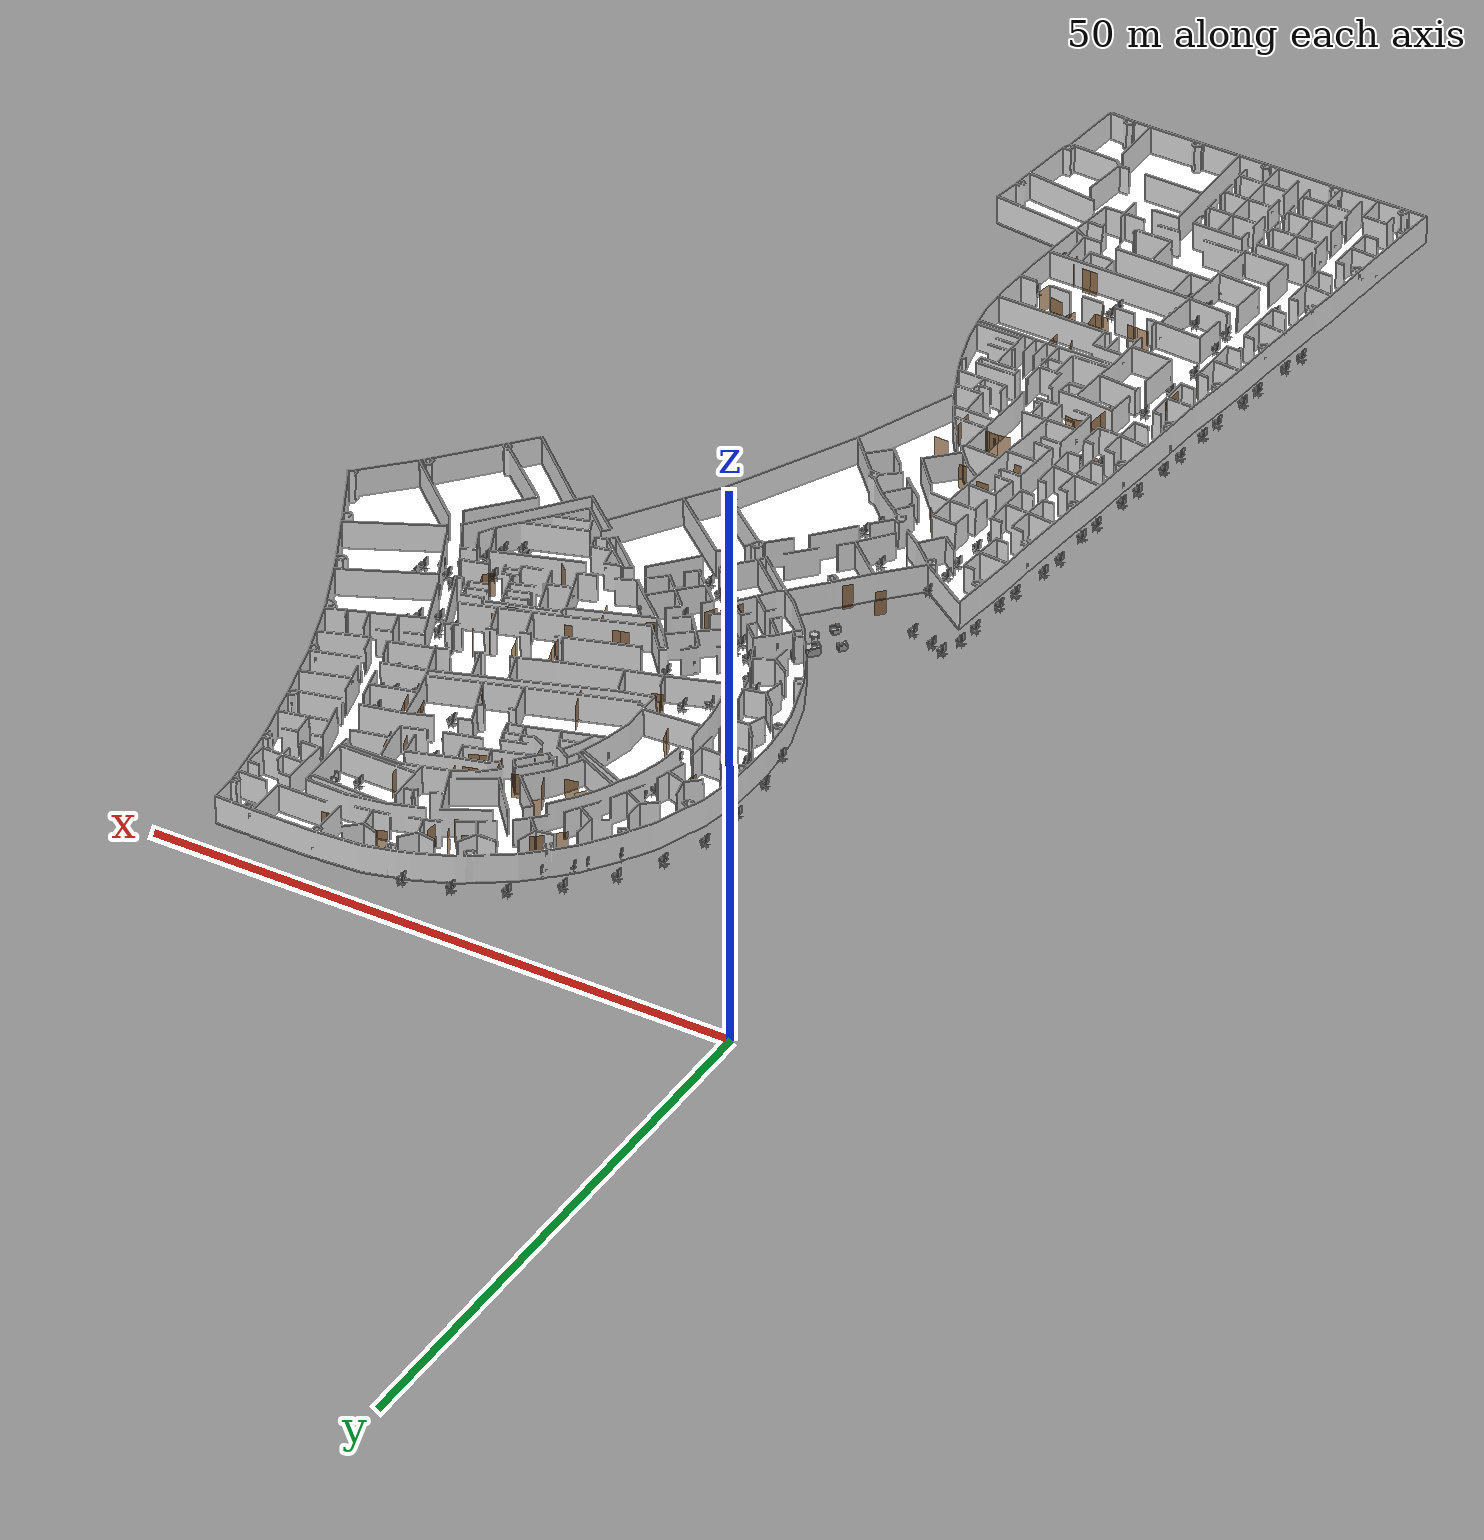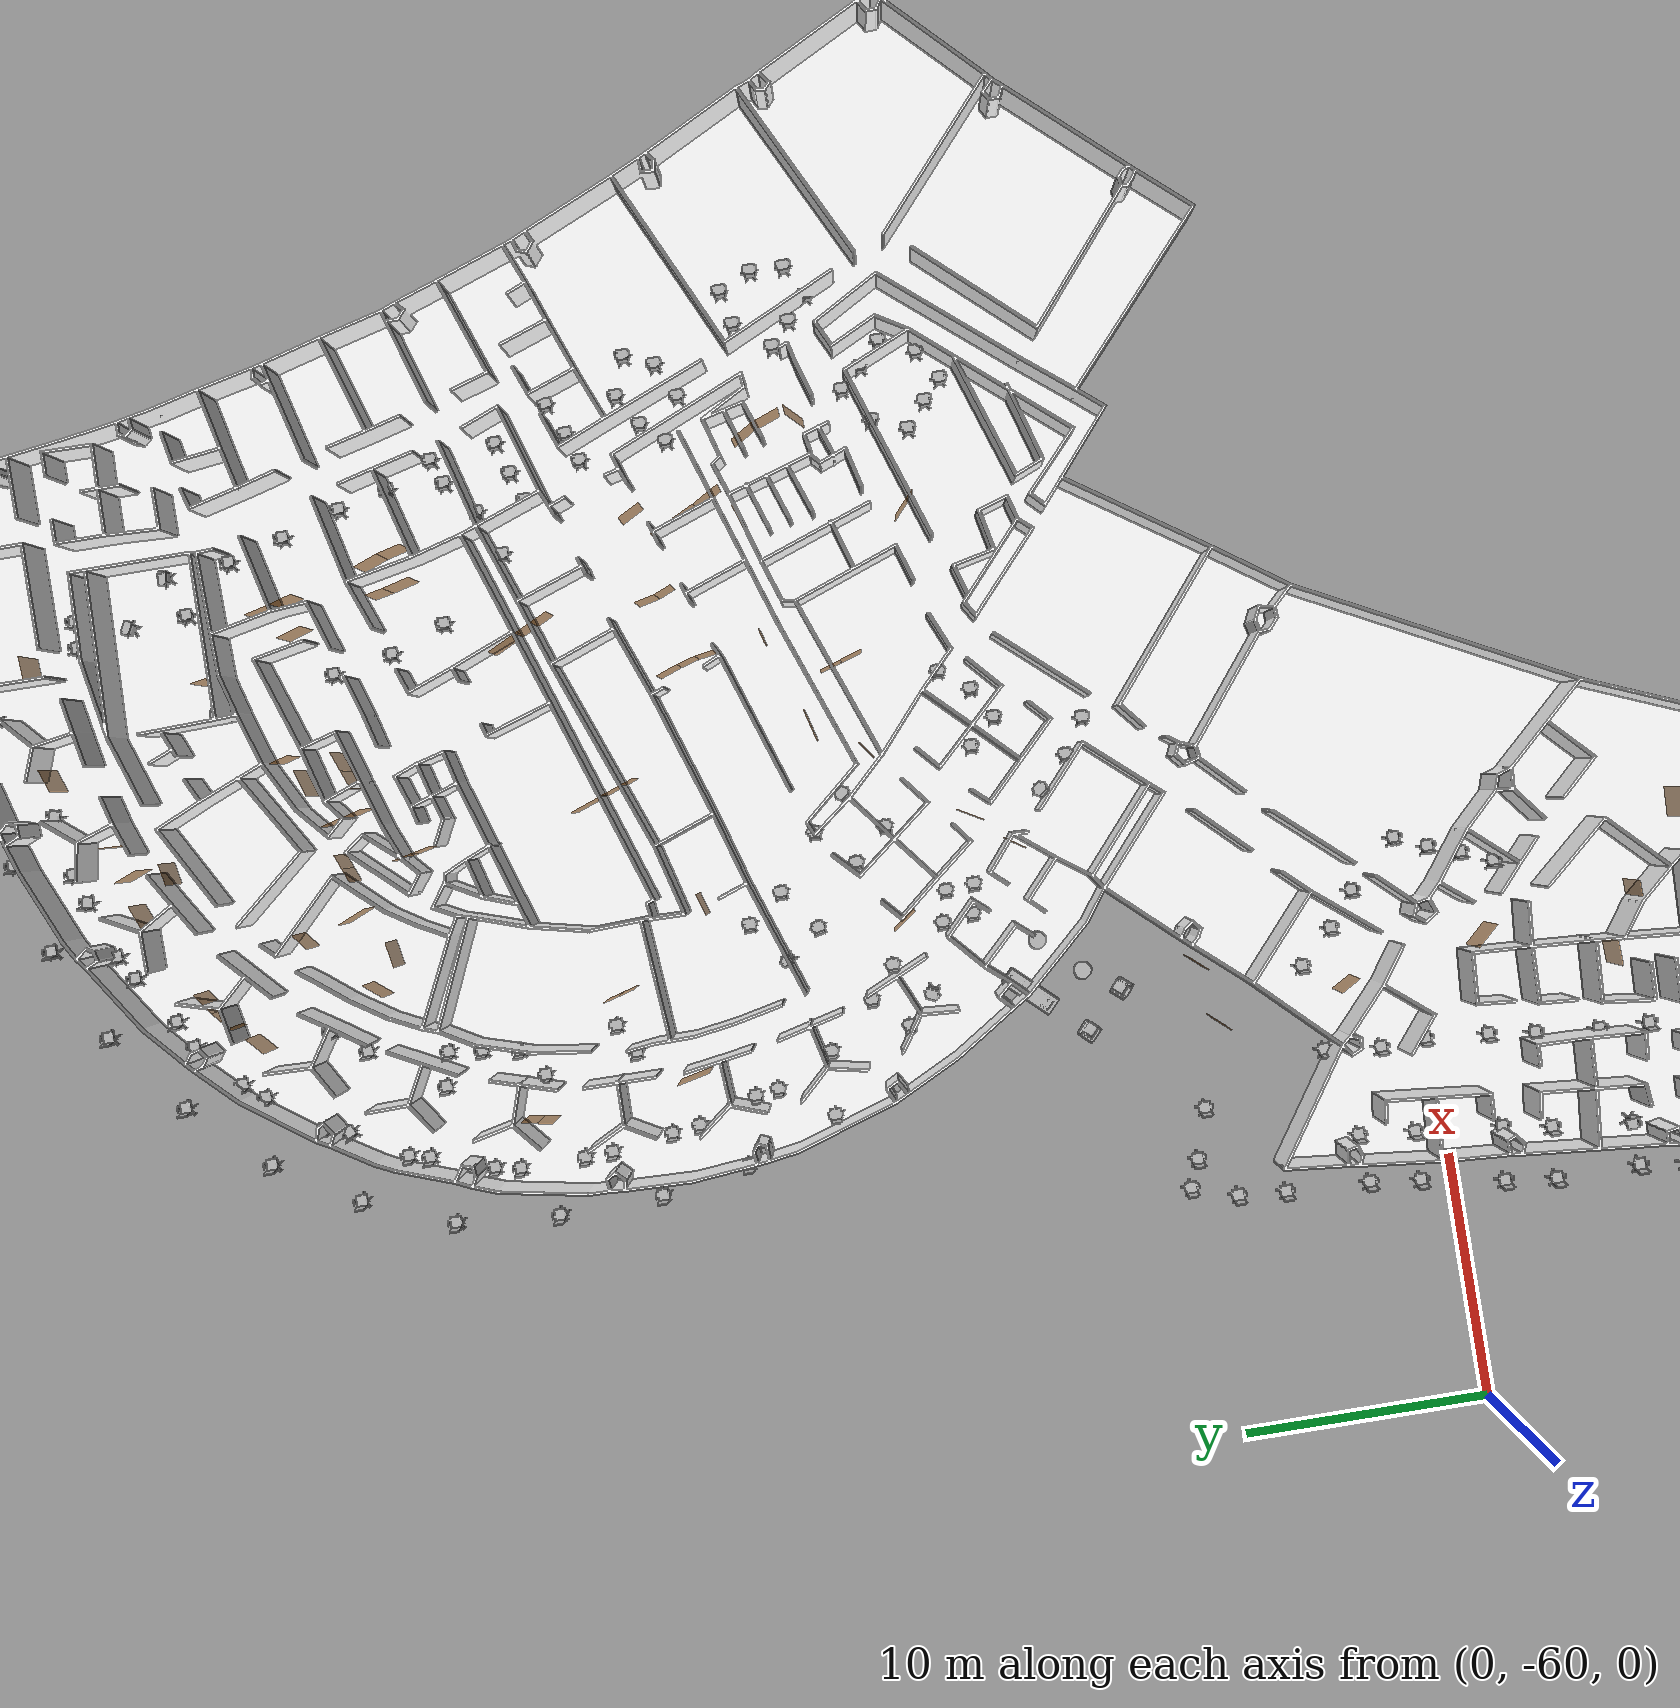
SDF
<sdf version="1.7">
 <world name="world">
  <scene><ambient>0.8 0.8 0.8 1.0</ambient><background>0 0 0</background><grid>false</grid></scene>
  <include><uri>model://sun</uri></include>
  <include>
   <name>OpenRobotics/OfficeChairBlue</name>
   <uri>model://OfficeChairBlue</uri>
   <pose>25.026887193577952 -89.94243627777595 0.0 0 0 1.5708</pose>
   <static>True</static>
  </include>
  <include>
   <name>OpenRobotics/OfficeChairBlue_2</name>
   <uri>model://OfficeChairBlue</uri>
   <pose>26.47516021920883 -90.09647851929083 0.0 0 0 1.5708</pose>
   <static>True</static>
  </include>
  <include>
   <name>OpenRobotics/OfficeChairBlue_3</name>
   <uri>model://OfficeChairBlue</uri>
   <pose>27.569027678309006 -93.99444697364449 0.0 0 0 1.5708</pose>
   <static>True</static>
  </include>
  <include>
   <name>OpenRobotics/OfficeChairBlue_4</name>
   <uri>model://OfficeChairBlue</uri>
   <pose>29.063523231944025 -94.2255596136652 0.0 0 0 1.5708</pose>
   <static>True</static>
  </include>
  <include>
   <name>OpenRobotics/OfficeChairBlue_5</name>
   <uri>model://OfficeChairBlue</uri>
   <pose>21.02198602518487 -94.29513979441344 0.0 0 0 1.5708</pose>
   <static>True</static>
  </include>
  <include>
   <name>OpenRobotics/OfficeChairBlue_6</name>
   <uri>model://OfficeChairBlue</uri>
   <pose>20.958614840735695 -95.39413213934776 0.0 0 0 1.5708</pose>
   <static>True</static>
  </include>
  <include>
   <name>OpenRobotics/OfficeChairBlue_7</name>
   <uri>model://OfficeChairBlue</uri>
   <pose>27.95408400434778 -98.73338948228245 0.0 0 0 1.5708</pose>
   <static>True</static>
  </include>
  <include>
   <name>OpenRobotics/OfficeChairBlue_8</name>
   <uri>model://OfficeChairBlue</uri>
   <pose>27.95408400434778 -99.76891208727079 0.0 0 0 1.5708</pose>
   <static>True</static>
  </include>
  <include>
   <name>OpenRobotics/OfficeChairBlue_9</name>
   <uri>model://OfficeChairBlue</uri>
   <pose>16.91251747467581 -101.03229500088511 0.0 0 0 1.5708</pose>
   <static>True</static>
  </include>
  <include>
   <name>OpenRobotics/OfficeChairBlue_10</name>
   <uri>model://OfficeChairBlue</uri>
   <pose>14.84610437304923 -101.055751209126 0.0 0 0 1.5708</pose>
   <static>True</static>
  </include>
  <include>
   <name>OpenRobotics/OfficeChairBlue_11</name>
   <uri>model://OfficeChairBlue</uri>
   <pose>14.869560581290138 -98.82494753881946 0.0 0 0 1.5708</pose>
   <static>True</static>
  </include>
  <include>
   <name>OpenRobotics/OfficeChairBlue_12</name>
   <uri>model://OfficeChairBlue</uri>
   <pose>16.72467069775492 -98.84840374706036 0.0 0 0 1.5708</pose>
   <static>True</static>
  </include>
  <include>
   <name>OpenRobotics/OfficeChairBlue_13</name>
   <uri>model://OfficeChairBlue</uri>
   <pose>16.74822546149264 -96.61760007675379 0.0 0 0 1.5708</pose>
   <static>True</static>
  </include>
  <include>
   <name>OpenRobotics/OfficeChairBlue_14</name>
   <uri>model://OfficeChairBlue</uri>
   <pose>14.728626220851066 -96.54713289653425 0.0 0 0 1.5708</pose>
   <static>True</static>
  </include>
  <include>
   <name>OpenRobotics/OfficeChairBlue_15</name>
   <uri>model://OfficeChairBlue</uri>
   <pose>16.58383489281266 -94.36324164270951 0.0 0 0 1.5708</pose>
   <static>True</static>
  </include>
  <include>
   <name>OpenRobotics/OfficeChairBlue_16</name>
   <uri>model://OfficeChairBlue</uri>
   <pose>14.893016789531046 -94.33978543446861 0.0 0 0 1.5708</pose>
   <static>True</static>
  </include>
  <include>
   <name>OpenRobotics/OfficeChairBlue_17</name>
   <uri>model://OfficeChairBlue</uri>
   <pose>11.652413498903698 -94.31623067073089 0.0 0 0 1.5708</pose>
   <static>True</static>
  </include>
  <include>
   <name>OpenRobotics/OfficeChairBlue_18</name>
   <uri>model://OfficeChairBlue</uri>
   <pose>11.957738428022749 -96.54713289653425 0.0 0 0 1.5708</pose>
   <static>True</static>
  </include>
  <include>
   <name>OpenRobotics/OfficeChairBlue_19</name>
   <uri>model://OfficeChairBlue</uri>
   <pose>9.86777056265845 -94.43370882292905 0.0 0 0 1.5708</pose>
   <static>True</static>
  </include>
  <include>
   <name>OpenRobotics/OfficeChairBlue_20</name>
   <uri>model://OfficeChairBlue</uri>
   <pose>9.891226770899358 -96.42965474433609 0.0 0 0 1.5708</pose>
   <static>True</static>
  </include>
  <include>
   <name>OpenRobotics/OfficeChairBlue_21</name>
   <uri>model://OfficeChairBlue</uri>
   <pose>9.985150159359803 -98.70746938662128 0.0 0 0 1.5708</pose>
   <static>True</static>
  </include>
  <include>
   <name>OpenRobotics/OfficeChairBlue_22</name>
   <uri>model://OfficeChairBlue</uri>
   <pose>9.961693951118894 -100.86790443220512 0.0 0 0 1.5708</pose>
   <static>True</static>
  </include>
  <include>
   <name>OpenRobotics/OfficeChairBlue_23</name>
   <uri>model://OfficeChairBlue</uri>
   <pose>7.00286082587288 -100.96182782066556 0.0 0 0 1.5708</pose>
   <static>True</static>
  </include>
  <include>
   <name>OpenRobotics/OfficeChairBlue_24</name>
   <uri>model://OfficeChairBlue</uri>
   <pose>11.957738428022749 -98.7544803585999 0.0 0 0 1.5708</pose>
   <static>True</static>
  </include>
  <include>
   <name>OpenRobotics/OfficeChairBlue_25</name>
   <uri>model://OfficeChairBlue</uri>
   <pose>11.887271247803213 -100.77398104374467 0.0 0 0 1.5708</pose>
   <static>True</static>
  </include>
  <include>
   <name>OpenRobotics/OfficeChairBlue_26</name>
   <uri>model://OfficeChairBlue</uri>
   <pose>11.917232118833617 -87.58508734956467 0.0 0 0 1.5708</pose>
   <static>True</static>
  </include>
  <include>
   <name>OpenRobotics/OfficeChairBlue_27</name>
   <uri>model://OfficeChairBlue</uri>
   <pose>12.299824557452132 -84.11169597547084 0.0 0 0 1.5708</pose>
   <static>True</static>
  </include>
  <include>
   <name>OpenRobotics/OfficeChairBlue_28</name>
   <uri>model://OfficeChairBlue</uri>
   <pose>11.563910662767833 -90.7348224721327 0.0 0 0 1.5708</pose>
   <static>True</static>
  </include>
  <include>
   <name>OpenRobotics/OfficeChairBlue_29</name>
   <uri>model://OfficeChairBlue</uri>
   <pose>5.4331674281714175 -96.78258197841464 0.0 0 0 1.5708</pose>
   <static>True</static>
  </include>
  <include>
   <name>OpenRobotics/OfficeChairBlue_30</name>
   <uri>model://OfficeChairBlue</uri>
   <pose>5.781068331912622 -94.82911347613295 0.0 0 0 1.5708</pose>
   <static>True</static>
  </include>
  <include>
   <name>OpenRobotics/OfficeChairBlue_31</name>
   <uri>model://OfficeChairBlue</uri>
   <pose>6.209193410057606 -91.13623901064203 0.0 0 0 1.5708</pose>
   <static>True</static>
  </include>
  <include>
   <name>OpenRobotics/OfficeChairBlue_32</name>
   <uri>model://OfficeChairBlue</uri>
   <pose>6.396547409494441 -89.15596341322785 0.0 0 0 1.5708</pose>
   <static>True</static>
  </include>
  <include>
   <name>OpenRobotics/OfficeChairBlue_33</name>
   <uri>model://OfficeChairBlue</uri>
   <pose>6.797963948003768 -85.78418275634567 0.0 0 0 1.5708</pose>
   <static>True</static>
  </include>
  <include>
   <name>OpenRobotics/OfficeChairBlue_34</name>
   <uri>model://OfficeChairBlue</uri>
   <pose>6.958510852308137 -83.75039152416339 0.0 0 0 1.5708</pose>
   <static>True</static>
  </include>
  <include>
   <name>OpenRobotics/OfficeChairBlue_35</name>
   <uri>model://OfficeChairBlue</uri>
   <pose>7.145864851744972 -80.53915777158558 0.0 0 0 1.5708</pose>
   <static>True</static>
  </include>
  <include>
   <name>OpenRobotics/OfficeChairBlue_36</name>
   <uri>model://OfficeChairBlue</uri>
   <pose>7.359927390817464 -78.31811109546327 0.0 0 0 1.5708</pose>
   <static>True</static>
  </include>
  <include>
   <name>OpenRobotics/OfficeChairBlue_37</name>
   <uri>model://OfficeChairBlue</uri>
   <pose>7.734536834194324 -74.8660077086805 0.0 0 0 1.5708</pose>
   <static>True</static>
  </include>
  <include>
   <name>OpenRobotics/OfficeChairBlue_38</name>
   <uri>model://OfficeChairBlue</uri>
   <pose>8.028922103167405 -72.9125392063988 0.0 0 0 1.5708</pose>
   <static>True</static>
  </include>
  <include>
   <name>OpenRobotics/OfficeChairBlue_39</name>
   <uri>model://OfficeChairBlue</uri>
   <pose>8.29650027700802 -69.4069201848479 0.0 0 0 1.5708</pose>
   <static>True</static>
  </include>
  <include>
   <name>OpenRobotics/OfficeChairBlue_40</name>
   <uri>model://OfficeChairBlue</uri>
   <pose>8.510562816080512 -67.48016022220186 0.0 0 0 1.5708</pose>
   <static>True</static>
  </include>
  <include>
   <name>OpenRobotics/OfficeChairBlue_41</name>
   <uri>model://OfficeChairBlue</uri>
   <pose>10.113567971703935 -67.44379324387877 0.0 0 0 -1.5708</pose>
   <static>True</static>
  </include>
  <include>
   <name>OpenRobotics/OfficeChairBlue_42</name>
   <uri>model://OfficeChairBlue</uri>
   <pose>14.157004339349937 -68.76463401213363 0.0 0 0 1.5708</pose>
   <static>True</static>
  </include>
  <include>
   <name>OpenRobotics/OfficeChairBlue_43</name>
   <uri>model://OfficeChairBlue</uri>
   <pose>14.237327069250528 -66.73094133544815 0.0 0 0 1.5708</pose>
   <static>True</static>
  </include>
  <include>
   <name>OpenRobotics/OfficeChairBlue_44</name>
   <uri>model://OfficeChairBlue</uri>
   <pose>14.504905243091143 -64.13518666045215 0.0 0 0 1.5708</pose>
   <static>True</static>
  </include>
  <include>
   <name>OpenRobotics/OfficeChairBlue_45</name>
   <uri>model://OfficeChairBlue</uri>
   <pose>14.7457748772961 -62.23523379293858 0.0 0 0 1.5708</pose>
   <static>True</static>
  </include>
  <include>
   <name>OpenRobotics/OfficeChairBlue_46</name>
   <uri>model://OfficeChairBlue</uri>
   <pose>14.986545956004248 -59.66618765757825 0.0 0 0 1.5708</pose>
   <static>True</static>
  </include>
  <include>
   <name>OpenRobotics/OfficeChairBlue_47</name>
   <uri>model://OfficeChairBlue</uri>
   <pose>14.906321781600468 -57.84655751996525 0.0 0 0 1.5708</pose>
   <static>True</static>
  </include>
  <include>
   <name>OpenRobotics/OfficeChairBlue_48</name>
   <uri>model://OfficeChairBlue</uri>
   <pose>15.173899955441081 -55.545188113942345 0.0 0 0 1.5708</pose>
   <static>True</static>
  </include>
  <include>
   <name>OpenRobotics/OfficeChairBlue_49</name>
   <uri>model://OfficeChairBlue</uri>
   <pose>9.313395893099166 -58.59577640671898 0.0 0 0 1.5708</pose>
   <static>True</static>
  </include>
  <include>
   <name>OpenRobotics/OfficeChairBlue_50</name>
   <uri>model://OfficeChairBlue</uri>
   <pose>9.554364082800936 -56.52354853078057 0.0 0 0 1.5708</pose>
   <static>True</static>
  </include>
  <include>
   <name>OpenRobotics/OfficeChairBlue_51</name>
   <uri>model://OfficeChairBlue</uri>
   <pose>11.528726350406473 -56.383796836303226 0.0 0 0 1.5708</pose>
   <static>True</static>
  </include>
  <include>
   <name>OpenRobotics/OfficeChairBlue_52</name>
   <uri>model://OfficeChairBlue</uri>
   <pose>11.30165448575499 -58.672649694231204 0.0 0 0 1.5708</pose>
   <static>True</static>
  </include>
  <include>
   <name>OpenRobotics/OfficeChairBlue_53</name>
   <uri>model://OfficeChairBlue</uri>
   <pose>9.711658655710556 -53.11648500604023 0.0 0 0 1.5708</pose>
   <static>True</static>
  </include>
  <include>
   <name>OpenRobotics/OfficeChairBlue_54</name>
   <uri>model://OfficeChairBlue</uri>
   <pose>9.868953228620176 -51.15956706137016 0.0 0 0 1.5708</pose>
   <static>True</static>
  </include>
  <include>
   <name>OpenRobotics/OfficeChairBlue_55</name>
   <uri>model://OfficeChairBlue</uri>
   <pose>13.595040896536242 -50.38038730358603 0.0 0 0 1.5708</pose>
   <static>True</static>
  </include>
  <include>
   <name>OpenRobotics/OfficeChairBlue_56</name>
   <uri>model://OfficeChairBlue</uri>
   <pose>10.464129873859024 -49.30997605272676 0.0 0 0 1.5708</pose>
   <static>True</static>
  </include>
  <include>
   <name>OpenRobotics/OfficeChairBlue_57</name>
   <uri>model://OfficeChairBlue</uri>
   <pose>11.588056759486415 -49.76490822600421 0.0 0 0 1.5708</pose>
   <static>True</static>
  </include>
  <include>
   <name>OpenRobotics/OfficeChairBlue_58</name>
   <uri>model://OfficeChairBlue</uri>
   <pose>8.506029263227227 -64.07161836500936 0.0 0 0 1.5708</pose>
   <static>True</static>
  </include>
  <include>
   <name>OpenRobotics/OfficeChairBlue_59</name>
   <uri>model://OfficeChairBlue</uri>
   <pose>8.750644006310987 -61.97494872586194 0.0 0 0 1.5708</pose>
   <static>True</static>
  </include>
  <include>
   <name>OpenRobotics/OfficeChairBlue_60</name>
   <uri>model://OfficeChairBlue</uri>
   <pose>10.93473237112935 -62.20211914601024 0.0 0 0 1.5708</pose>
   <static>True</static>
  </include>
  <include>
   <name>OpenRobotics/OfficeChairBlue_61</name>
   <uri>model://OfficeChairBlue</uri>
   <pose>10.602698902374643 -64.19392573655124 0.0 0 0 1.5897</pose>
   <static>True</static>
  </include>
  <include>
   <name>OpenRobotics/OfficeChairBlue_62</name>
   <uri>model://OfficeChairBlue</uri>
   <pose>13.407982563589837 -75.48651311659965 0.0 0 0 1.6053</pose>
   <static>True</static>
  </include>
  <include>
   <name>OpenRobotics/OfficeChairBlue_63</name>
   <uri>model://OfficeChairBlue</uri>
   <pose>13.378810136533916 -76.52242994357525 0.0 0 0 1.5708</pose>
   <static>True</static>
  </include>
  <include>
   <name>OpenRobotics/OfficeChairBlue_64</name>
   <uri>model://OfficeChairBlue</uri>
   <pose>11.992725629390492 -75.55944418423945 0.0 0 0 1.5708</pose>
   <static>True</static>
  </include>
  <include>
   <name>OpenRobotics/OfficeChairBlue_65</name>
   <uri>model://OfficeChairBlue</uri>
   <pose>11.9488684333098 -76.71214927493553 0.0 0 0 1.5708</pose>
   <static>True</static>
  </include>
  <include>
   <name>OpenRobotics/OfficeChairBlue_66</name>
   <uri>model://OfficeChairBlue</uri>
   <pose>11.96345464683776 -76.72673548846349 0.0 0 0 1.5708</pose>
   <static>True</static>
  </include>
  <include>
   <name>OpenRobotics/OfficeChairBlue_67</name>
   <uri>model://OfficeChairBlue</uri>
   <pose>23.239484703422008 -59.68067531560939 0.0 0 0 1.5708</pose>
   <static>True</static>
  </include>
  <include>
   <name>OpenRobotics/OfficeChairBlue_68</name>
   <uri>model://OfficeChairBlue</uri>
   <pose>22.679689481538144 -60.98692987033628 0.0 0 0 1.5708</pose>
   <static>True</static>
  </include>
  <include>
   <name>OpenRobotics/OfficeChairBlue_69</name>
   <uri>model://OfficeChairBlue</uri>
   <pose>22.231853304031052 -62.274557436165985 0.0 0 0 1.5708</pose>
   <static>True</static>
  </include>
  <include>
   <name>OpenRobotics/OfficeChairBlue_70</name>
   <uri>model://OfficeChairBlue</uri>
   <pose>21.69068507104438 -63.54355801309849 0.0 0 0 1.5708</pose>
   <static>True</static>
  </include>
  <include>
   <name>OpenRobotics/OfficeChairBlue_71</name>
   <uri>model://OfficeChairBlue</uri>
   <pose>18.676463756590845 -55.192457990857434 0.0 0 0 1.5708</pose>
   <static>True</static>
  </include>
  <include>
   <name>OpenRobotics/OfficeChairBlue_72</name>
   <uri>model://OfficeChairBlue</uri>
   <pose>20.02253473202919 -56.58721538172019 0.0 0 0 1.5708</pose>
   <static>True</static>
  </include>
  <include>
   <name>OpenRobotics/OfficeChairBlue_73</name>
   <uri>model://OfficeChairBlue</uri>
   <pose>21.401030465918204 -57.65752807708264 0.0 0 0 1.5708</pose>
   <static>True</static>
  </include>
  <include>
   <name>OpenRobotics/KitchenCountertop</name>
   <uri>model://KitchenCountertop</uri>
   <pose>19.355018352131406 -44.11886092472203 0.0 0 0 2.3925</pose>
   <static>True</static>
  </include>
  <include>
   <name>OpenRobotics/OfficeChairBlue_74</name>
   <uri>model://OfficeChairBlue</uri>
   <pose>42.84394701798089 -42.83330302432535 0.0 0 0 1.5708</pose>
   <static>True</static>
  </include>
  <include>
   <name>OpenRobotics/OfficeChairBlue_75</name>
   <uri>model://OfficeChairBlue</uri>
   <pose>43.85552063724427 -43.66097208654026 0.0 0 0 1.5708</pose>
   <static>True</static>
  </include>
  <include>
   <name>OpenRobotics/OfficeChairBlue_76</name>
   <uri>model://OfficeChairBlue</uri>
   <pose>44.66466126605879 -44.41492163714089 0.0 0 0 1.5708</pose>
   <static>True</static>
  </include>
  <include>
   <name>OpenRobotics/OfficeChairBlue_77</name>
   <uri>model://OfficeChairBlue</uri>
   <pose>45.896900642680976 -43.62411233073312 0.0 0 0 1.5708</pose>
   <static>True</static>
  </include>
  <include>
   <name>OpenRobotics/OfficeChairBlue_78</name>
   <uri>model://OfficeChairBlue</uri>
   <pose>46.55899647025417 -42.18963707465572 0.0 0 0 1.5708</pose>
   <static>True</static>
  </include>
  <include>
   <name>OpenRobotics/OfficeChairBlue_79</name>
   <uri>model://OfficeChairBlue</uri>
   <pose>45.63947368501184 -41.306875489723716 0.0 0 0 1.5708</pose>
   <static>True</static>
  </include>
  <include>
   <name>OpenRobotics/OfficeChairBlue_80</name>
   <uri>model://OfficeChairBlue</uri>
   <pose>44.830234500700506 -40.405684026888146 0.0 0 0 1.5708</pose>
   <static>True</static>
  </include>
  <include>
   <name>OpenRobotics/OfficeChairBlue_81</name>
   <uri>model://OfficeChairBlue</uri>
   <pose>43.41409056702987 -41.39882776824795 0.0 0 0 1.4973</pose>
   <static>True</static>
  </include>
  <include>
   <name>OpenRobotics/OfficeChairBlue_82</name>
   <uri>model://OfficeChairBlue</uri>
   <pose>48.85790198885682 -39.55968364226647 0.0 0 0 1.5708</pose>
   <static>True</static>
  </include>
  <include>
   <name>OpenRobotics/OfficeChairBlue_83</name>
   <uri>model://OfficeChairBlue</uri>
   <pose>47.93837920361449 -38.7136832576448 0.0 0 0 1.5708</pose>
   <static>True</static>
  </include>
  <include>
   <name>OpenRobotics/OfficeChairBlue_84</name>
   <uri>model://OfficeChairBlue</uri>
   <pose>47.01875786287534 -37.904444073333465 0.0 0 0 1.5708</pose>
   <static>True</static>
  </include>
  <include>
   <name>OpenRobotics/OfficeChairBlue_85</name>
   <uri>model://OfficeChairBlue</uri>
   <pose>50.145332443692894 -38.86082661438294 0.0 0 0 1.5708</pose>
   <static>True</static>
  </include>
  <include>
   <name>OpenRobotics/OfficeChairBlue_86</name>
   <uri>model://OfficeChairBlue</uri>
   <pose>50.182093644003224 -37.48144388102263 0.0 0 0 1.5708</pose>
   <static>True</static>
  </include>
  <include>
   <name>OpenRobotics/OfficeChairBlue_87</name>
   <uri>model://OfficeChairBlue</uri>
   <pose>49.55675901674036 -36.13892090346946 0.0 0 0 1.5708</pose>
   <static>True</static>
  </include>
  <include>
   <name>OpenRobotics/OfficeChairBlue_88</name>
   <uri>model://OfficeChairBlue</uri>
   <pose>48.15904496097328 -36.451538939352496 0.0 0 0 1.5708</pose>
   <static>True</static>
  </include>
  <include>
   <name>OpenRobotics/OfficeChairBlue_89</name>
   <uri>model://OfficeChairBlue</uri>
   <pose>43.909627604993254 -33.019836540409514 0.0 0 0 1.5708</pose>
   <static>True</static>
  </include>
  <include>
   <name>OpenRobotics/OfficeChairBlue_90</name>
   <uri>model://OfficeChairBlue</uri>
   <pose>44.74557532894025 -32.07744887990713 0.0 0 0 1.5708</pose>
   <static>True</static>
  </include>
  <include>
   <name>OpenRobotics/OfficeChairBlue_91</name>
   <uri>model://OfficeChairBlue</uri>
   <pose>46.02226323462398 -31.287132350983416 0.0 0 0 1.5833</pose>
   <static>True</static>
  </include>
  <include>
   <name>OpenRobotics/OfficeChairBlue_92</name>
   <uri>model://OfficeChairBlue</uri>
   <pose>47.587817301459395 -31.834312469275535 0.0 0 0 1.5708</pose>
   <static>True</static>
  </include>
  <include>
   <name>OpenRobotics/OfficeChairBlue_93</name>
   <uri>model://OfficeChairBlue</uri>
   <pose>47.0558147296761 -33.050191633427154 0.0 0 0 1.5708</pose>
   <static>True</static>
  </include>
  <include>
   <name>OpenRobotics/OfficeChairBlue_94</name>
   <uri>model://OfficeChairBlue</uri>
   <pose>45.627154247910525 -33.76462042980676 0.0 0 0 1.5708</pose>
   <static>True</static>
  </include>
  <include>
   <name>OpenRobotics/OfficeChairBlue_95</name>
   <uri>model://OfficeChairBlue</uri>
   <pose>43.66639263886485 -29.432810678493116 0.0 0 0 1.5708</pose>
   <static>True</static>
  </include>
  <include>
   <name>OpenRobotics/OfficeChairBlue_96</name>
   <uri>model://OfficeChairBlue</uri>
   <pose>44.83673916349 -29.02242558977403 0.0 0 0 1.5708</pose>
   <static>True</static>
  </include>
  <include>
   <name>OpenRobotics/OfficeChairBlue_97</name>
   <uri>model://OfficeChairBlue</uri>
   <pose>46.12870317117936 -28.414436729949816 0.0 0 0 1.5708</pose>
   <static>True</static>
  </include>
  <include>
   <name>OpenRobotics/OfficeChairBlue_98</name>
   <uri>model://OfficeChairBlue</uri>
   <pose>42.43523737270758 -26.9705001461786 0.0 0 0 1.5708</pose>
   <static>True</static>
  </include>
  <include>
   <name>OpenRobotics/OfficeChairBlue_99</name>
   <uri>model://OfficeChairBlue</uri>
   <pose>43.620761443841566 -26.54483895545388 0.0 0 0 1.5708</pose>
   <static>True</static>
  </include>
  <include>
   <name>OpenRobotics/OfficeChairBlue_100</name>
   <uri>model://OfficeChairBlue</uri>
   <pose>44.8975479050221 -26.134453866734795 0.0 0 0 1.5708</pose>
   <static>True</static>
  </include>
  <include>
   <name>OpenRobotics/OfficeChairBlue_101</name>
   <uri>model://OfficeChairBlue</uri>
   <pose>43.637023100815306 -23.82234191155954 0.0 0 0 1.5708</pose>
   <static>True</static>
  </include>
  <include>
   <name>OpenRobotics/OfficeChairBlue_102</name>
   <uri>model://OfficeChairBlue</uri>
   <pose>44.648103942594624 -23.423586371464097 0.0 0 0 1.5708</pose>
   <static>True</static>
  </include>
  <include>
   <name>OpenRobotics/OfficeChairBlue_103</name>
   <uri>model://OfficeChairBlue</uri>
   <pose>42.25566925751878 -24.961544899192564 0.0 0 0 1.5708</pose>
   <static>True</static>
  </include>
  <include>
   <name>OpenRobotics/OfficeChairBlue_104</name>
   <uri>model://OfficeChairBlue</uri>
   <pose>40.40440280542961 -25.716282893767676 0.0 0 0 1.5708</pose>
   <static>True</static>
  </include>
  <include>
   <name>OpenRobotics/OfficeChairBlue_105</name>
   <uri>model://OfficeChairBlue</uri>
   <pose>27.442975197888327 -45.781787822406265 0.0 0 0 2.2489</pose>
   <static>True</static>
  </include>
  <include>
   <name>OpenRobotics/OfficeChairBlue_106</name>
   <uri>model://OfficeChairBlue</uri>
   <pose>28.71197577482083 -47.05078839933877 0.0 0 0 1.5708</pose>
   <static>True</static>
  </include>
  <include>
   <name>OpenRobotics/OfficeChairBlue_107</name>
   <uri>model://OfficeChairBlue</uri>
   <pose>30.100918391371764 -47.94241997898372 0.0 0 0 1.5708</pose>
   <static>True</static>
  </include>
  <include>
   <name>OpenRobotics/OfficeChairBlue_108</name>
   <uri>model://OfficeChairBlue</uri>
   <pose>29.65505332380088 -43.31257840531501 0.0 0 0 1.5708</pose>
   <static>True</static>
  </include>
  <include>
   <name>OpenRobotics/OfficeChairBlue_109</name>
   <uri>model://OfficeChairBlue</uri>
   <pose>30.683874155006105 -44.40999386230036 0.0 0 0 1.5708</pose>
   <static>True</static>
  </include>
  <include>
   <name>OpenRobotics/OfficeChairBlue_110</name>
   <uri>model://OfficeChairBlue</uri>
   <pose>31.970023388383648 -43.65555153421568 0.0 0 0 1.5708</pose>
   <static>True</static>
  </include>
  <include>
   <name>OpenRobotics/OfficeChairBlue_111</name>
   <uri>model://OfficeChairBlue</uri>
   <pose>32.87880362447363 -42.45514558306331 0.0 0 0 1.5708</pose>
   <static>True</static>
  </include>
  <include>
   <name>OpenRobotics/OfficeChairBlue_112</name>
   <uri>model://OfficeChairBlue</uri>
   <pose>24.02043846014872 -41.37034522966971 0.0 0 0 1.5708</pose>
   <static>True</static>
  </include>
  <include>
   <name>OpenRobotics/OfficeChairBlue_113</name>
   <uri>model://OfficeChairBlue</uri>
   <pose>22.910407899571616 -42.305144116917674 0.0 0 0 1.5708</pose>
   <static>True</static>
  </include>
  <include>
   <name>OpenRobotics/OfficeChairBlue_114</name>
   <uri>model://OfficeChairBlue</uri>
   <pose>22.74976243977044 -41.04905431006735 0.0 0 0 1.5708</pose>
   <static>True</static>
  </include>
  <include>
   <name>OpenRobotics/OfficeChairBlue_115</name>
   <uri>model://OfficeChairBlue</uri>
   <pose>24.108054296813293 -42.53881919985546 0.0 0 0 1.5708</pose>
   <static>True</static>
  </include>
  <include>
   <name>OpenRobotics/OfficeChairBlue_116</name>
   <uri>model://OfficeChairBlue</uri>
   <pose>25.001755541891264 -34.734307962925655 0.0 0 0 1.5708</pose>
   <static>True</static>
  </include>
  <include>
   <name>OpenRobotics/OfficeChairBlue_117</name>
   <uri>model://OfficeChairBlue</uri>
   <pose>23.899707976555813 -33.27371550019346 0.0 0 0 1.5708</pose>
   <static>True</static>
  </include>
  <include>
   <name>OpenRobotics/OfficeChairBlue_118</name>
   <uri>model://OfficeChairBlue</uri>
   <pose>22.20021698955487 -34.52182231180213 0.0 0 0 2.63</pose>
   <static>True</static>
  </include>
  <include>
   <name>OpenRobotics/OfficeChairBlue_119</name>
   <uri>model://OfficeChairBlue</uri>
   <pose>23.34208097560178 -35.99562121110694 0.0 0 0 1.7862</pose>
   <static>True</static>
  </include>
  <include>
   <name>OpenRobotics/OfficeChairBlue_120</name>
   <uri>model://OfficeChairBlue</uri>
   <pose>25.71874678118794 -37.96071926201228 0.0 0 0 1.5708</pose>
   <static>True</static>
  </include>
  <include>
   <name>OpenRobotics/OfficeChairBlue_121</name>
   <uri>model://OfficeChairBlue</uri>
   <pose>26.98015858486603 -39.34158032782475 0.0 0 0 1.5708</pose>
   <static>True</static>
  </include>
  <include>
   <name>OpenRobotics/OfficeChairBlue_122</name>
   <uri>model://OfficeChairBlue</uri>
   <pose>28.546895317663182 -37.801453579166456 0.0 0 0 2.1815</pose>
   <static>True</static>
  </include>
  <include>
   <name>OpenRobotics/OfficeChairBlue_123</name>
   <uri>model://OfficeChairBlue</uri>
   <pose>27.179339243920133 -36.47361537063805 0.0 0 0 1.5708</pose>
   <static>True</static>
  </include>
  <include>
   <name>OpenRobotics/OfficeChairBlue_124</name>
   <uri>model://OfficeChairBlue</uri>
   <pose>21.36308659964615 -38.76453789399904 0.0 0 0 1.5708</pose>
   <static>True</static>
  </include>
  <include>
   <name>OpenRobotics/OfficeChairBlue_125</name>
   <uri>model://OfficeChairBlue</uri>
   <pose>19.836954731534945 -40.1453004043147 0.0 0 0 -1.9996</pose>
   <static>True</static>
  </include>
  <include>
   <name>OpenRobotics/OfficeChairBlue_126</name>
   <uri>model://OfficeChairBlue</uri>
   <pose>18.81956633795975 -39.06976426762128 0.0 0 0 1.5708</pose>
   <static>True</static>
  </include>
  <include>
   <name>OpenRobotics/OfficeChairBlue_127</name>
   <uri>model://OfficeChairBlue</uri>
   <pose>20.098619575566925 -37.703489415336776 0.0 0 0 1.5708</pose>
   <static>True</static>
  </include>
  <include>
   <name>OpenRobotics/OfficeChairBlue_128</name>
   <uri>model://OfficeChairBlue</uri>
   <pose>19.515269589945344 -27.90076548057328 0.0 0 0 1.5708</pose>
   <static>True</static>
  </include>
  <include>
   <name>OpenRobotics/OfficeChairBlue_129</name>
   <uri>model://OfficeChairBlue</uri>
   <pose>20.713605875664694 -27.27572651980084 0.0 0 0 1.5708</pose>
   <static>True</static>
  </include>
  <include>
   <name>OpenRobotics/OfficeChairBlue_130</name>
   <uri>model://OfficeChairBlue</uri>
   <pose>19.193880114846177 -24.112292183176148 0.0 0 0 1.5708</pose>
   <static>True</static>
  </include>
  <include>
   <name>OpenRobotics/OfficeChairBlue_131</name>
   <uri>model://OfficeChairBlue</uri>
   <pose>20.331013437046177 -23.207651277952206 0.0 0 0 1.5708</pose>
   <static>True</static>
  </include>
  <include>
   <name>OpenRobotics/OfficeChairBlue_132</name>
   <uri>model://OfficeChairBlue</uri>
   <pose>20.572671515225622 -21.717295055183225 0.0 0 0 1.5708</pose>
   <static>True</static>
  </include>
  <include>
   <name>OpenRobotics/OfficeChairBlue_133</name>
   <uri>model://OfficeChairBlue</uri>
   <pose>20.739033193841813 -20.348753426472076 0.0 0 0 1.5708</pose>
   <static>True</static>
  </include>
  <include>
   <name>OpenRobotics/OfficeChairBlue_134</name>
   <uri>model://OfficeChairBlue</uri>
   <pose>19.362114347901766 -20.042738608875354 0.0 0 0 1.5708</pose>
   <static>True</static>
  </include>
  <include>
   <name>OpenRobotics/OfficeChairBlue_135</name>
   <uri>model://OfficeChairBlue</uri>
   <pose>22.324791137523395 -15.7360605092484 0.0 0 0 1.5708</pose>
   <static>True</static>
  </include>
  <include>
   <name>OpenRobotics/OfficeChairBlue_136</name>
   <uri>model://OfficeChairBlue</uri>
   <pose>21.2775404284146 -17.105489137430848 0.0 0 0 1.5708</pose>
   <static>True</static>
  </include>
  <include>
   <name>OpenRobotics/OfficeChairBlue_137</name>
   <uri>model://OfficeChairBlue</uri>
   <pose>37.04651847359772 -4.176190621849798 0.0 0 0 1.5708</pose>
   <static>True</static>
  </include>
  <include>
   <name>OpenRobotics/OfficeChairBlue_138</name>
   <uri>model://OfficeChairBlue</uri>
   <pose>39.82568492815812 -4.256710462744009 0.0 0 0 1.5708</pose>
   <static>True</static>
  </include>
  <include>
   <name>OpenRobotics/OfficeChairBlue_139</name>
   <uri>model://OfficeChairBlue</uri>
   <pose>41.819462628635335 -14.668605923293448 0.0 0 0 1.5708</pose>
   <static>True</static>
  </include>
  <include>
   <name>OpenRobotics/OfficeChairBlue_140</name>
   <uri>model://OfficeChairBlue</uri>
   <pose>43.71251661137217 -21.495840853849945 0.0 0 0 1.5708</pose>
   <static>True</static>
  </include>
  <include>
   <name>OpenRobotics/OfficeChairBlue_141</name>
   <uri>model://OfficeChairBlue</uri>
   <pose>43.24940433185945 -19.42144475698171 0.0 0 0 1.5708</pose>
   <static>True</static>
  </include>
  <include>
   <name>OpenRobotics/OfficeChairBlue_142</name>
   <uri>model://OfficeChairBlue</uri>
   <pose>42.46391702227945 -16.984660098341124 0.0 0 0 1.5708</pose>
   <static>True</static>
  </include>
  <include>
   <name>OpenRobotics/OfficeChairBlue_143</name>
   <uri>model://OfficeChairBlue</uri>
   <pose>36.643722158133045 -18.172845167888987 0.0 0 0 1.5708</pose>
   <static>True</static>
  </include>
  <include>
   <name>OpenRobotics/OfficeChairBlue_144</name>
   <uri>model://OfficeChairBlue</uri>
   <pose>37.08672911629642 -20.629833703375734 0.0 0 0 1.5708</pose>
   <static>True</static>
  </include>
  <include>
   <name>OpenRobotics/OfficeChairBlue_145</name>
   <uri>model://OfficeChairBlue</uri>
   <pose>37.972940143616796 -22.92568400157725 0.0 0 0 1.5708</pose>
   <static>True</static>
  </include>
  <include>
   <name>OpenRobotics/OfficeChairBlue_146</name>
   <uri>model://OfficeChairBlue</uri>
   <pose>39.362474093148585 -8.042818428217691 0.0 0 0 1.5708</pose>
   <static>True</static>
  </include>
  <include>
   <name>OpenRobotics/OfficeChairBlue_147</name>
   <uri>model://OfficeChairBlue</uri>
   <pose>40.42983012360673 -8.103232947762551 0.0 0 0 1.5708</pose>
   <static>True</static>
  </include>
  <include>
   <name>OpenRobotics/OfficeChairBlue_148</name>
   <uri>model://OfficeChairBlue</uri>
   <pose>39.78537572996261 -10.177629044630786 0.0 0 0 2.6584</pose>
   <static>True</static>
  </include>
  <include>
   <name>OpenRobotics/OfficeChairBlue_149</name>
   <uri>model://OfficeChairBlue</uri>
   <pose>39.966717844094 -12.634617580117535 0.0 0 0 1.5708</pose>
   <static>True</static>
  </include>
  <include>
   <name>OpenRobotics/OfficeChairBlue_150</name>
   <uri>model://OfficeChairBlue</uri>
   <pose>41.537495352260386 -11.909544790082395 0.0 0 0 3.0485</pose>
   <static>True</static>
  </include>
  <include>
   <name>OpenRobotics/OfficeChairBlue_151</name>
   <uri>model://OfficeChairBlue</uri>
   <pose>16.17640646899789 -29.975260132938327 0.0 0 0 1.5708</pose>
   <static>True</static>
  </include>
  <include>
   <name>OpenRobotics/OfficeChairBlue_152</name>
   <uri>model://OfficeChairBlue</uri>
   <pose>16.026897780336302 -28.822357931248636 0.0 0 0 1.5708</pose>
   <static>True</static>
  </include>
  <include>
   <name>OpenRobotics/OfficeChairBlue_153</name>
   <uri>model://OfficeChairBlue</uri>
   <pose>15.663917885583086 -26.302786655287193 0.0 0 0 1.5708</pose>
   <static>True</static>
  </include>
  <include>
   <name>OpenRobotics/OfficeChairBlue_154</name>
   <uri>model://OfficeChairBlue</uri>
   <pose>15.621243355464122 -25.171172440908585 0.0 0 0 1.5708</pose>
   <static>True</static>
  </include>
  <include>
   <name>OpenRobotics/OfficeChairBlue_155</name>
   <uri>model://OfficeChairBlue</uri>
   <pose>15.599856812656235 -22.502191031782363 0.0 0 0 1.5708</pose>
   <static>True</static>
  </include>
  <include>
   <name>OpenRobotics/OfficeChairBlue_156</name>
   <uri>model://OfficeChairBlue</uri>
   <pose>15.792040031436787 -21.477312420449564 0.0 0 0 1.5708</pose>
   <static>True</static>
  </include>
  <include>
   <name>OpenRobotics/OfficeChairBlue_157</name>
   <uri>model://OfficeChairBlue</uri>
   <pose>16.624833979485846 -18.936453157177045 0.0 0 0 1.5708</pose>
   <static>True</static>
  </include>
  <include>
   <name>OpenRobotics/OfficeChairBlue_158</name>
   <uri>model://OfficeChairBlue</uri>
   <pose>16.816918642769583 -18.08237122181691 0.0 0 0 1.5708</pose>
   <static>True</static>
  </include>
  <include>
   <name>OpenRobotics/OfficeChairBlue_159</name>
   <uri>model://OfficeChairBlue</uri>
   <pose>18.119428088617674 -15.840430780370761 0.0 0 0 1.9672</pose>
   <static>True</static>
  </include>
  <include>
   <name>OpenRobotics/OfficeChairBlue_160</name>
   <uri>model://OfficeChairBlue</uri>
   <pose>18.461021440563005 -14.900999784772697 0.0 0 0 1.5708</pose>
   <static>True</static>
  </include>
  <include>
   <name>OpenRobotics/OfficeChairBlue_161</name>
   <uri>model://OfficeChairBlue</uri>
   <pose>20.083737695548535 -12.7231204162534 0.0 0 0 1.5708</pose>
   <static>True</static>
  </include>
  <include>
   <name>OpenRobotics/OfficeChairBlue_162</name>
   <uri>model://OfficeChairBlue</uri>
   <pose>20.74563641212812 -11.869038480893265 0.0 0 0 1.5708</pose>
   <static>True</static>
  </include>
  <include>
   <name>OpenRobotics/OfficeChairBlue_163</name>
   <uri>model://OfficeChairBlue</uri>
   <pose>22.560535885894204 -10.182261152980882 0.0 0 0 1.5708</pose>
   <static>True</static>
  </include>
  <include>
   <name>OpenRobotics/OfficeChairBlue_164</name>
   <uri>model://OfficeChairBlue</uri>
   <pose>23.692248655769628 -9.627098039447112 0.0 0 0 1.5708</pose>
   <static>True</static>
  </include>
  <include>
   <name>OpenRobotics/OfficeChairBlue_165</name>
   <uri>model://OfficeChairBlue</uri>
   <pose>25.69933134831626 -8.239239533361095 0.0 0 0 1.5708</pose>
   <static>True</static>
  </include>
  <include>
   <name>OpenRobotics/OfficeChairBlue_166</name>
   <uri>model://OfficeChairBlue</uri>
   <pose>26.68143687403329 -7.641401889708365 0.0 0 0 1.5708</pose>
   <static>True</static>
  </include>
  <include>
   <name>OpenRobotics/OfficeChairBlue_167</name>
   <uri>model://OfficeChairBlue</uri>
   <pose>29.051499461333144 -6.829994484467194 0.0 0 0 1.3253</pose>
   <static>True</static>
  </include>
  <include>
   <name>OpenRobotics/OfficeChairBlue_168</name>
   <uri>model://OfficeChairBlue</uri>
   <pose>30.268561291446492 -6.402953516787126 0.0 0 0 1.5708</pose>
   <static>True</static>
  </include>
  <include>
   <name>OpenRobotics/OfficeChairBlue_169</name>
   <uri>model://OfficeChairBlue</uri>
   <pose>32.72407149448108 -6.061360164841797 0.0 0 0 1.2406</pose>
   <static>True</static>
  </include>
  <include>
   <name>OpenRobotics/OfficeChairBlue_170</name>
   <uri>model://OfficeChairBlue</uri>
   <pose>31.01590762376081 -4.075565459606238 0.0 0 0 1.5708</pose>
   <static>True</static>
  </include>
  <include>
   <name>OpenRobotics/OfficeChairBlue_171</name>
   <uri>model://OfficeChairBlue</uri>
   <pose>27.322047603301797 -5.036481553508997 0.0 0 0 1.5708</pose>
   <static>True</static>
  </include>
  <include>
   <name>OpenRobotics/OfficeChairBlue_172</name>
   <uri>model://OfficeChairBlue</uri>
   <pose>23.47867889418119 -6.787319954348229 0.0 0 0 1.5708</pose>
   <static>True</static>
  </include>
  <include>
   <name>OpenRobotics/OfficeChairBlue_173</name>
   <uri>model://OfficeChairBlue</uri>
   <pose>20.169185311283275 -9.434914820666561 0.0 0 0 1.5708</pose>
   <static>True</static>
  </include>
  <include>
   <name>OpenRobotics/OfficeChairBlue_174</name>
   <uri>model://OfficeChairBlue</uri>
   <pose>17.32940722618439 -12.530937197472847 0.0 0 0 1.5708</pose>
   <static>True</static>
  </include>
  <include>
   <name>OpenRobotics/OfficeChairBlue_175</name>
   <uri>model://OfficeChairBlue</uri>
   <pose>15.300937990829869 -15.904491853297612 0.0 0 0 1.5708</pose>
   <static>True</static>
  </include>
  <include>
   <name>OpenRobotics/OfficeChairBlue_176</name>
   <uri>model://OfficeChairBlue</uri>
   <pose>13.827730424505924 -19.555677343637665 0.0 0 0 1.5708</pose>
   <static>True</static>
  </include>
  <include>
   <name>OpenRobotics/OfficeChairBlue_177</name>
   <uri>model://OfficeChairBlue</uri>
   <pose>13.46475052975271 -23.783313934822566 0.0 0 0 1.5708</pose>
   <static>True</static>
  </include>
  <include>
   <name>OpenRobotics/OfficeChairBlue_178</name>
   <uri>model://OfficeChairBlue</uri>
   <pose>13.592872675606408 -28.05362505612643 0.0 0 0 1.5708</pose>
   <static>True</static>
  </include>
  <include>
   <name>OpenRobotics/OfficeChairBlue_179</name>
   <uri>model://OfficeChairBlue</uri>
   <pose>15.706690971198858 -35.505406169971316 0.0 0 0 1.5708</pose>
   <static>True</static>
  </include>
  <include>
   <name>OpenRobotics/OfficeChairBlue_180</name>
   <uri>model://OfficeChairBlue</uri>
   <pose>14.27605937949707 -31.683424003658597 0.0 0 0 1.5708</pose>
   <static>True</static>
  </include>
  <include>
   <name>OpenRobotics/OfficeChairBlue_181</name>
   <uri>model://OfficeChairBlue</uri>
   <pose>18.290027653596717 -35.7446989162273 0.0 0 0 1.5708</pose>
   <static>True</static>
  </include>
  <include>
   <name>OpenRobotics/OfficeChairBlue_182</name>
   <uri>model://OfficeChairBlue</uri>
   <pose>17.1190897959907 -33.363006780303806 0.0 0 0 1.5708</pose>
   <static>True</static>
  </include>
  <include>
   <name>OpenRobotics/OfficeChairBlue_183</name>
   <uri>model://OfficeChairBlue</uri>
   <pose>16.99362864855088 -32.421998896756776 0.0 0 0 1.5708</pose>
   <static>True</static>
  </include>
  <include>
   <name>OpenRobotics/CoffeeTable</name>
   <uri>model://CoffeeTable</uri>
   <pose>21.35066860704802 -44.73414289131023 0.0 0 0 1.5708</pose>
   <static>True</static>
  </include>
  <include>
   <name>OpenRobotics/CoffeeTable_2</name>
   <uri>model://CoffeeTable</uri>
   <pose>19.844543504789357 -46.35922447821921 0.0 0 0 1.5708</pose>
   <static>True</static>
  </include>
  <include>
   <name>OpenRobotics/MiniSofa</name>
   <uri>model://MiniSofa</uri>
   <pose>17.321424230942736 -46.24795532232011 0.0 0 0 2.3973</pose>
   <static>True</static>
  </include>
  <include>
   <name>OpenRobotics/MiniSofa_2</name>
   <uri>model://MiniSofa</uri>
   <pose>18.8565246492637 -47.83105226758781 0.0 0 0 -2.2655</pose>
   <static>True</static>
  </include>
  <include>
   <name>OpenRobotics/CoffeeTable_3</name>
   <uri>model://CoffeeTable</uri>
   <pose>35.741052362845316 -13.25325043359729 0.0 0 0 1.5708</pose>
   <static>True</static>
  </include>
  <include>
   <name>OpenRobotics/OfficeChairBlue_184</name>
   <uri>model://OfficeChairBlue</uri>
   <pose>13.274439865411557 -72.93106763979918 0.0 0 0 1.5708</pose>
   <static>True</static>
  </include>
  <model name="double_hinged">
   <pose>21.482732972774144 -92.93536960491842 0.0 0 0 3.0999947517537927</pose>
   <link name="right">
    <pose>0.3673384428420449 0 1.11 0 0 0</pose>
    <visual name="right_visual">
     <geometry><box><size>0.7246768856840898 0.03 2.2</size></box></geometry>
     <material><ambient>0.5 0.25 0 0.6</ambient><diffuse>0.5 0.25 0 0.6</diffuse></material>
    </visual>
    <collision name="right_collision">
     <geometry><box><size>0.7246768856840898 0.03 2.2</size></box></geometry>
     <surface><contact><collide_bitmask>0x02</collide_bitmask></contact></surface>
    </collision>
    <inertial>
     <mass>50.0</mass>
     <inertia><ixx>20.17041666666667</ixx><iyy>22.3548191193533</iyy><izz>2.191902452686631</izz></inertia>
    </inertial>
   </link>
   <joint name="right_joint" type="revolute">
    <parent>world</parent>
    <child>right</child>
    <axis><xyz>0 0 -1</xyz><limit><lower>0</lower><upper>1.57</upper></limit></axis>
    <pose>0.3673384428420449 0 0 0 0 0</pose>
   </joint>
   <link name="left">
    <pose>-0.3673384428420449 0 1.11 0 0 0</pose>
    <visual name="left_visual">
     <geometry><box><size>0.7246768856840898 0.03 2.2</size></box></geometry>
     <material><ambient>0.5 0.25 0 0.6</ambient><diffuse>0.5 0.25 0 0.6</diffuse></material>
    </visual>
    <collision name="left_collision">
     <geometry><box><size>0.7246768856840898 0.03 2.2</size></box></geometry>
     <surface><contact><collide_bitmask>0x02</collide_bitmask></contact></surface>
    </collision>
    <inertial>
     <mass>50.0</mass>
     <inertia><ixx>20.17041666666667</ixx><iyy>22.3548191193533</iyy><izz>2.191902452686631</izz></inertia>
    </inertial>
   </link>
   <joint name="left_joint" type="revolute">
    <parent>world</parent>
    <child>left</child>
    <axis><xyz>0 0 -1</xyz><limit><lower>-1.57</lower><upper>0</upper></limit></axis>
    <pose>-0.3673384428420449 0 0 0 0 0</pose>
   </joint>
   <plugin name="door" filename="libdoor.so">
    <v_max_door>0.5</v_max_door>
    <a_max_door>0.3</a_max_door>
    <a_nom_door>0.15</a_nom_door>
    <dx_min_door>0.01</dx_min_door>
    <f_max_door>500.0</f_max_door>
    <door name="double_hinged" type="DoubleSwingDoor" left_joint_name="left_joint" right_joint_name="right_joint"/>
   </plugin>
  </model>
  <model name="door_0">
   <pose>20.145088492313096 -91.51119339825772 0.0 0 0 3.0845559447910613</pose>
   <link name="right">
    <pose>0 0 1.11 0 0 0</pose>
    <visual name="right_visual">
     <geometry><box><size>1.2019366277025911 0.03 2.2</size></box></geometry>
     <material><ambient>0.5 0.25 0 0.6</ambient><diffuse>0.5 0.25 0 0.6</diffuse></material>
    </visual>
    <collision name="right_collision">
     <geometry><box><size>1.2019366277025911 0.03 2.2</size></box></geometry>
     <surface><contact><collide_bitmask>0x02</collide_bitmask></contact></surface>
    </collision>
    <inertial>
     <mass>50.0</mass>
     <inertia><ixx>20.17041666666667</ixx><iyy>26.186048570887827</iyy><izz>6.023131904221155</izz></inertia>
    </inertial>
   </link>
   <joint name="right_joint" type="revolute">
    <parent>world</parent>
    <child>right</child>
    <axis><xyz>0 0 -1</xyz><limit><lower>0</lower><upper>1.57</upper></limit></axis>
    <pose>0.6059683138512956 0 0 0 0 0</pose>
   </joint>
   <plugin name="door" filename="libdoor.so">
    <v_max_door>0.5</v_max_door>
    <a_max_door>0.3</a_max_door>
    <a_nom_door>0.15</a_nom_door>
    <dx_min_door>0.01</dx_min_door>
    <f_max_door>500.0</f_max_door>
    <door name="door_0" type="SwingDoor" left_joint_name="empty_joint" right_joint_name="right_joint"/>
   </plugin>
  </model>
  <model name="double_hinged_0">
   <pose>16.94720900955312 -91.51981700422866 0.0 0 0 3.1148224264349946</pose>
   <link name="right">
    <pose>0.4841795269092865 0 1.11 0 0 0</pose>
    <visual name="right_visual">
     <geometry><box><size>0.958359053818573 0.03 2.2</size></box></geometry>
     <material><ambient>0.5 0.25 0 0.6</ambient><diffuse>0.5 0.25 0 0.6</diffuse></material>
    </visual>
    <collision name="right_collision">
     <geometry><box><size>0.958359053818573 0.03 2.2</size></box></geometry>
     <surface><contact><collide_bitmask>0x02</collide_bitmask></contact></surface>
    </collision>
    <inertial>
     <mass>50.0</mass>
     <inertia><ixx>20.17041666666667</ixx><iyy>23.993550316816798</iyy><izz>3.8306336501501277</izz></inertia>
    </inertial>
   </link>
   <joint name="right_joint" type="revolute">
    <parent>world</parent>
    <child>right</child>
    <axis><xyz>0 0 -1</xyz><limit><lower>0</lower><upper>1.57</upper></limit></axis>
    <pose>0.4841795269092865 0 0 0 0 0</pose>
   </joint>
   <link name="left">
    <pose>-0.4841795269092865 0 1.11 0 0 0</pose>
    <visual name="left_visual">
     <geometry><box><size>0.958359053818573 0.03 2.2</size></box></geometry>
     <material><ambient>0.5 0.25 0 0.6</ambient><diffuse>0.5 0.25 0 0.6</diffuse></material>
    </visual>
    <collision name="left_collision">
     <geometry><box><size>0.958359053818573 0.03 2.2</size></box></geometry>
     <surface><contact><collide_bitmask>0x02</collide_bitmask></contact></surface>
    </collision>
    <inertial>
     <mass>50.0</mass>
     <inertia><ixx>20.17041666666667</ixx><iyy>23.993550316816798</iyy><izz>3.8306336501501277</izz></inertia>
    </inertial>
   </link>
   <joint name="left_joint" type="revolute">
    <parent>world</parent>
    <child>left</child>
    <axis><xyz>0 0 -1</xyz><limit><lower>-1.57</lower><upper>0</upper></limit></axis>
    <pose>-0.4841795269092865 0 0 0 0 0</pose>
   </joint>
   <plugin name="door" filename="libdoor.so">
    <v_max_door>0.5</v_max_door>
    <a_max_door>0.3</a_max_door>
    <a_nom_door>0.15</a_nom_door>
    <dx_min_door>0.01</dx_min_door>
    <f_max_door>500.0</f_max_door>
    <door name="double_hinged_0" type="DoubleSwingDoor" left_joint_name="left_joint" right_joint_name="right_joint"/>
   </plugin>
  </model>
  <model name="door_1">
   <pose>25.852585145856654 -92.53755034204269 0.0 0 0 -1.718508692212317</pose>
   <link name="right">
    <pose>0 0 1.11 0 0 0</pose>
    <visual name="right_visual">
     <geometry><box><size>1.1859854913539698 0.03 2.2</size></box></geometry>
     <material><ambient>0.5 0.25 0 0.6</ambient><diffuse>0.5 0.25 0 0.6</diffuse></material>
    </visual>
    <collision name="right_collision">
     <geometry><box><size>1.1859854913539698 0.03 2.2</size></box></geometry>
     <surface><contact><collide_bitmask>0x02</collide_bitmask></contact></surface>
    </collision>
    <inertial>
     <mass>50.0</mass>
     <inertia><ixx>20.17041666666667</ixx><iyy>26.02733994042549</iyy><izz>5.864423273758821</izz></inertia>
    </inertial>
   </link>
   <joint name="right_joint" type="revolute">
    <parent>world</parent>
    <child>right</child>
    <axis><xyz>0 0 -1</xyz><limit><lower>0</lower><upper>1.57</upper></limit></axis>
    <pose>0.5979927456769849 0 0 0 0 0</pose>
   </joint>
   <plugin name="door" filename="libdoor.so">
    <v_max_door>0.5</v_max_door>
    <a_max_door>0.3</a_max_door>
    <a_nom_door>0.15</a_nom_door>
    <dx_min_door>0.01</dx_min_door>
    <f_max_door>500.0</f_max_door>
    <door name="door_1" type="SwingDoor" left_joint_name="empty_joint" right_joint_name="right_joint"/>
   </plugin>
  </model>
  <model name="door_2">
   <pose>24.274958030661942 -91.62532066356432 0.0 0 0 -0.17375481483054908</pose>
   <link name="right">
    <pose>0 0 1.11 0 0 0</pose>
    <visual name="right_visual">
     <geometry><box><size>1.110196057926536 0.03 2.2</size></box></geometry>
     <material><ambient>0.5 0.25 0 0.6</ambient><diffuse>0.5 0.25 0 0.6</diffuse></material>
    </visual>
    <collision name="right_collision">
     <geometry><box><size>1.110196057926536 0.03 2.2</size></box></geometry>
     <surface><contact><collide_bitmask>0x02</collide_bitmask></contact></surface>
    </collision>
    <inertial>
     <mass>50.0</mass>
     <inertia><ixx>20.17041666666667</ixx><iyy>25.302230362648423</iyy><izz>5.139313695981751</izz></inertia>
    </inertial>
   </link>
   <joint name="right_joint" type="revolute">
    <parent>world</parent>
    <child>right</child>
    <axis><xyz>0 0 -1</xyz><limit><lower>0</lower><upper>1.57</upper></limit></axis>
    <pose>0.560098028963268 0 0 0 0 0</pose>
   </joint>
   <plugin name="door" filename="libdoor.so">
    <v_max_door>0.5</v_max_door>
    <a_max_door>0.3</a_max_door>
    <a_nom_door>0.15</a_nom_door>
    <dx_min_door>0.01</dx_min_door>
    <f_max_door>500.0</f_max_door>
    <door name="door_2" type="SwingDoor" left_joint_name="empty_joint" right_joint_name="right_joint"/>
   </plugin>
  </model>
  <model name="double_hinged_1">
   <pose>23.939672230512485 -96.37101422373384 0.0 0 0 3.141592653589793</pose>
   <link name="right">
    <pose>0.34151943532272266 0 1.11 0 0 0</pose>
    <visual name="right_visual">
     <geometry><box><size>0.6730388706454453 0.03 2.2</size></box></geometry>
     <material><ambient>0.5 0.25 0 0.6</ambient><diffuse>0.5 0.25 0 0.6</diffuse></material>
    </visual>
    <collision name="right_collision">
     <geometry><box><size>0.6730388706454453 0.03 2.2</size></box></geometry>
     <surface><contact><collide_bitmask>0x02</collide_bitmask></contact></surface>
    </collision>
    <inertial>
     <mass>50.0</mass>
     <inertia><ixx>20.17041666666667</ixx><iyy>22.054088839165406</iyy><izz>1.8911721724987356</izz></inertia>
    </inertial>
   </link>
   <joint name="right_joint" type="revolute">
    <parent>world</parent>
    <child>right</child>
    <axis><xyz>0 0 -1</xyz><limit><lower>0</lower><upper>1.57</upper></limit></axis>
    <pose>0.34151943532272266 0 0 0 0 0</pose>
   </joint>
   <link name="left">
    <pose>-0.34151943532272266 0 1.11 0 0 0</pose>
    <visual name="left_visual">
     <geometry><box><size>0.6730388706454453 0.03 2.2</size></box></geometry>
     <material><ambient>0.5 0.25 0 0.6</ambient><diffuse>0.5 0.25 0 0.6</diffuse></material>
    </visual>
    <collision name="left_collision">
     <geometry><box><size>0.6730388706454453 0.03 2.2</size></box></geometry>
     <surface><contact><collide_bitmask>0x02</collide_bitmask></contact></surface>
    </collision>
    <inertial>
     <mass>50.0</mass>
     <inertia><ixx>20.17041666666667</ixx><iyy>22.054088839165406</iyy><izz>1.8911721724987356</izz></inertia>
    </inertial>
   </link>
   <joint name="left_joint" type="revolute">
    <parent>world</parent>
    <child>left</child>
    <axis><xyz>0 0 -1</xyz><limit><lower>-1.57</lower><upper>0</upper></limit></axis>
    <pose>-0.34151943532272266 0 0 0 0 0</pose>
   </joint>
   <plugin name="door" filename="libdoor.so">
    <v_max_door>0.5</v_max_door>
    <a_max_door>0.3</a_max_door>
    <a_nom_door>0.15</a_nom_door>
    <dx_min_door>0.01</dx_min_door>
    <f_max_door>500.0</f_max_door>
    <door name="double_hinged_1" type="DoubleSwingDoor" left_joint_name="left_joint" right_joint_name="right_joint"/>
   </plugin>
  </model>
  <model name="door_3">
   <pose>20.675464898399014 -90.87536261058452 0.0 0 0 -1.4599616146991061</pose>
   <link name="right">
    <pose>0 0 1.11 0 0 0</pose>
    <visual name="right_visual">
     <geometry><box><size>1.3390264451191436 0.03 2.2</size></box></geometry>
     <material><ambient>0.5 0.25 0 0.6</ambient><diffuse>0.5 0.25 0 0.6</diffuse></material>
    </visual>
    <collision name="right_collision">
     <geometry><box><size>1.3390264451191436 0.03 2.2</size></box></geometry>
     <surface><contact><collide_bitmask>0x02</collide_bitmask></contact></surface>
    </collision>
    <inertial>
     <mass>50.0</mass>
     <inertia><ixx>20.17041666666667</ixx><iyy>27.637465919701718</iyy><izz>7.474549253035045</izz></inertia>
    </inertial>
   </link>
   <joint name="right_joint" type="revolute">
    <parent>world</parent>
    <child>right</child>
    <axis><xyz>0 0 -1</xyz><limit><lower>0</lower><upper>1.57</upper></limit></axis>
    <pose>0.6745132225595718 0 0 0 0 0</pose>
   </joint>
   <plugin name="door" filename="libdoor.so">
    <v_max_door>0.5</v_max_door>
    <a_max_door>0.3</a_max_door>
    <a_nom_door>0.15</a_nom_door>
    <dx_min_door>0.01</dx_min_door>
    <f_max_door>500.0</f_max_door>
    <door name="door_3" type="SwingDoor" left_joint_name="empty_joint" right_joint_name="right_joint"/>
   </plugin>
  </model>
  <model name="door_4">
   <pose>22.488146873486862 -90.3177848873789 0.0 0 0 1.125506017374819</pose>
   <link name="right">
    <pose>0 0 1.11 0 0 0</pose>
    <visual name="right_visual">
     <geometry><box><size>1.3082075382505207 0.03 2.2</size></box></geometry>
     <material><ambient>0.5 0.25 0 0.6</ambient><diffuse>0.5 0.25 0 0.6</diffuse></material>
    </visual>
    <collision name="right_collision">
     <geometry><box><size>1.3082075382505207 0.03 2.2</size></box></geometry>
     <surface><contact><collide_bitmask>0x02</collide_bitmask></contact></surface>
    </collision>
    <inertial>
     <mass>50.0</mass>
     <inertia><ixx>20.17041666666667</ixx><iyy>27.297529013064533</iyy><izz>7.134612346397865</izz></inertia>
    </inertial>
   </link>
   <joint name="right_joint" type="revolute">
    <parent>world</parent>
    <child>right</child>
    <axis><xyz>0 0 -1</xyz><limit><lower>0</lower><upper>1.57</upper></limit></axis>
    <pose>0.6591037691252604 0 0 0 0 0</pose>
   </joint>
   <plugin name="door" filename="libdoor.so">
    <v_max_door>0.5</v_max_door>
    <a_max_door>0.3</a_max_door>
    <a_nom_door>0.15</a_nom_door>
    <dx_min_door>0.01</dx_min_door>
    <f_max_door>500.0</f_max_door>
    <door name="door_4" type="SwingDoor" left_joint_name="empty_joint" right_joint_name="right_joint"/>
   </plugin>
  </model>
  <model name="double_hinged_2">
   <pose>21.96082568780207 -86.96487760813594 0.0 0 0 1.5707963267948966</pose>
   <link name="right">
    <pose>0.3650495601862396 0 1.11 0 0 0</pose>
    <visual name="right_visual">
     <geometry><box><size>0.7200991203724791 0.03 2.2</size></box></geometry>
     <material><ambient>0.5 0.25 0 0.6</ambient><diffuse>0.5 0.25 0 0.6</diffuse></material>
    </visual>
    <collision name="right_collision">
     <geometry><box><size>0.7200991203724791 0.03 2.2</size></box></geometry>
     <surface><contact><collide_bitmask>0x02</collide_bitmask></contact></surface>
    </collision>
    <inertial>
     <mass>50.0</mass>
     <inertia><ixx>20.17041666666667</ixx><iyy>22.327261429838412</iyy><izz>2.1643447631717425</izz></inertia>
    </inertial>
   </link>
   <joint name="right_joint" type="revolute">
    <parent>world</parent>
    <child>right</child>
    <axis><xyz>0 0 -1</xyz><limit><lower>0</lower><upper>1.57</upper></limit></axis>
    <pose>0.3650495601862396 0 0 0 0 0</pose>
   </joint>
   <link name="left">
    <pose>-0.3650495601862396 0 1.11 0 0 0</pose>
    <visual name="left_visual">
     <geometry><box><size>0.7200991203724791 0.03 2.2</size></box></geometry>
     <material><ambient>0.5 0.25 0 0.6</ambient><diffuse>0.5 0.25 0 0.6</diffuse></material>
    </visual>
    <collision name="left_collision">
     <geometry><box><size>0.7200991203724791 0.03 2.2</size></box></geometry>
     <surface><contact><collide_bitmask>0x02</collide_bitmask></contact></surface>
    </collision>
    <inertial>
     <mass>50.0</mass>
     <inertia><ixx>20.17041666666667</ixx><iyy>22.327261429838412</iyy><izz>2.1643447631717425</izz></inertia>
    </inertial>
   </link>
   <joint name="left_joint" type="revolute">
    <parent>world</parent>
    <child>left</child>
    <axis><xyz>0 0 -1</xyz><limit><lower>-1.57</lower><upper>0</upper></limit></axis>
    <pose>-0.3650495601862396 0 0 0 0 0</pose>
   </joint>
   <plugin name="door" filename="libdoor.so">
    <v_max_door>0.5</v_max_door>
    <a_max_door>0.3</a_max_door>
    <a_nom_door>0.15</a_nom_door>
    <dx_min_door>0.01</dx_min_door>
    <f_max_door>500.0</f_max_door>
    <door name="double_hinged_2" type="DoubleSwingDoor" left_joint_name="left_joint" right_joint_name="right_joint"/>
   </plugin>
  </model>
  <model name="door_5">
   <pose>20.333280213472825 -86.8522779530299 0.0 0 0 1.924689928756783</pose>
   <link name="right">
    <pose>0 0 1.11 0 0 0</pose>
    <visual name="right_visual">
     <geometry><box><size>1.3641635896445348 0.03 2.2</size></box></geometry>
     <material><ambient>0.5 0.25 0 0.6</ambient><diffuse>0.5 0.25 0 0.6</diffuse></material>
    </visual>
    <collision name="right_collision">
     <geometry><box><size>1.3641635896445348 0.03 2.2</size></box></geometry>
     <surface><contact><collide_bitmask>0x02</collide_bitmask></contact></surface>
    </collision>
    <inertial>
     <mass>50.0</mass>
     <inertia><ixx>20.17041666666667</ixx><iyy>27.920592913799435</iyy><izz>7.757676247132761</izz></inertia>
    </inertial>
   </link>
   <joint name="right_joint" type="revolute">
    <parent>world</parent>
    <child>right</child>
    <axis><xyz>0 0 -1</xyz><limit><lower>0</lower><upper>1.57</upper></limit></axis>
    <pose>0.6870817948222674 0 0 0 0 0</pose>
   </joint>
   <plugin name="door" filename="libdoor.so">
    <v_max_door>0.5</v_max_door>
    <a_max_door>0.3</a_max_door>
    <a_nom_door>0.15</a_nom_door>
    <dx_min_door>0.01</dx_min_door>
    <f_max_door>500.0</f_max_door>
    <door name="door_5" type="SwingDoor" left_joint_name="empty_joint" right_joint_name="right_joint"/>
   </plugin>
  </model>
  <model name="door_6">
   <pose>9.813466483915843 -88.85763592438235 0.0 0 0 -1.8484706970252343</pose>
   <link name="right">
    <pose>0 0 1.11 0 0 0</pose>
    <visual name="right_visual">
     <geometry><box><size>0.9859101175697501 0.03 2.2</size></box></geometry>
     <material><ambient>0.5 0.25 0 0.6</ambient><diffuse>0.5 0.25 0 0.6</diffuse></material>
    </visual>
    <collision name="right_collision">
     <geometry><box><size>0.9859101175697501 0.03 2.2</size></box></geometry>
     <surface><contact><collide_bitmask>0x02</collide_bitmask></contact></surface>
    </collision>
    <inertial>
     <mass>50.0</mass>
     <inertia><ixx>20.17041666666667</ixx><iyy>24.216744833026667</iyy><izz>4.053828166359994</izz></inertia>
    </inertial>
   </link>
   <joint name="right_joint" type="revolute">
    <parent>world</parent>
    <child>right</child>
    <axis><xyz>0 0 -1</xyz><limit><lower>0</lower><upper>1.57</upper></limit></axis>
    <pose>0.49795505878487506 0 0 0 0 0</pose>
   </joint>
   <plugin name="door" filename="libdoor.so">
    <v_max_door>0.5</v_max_door>
    <a_max_door>0.3</a_max_door>
    <a_nom_door>0.15</a_nom_door>
    <dx_min_door>0.01</dx_min_door>
    <f_max_door>500.0</f_max_door>
    <door name="door_6" type="SwingDoor" left_joint_name="empty_joint" right_joint_name="right_joint"/>
   </plugin>
  </model>
  <model name="door_7">
   <pose>10.148850839562108 -85.240944857926 0.0 0 0 -1.616173629205013</pose>
   <link name="right">
    <pose>0 0 1.11 0 0 0</pose>
    <visual name="right_visual">
     <geometry><box><size>0.9633504723619163 0.03 2.2</size></box></geometry>
     <material><ambient>0.5 0.25 0 0.6</ambient><diffuse>0.5 0.25 0 0.6</diffuse></material>
    </visual>
    <collision name="right_collision">
     <geometry><box><size>0.9633504723619163 0.03 2.2</size></box></geometry>
     <surface><contact><collide_bitmask>0x02</collide_bitmask></contact></surface>
    </collision>
    <inertial>
     <mass>50.0</mass>
     <inertia><ixx>20.17041666666667</ixx><iyy>24.03351721916637</iyy><izz>3.870600552499697</izz></inertia>
    </inertial>
   </link>
   <joint name="right_joint" type="revolute">
    <parent>world</parent>
    <child>right</child>
    <axis><xyz>0 0 -1</xyz><limit><lower>0</lower><upper>1.57</upper></limit></axis>
    <pose>0.48667523618095815 0 0 0 0 0</pose>
   </joint>
   <plugin name="door" filename="libdoor.so">
    <v_max_door>0.5</v_max_door>
    <a_max_door>0.3</a_max_door>
    <a_nom_door>0.15</a_nom_door>
    <dx_min_door>0.01</dx_min_door>
    <f_max_door>500.0</f_max_door>
    <door name="door_7" type="SwingDoor" left_joint_name="empty_joint" right_joint_name="right_joint"/>
   </plugin>
  </model>
  <model name="door_8">
   <pose>10.270369767129505 -84.14712667657422 0.0 0 0 -1.7330109565266234</pose>
   <link name="right">
    <pose>0 0 1.11 0 0 0</pose>
    <visual name="right_visual">
     <geometry><box><size>1.2214543243087839 0.03 2.2</size></box></geometry>
     <material><ambient>0.5 0.25 0 0.6</ambient><diffuse>0.5 0.25 0 0.6</diffuse></material>
    </visual>
    <collision name="right_collision">
     <geometry><box><size>1.2214543243087839 0.03 2.2</size></box></geometry>
     <surface><contact><collide_bitmask>0x02</collide_bitmask></contact></surface>
    </collision>
    <inertial>
     <mass>50.0</mass>
     <inertia><ixx>20.17041666666667</ixx><iyy>26.383127776552623</iyy><izz>6.220211109885949</izz></inertia>
    </inertial>
   </link>
   <joint name="right_joint" type="revolute">
    <parent>world</parent>
    <child>right</child>
    <axis><xyz>0 0 -1</xyz><limit><lower>0</lower><upper>1.57</upper></limit></axis>
    <pose>0.6157271621543919 0 0 0 0 0</pose>
   </joint>
   <plugin name="door" filename="libdoor.so">
    <v_max_door>0.5</v_max_door>
    <a_max_door>0.3</a_max_door>
    <a_nom_door>0.15</a_nom_door>
    <dx_min_door>0.01</dx_min_door>
    <f_max_door>500.0</f_max_door>
    <door name="door_8" type="SwingDoor" left_joint_name="empty_joint" right_joint_name="right_joint"/>
   </plugin>
  </model>
  <model name="double_hinged_3">
   <pose>13.78081800802411 -79.99665903939197 0.0 0 0 1.4706361179572767</pose>
   <link name="right">
    <pose>0.7032439357538731 0 1.11 0 0 0</pose>
    <visual name="right_visual">
     <geometry><box><size>1.3964878715077462 0.03 2.2</size></box></geometry>
     <material><ambient>0.5 0.25 0 0.6</ambient><diffuse>0.5 0.25 0 0.6</diffuse></material>
    </visual>
    <collision name="right_collision">
     <geometry><box><size>1.3964878715077462 0.03 2.2</size></box></geometry>
     <surface><contact><collide_bitmask>0x02</collide_bitmask></contact></surface>
    </collision>
    <inertial>
     <mass>50.0</mass>
     <inertia><ixx>20.17041666666667</ixx><iyy>28.292409896950986</iyy><izz>8.129493230284314</izz></inertia>
    </inertial>
   </link>
   <joint name="right_joint" type="revolute">
    <parent>world</parent>
    <child>right</child>
    <axis><xyz>0 0 -1</xyz><limit><lower>0</lower><upper>1.57</upper></limit></axis>
    <pose>0.7032439357538731 0 0 0 0 0</pose>
   </joint>
   <link name="left">
    <pose>-0.7032439357538731 0 1.11 0 0 0</pose>
    <visual name="left_visual">
     <geometry><box><size>1.3964878715077462 0.03 2.2</size></box></geometry>
     <material><ambient>0.5 0.25 0 0.6</ambient><diffuse>0.5 0.25 0 0.6</diffuse></material>
    </visual>
    <collision name="left_collision">
     <geometry><box><size>1.3964878715077462 0.03 2.2</size></box></geometry>
     <surface><contact><collide_bitmask>0x02</collide_bitmask></contact></surface>
    </collision>
    <inertial>
     <mass>50.0</mass>
     <inertia><ixx>20.17041666666667</ixx><iyy>28.292409896950986</iyy><izz>8.129493230284314</izz></inertia>
    </inertial>
   </link>
   <joint name="left_joint" type="revolute">
    <parent>world</parent>
    <child>left</child>
    <axis><xyz>0 0 -1</xyz><limit><lower>-1.57</lower><upper>0</upper></limit></axis>
    <pose>-0.7032439357538731 0 0 0 0 0</pose>
   </joint>
   <plugin name="door" filename="libdoor.so">
    <v_max_door>0.5</v_max_door>
    <a_max_door>0.3</a_max_door>
    <a_nom_door>0.15</a_nom_door>
    <dx_min_door>0.01</dx_min_door>
    <f_max_door>500.0</f_max_door>
    <door name="double_hinged_3" type="DoubleSwingDoor" left_joint_name="left_joint" right_joint_name="right_joint"/>
   </plugin>
  </model>
  <model name="door_9">
   <pose>15.730984901162657 -78.47304033644943 0.0 0 0 2.912726429393837</pose>
   <link name="right">
    <pose>0 0 1.11 0 0 0</pose>
    <visual name="right_visual">
     <geometry><box><size>0.7510816710424599 0.03 2.2</size></box></geometry>
     <material><ambient>0.5 0.25 0 0.6</ambient><diffuse>0.5 0.25 0 0.6</diffuse></material>
    </visual>
    <collision name="right_collision">
     <geometry><box><size>0.7510816710424599 0.03 2.2</size></box></geometry>
     <surface><contact><collide_bitmask>0x02</collide_bitmask></contact></surface>
    </collision>
    <inertial>
     <mass>50.0</mass>
     <inertia><ixx>20.17041666666667</ixx><iyy>22.517181985733064</iyy><izz>2.354265319066392</izz></inertia>
    </inertial>
   </link>
   <joint name="right_joint" type="revolute">
    <parent>world</parent>
    <child>right</child>
    <axis><xyz>0 0 -1</xyz><limit><lower>0</lower><upper>1.57</upper></limit></axis>
    <pose>0.38054083552122997 0 0 0 0 0</pose>
   </joint>
   <plugin name="door" filename="libdoor.so">
    <v_max_door>0.5</v_max_door>
    <a_max_door>0.3</a_max_door>
    <a_nom_door>0.15</a_nom_door>
    <dx_min_door>0.01</dx_min_door>
    <f_max_door>500.0</f_max_door>
    <door name="door_9" type="SwingDoor" left_joint_name="empty_joint" right_joint_name="right_joint"/>
   </plugin>
  </model>
  <model name="door_10">
   <pose>14.991867952832017 -78.49196299183706 0.0 0 0 -2.8633636434948095</pose>
   <link name="right">
    <pose>0 0 1.11 0 0 0</pose>
    <visual name="right_visual">
     <geometry><box><size>0.7564740254210977 0.03 2.2</size></box></geometry>
     <material><ambient>0.5 0.25 0 0.6</ambient><diffuse>0.5 0.25 0 0.6</diffuse></material>
    </visual>
    <collision name="right_collision">
     <geometry><box><size>0.7564740254210977 0.03 2.2</size></box></geometry>
     <surface><contact><collide_bitmask>0x02</collide_bitmask></contact></surface>
    </collision>
    <inertial>
     <mass>50.0</mass>
     <inertia><ixx>20.17041666666667</ixx><iyy>22.55105396307</iyy><izz>2.3881372964033316</izz></inertia>
    </inertial>
   </link>
   <joint name="right_joint" type="revolute">
    <parent>world</parent>
    <child>right</child>
    <axis><xyz>0 0 -1</xyz><limit><lower>0</lower><upper>1.57</upper></limit></axis>
    <pose>0.38323701271054883 0 0 0 0 0</pose>
   </joint>
   <plugin name="door" filename="libdoor.so">
    <v_max_door>0.5</v_max_door>
    <a_max_door>0.3</a_max_door>
    <a_nom_door>0.15</a_nom_door>
    <dx_min_door>0.01</dx_min_door>
    <f_max_door>500.0</f_max_door>
    <door name="door_10" type="SwingDoor" left_joint_name="empty_joint" right_joint_name="right_joint"/>
   </plugin>
  </model>
  <model name="door_11">
   <pose>18.784825525334032 -73.74267215603396 0.0 0 0 -2.957990487247626</pose>
   <link name="right">
    <pose>0 0 1.11 0 0 0</pose>
    <visual name="right_visual">
     <geometry><box><size>1.019969019611983 0.03 2.2</size></box></geometry>
     <material><ambient>0.5 0.25 0 0.6</ambient><diffuse>0.5 0.25 0 0.6</diffuse></material>
    </visual>
    <collision name="right_collision">
     <geometry><box><size>1.019969019611983 0.03 2.2</size></box></geometry>
     <surface><contact><collide_bitmask>0x02</collide_bitmask></contact></surface>
    </collision>
    <inertial>
     <mass>50.0</mass>
     <inertia><ixx>20.17041666666667</ixx><iyy>24.501403337367627</iyy><izz>4.3384866707009575</izz></inertia>
    </inertial>
   </link>
   <joint name="right_joint" type="revolute">
    <parent>world</parent>
    <child>right</child>
    <axis><xyz>0 0 -1</xyz><limit><lower>0</lower><upper>1.57</upper></limit></axis>
    <pose>0.5149845098059915 0 0 0 0 0</pose>
   </joint>
   <plugin name="door" filename="libdoor.so">
    <v_max_door>0.5</v_max_door>
    <a_max_door>0.3</a_max_door>
    <a_nom_door>0.15</a_nom_door>
    <dx_min_door>0.01</dx_min_door>
    <f_max_door>500.0</f_max_door>
    <door name="door_11" type="SwingDoor" left_joint_name="empty_joint" right_joint_name="right_joint"/>
   </plugin>
  </model>
  <model name="door_12">
   <pose>19.694788427385745 -73.66619309050898 0.0 0 0 3.09815765232221</pose>
   <link name="right">
    <pose>0 0 1.11 0 0 0</pose>
    <visual name="right_visual">
     <geometry><box><size>0.7980301691397937 0.03 2.2</size></box></geometry>
     <material><ambient>0.5 0.25 0 0.6</ambient><diffuse>0.5 0.25 0 0.6</diffuse></material>
    </visual>
    <collision name="right_collision">
     <geometry><box><size>0.7980301691397937 0.03 2.2</size></box></geometry>
     <surface><contact><collide_bitmask>0x02</collide_bitmask></contact></surface>
    </collision>
    <inertial>
     <mass>50.0</mass>
     <inertia><ixx>20.17041666666667</ixx><iyy>22.820217295238702</iyy><izz>2.657300628572033</izz></inertia>
    </inertial>
   </link>
   <joint name="right_joint" type="revolute">
    <parent>world</parent>
    <child>right</child>
    <axis><xyz>0 0 -1</xyz><limit><lower>0</lower><upper>1.57</upper></limit></axis>
    <pose>0.4040150845698969 0 0 0 0 0</pose>
   </joint>
   <plugin name="door" filename="libdoor.so">
    <v_max_door>0.5</v_max_door>
    <a_max_door>0.3</a_max_door>
    <a_nom_door>0.15</a_nom_door>
    <dx_min_door>0.01</dx_min_door>
    <f_max_door>500.0</f_max_door>
    <door name="door_12" type="SwingDoor" left_joint_name="empty_joint" right_joint_name="right_joint"/>
   </plugin>
  </model>
  <model name="door_13">
   <pose>20.436221429891432 -73.66220159288817 0.0 0 0 -3.077929712993543</pose>
   <link name="right">
    <pose>0 0 1.11 0 0 0</pose>
    <visual name="right_visual">
     <geometry><box><size>0.6669693355595687 0.03 2.2</size></box></geometry>
     <material><ambient>0.5 0.25 0 0.6</ambient><diffuse>0.5 0.25 0 0.6</diffuse></material>
    </visual>
    <collision name="right_collision">
     <geometry><box><size>0.6669693355595687 0.03 2.2</size></box></geometry>
     <surface><contact><collide_bitmask>0x02</collide_bitmask></contact></surface>
    </collision>
    <inertial>
     <mass>50.0</mass>
     <inertia><ixx>20.17041666666667</ixx><iyy>22.02020039406989</iyy><izz>1.8572837274032195</izz></inertia>
    </inertial>
   </link>
   <joint name="right_joint" type="revolute">
    <parent>world</parent>
    <child>right</child>
    <axis><xyz>0 0 -1</xyz><limit><lower>0</lower><upper>1.57</upper></limit></axis>
    <pose>0.33848466777978437 0 0 0 0 0</pose>
   </joint>
   <plugin name="door" filename="libdoor.so">
    <v_max_door>0.5</v_max_door>
    <a_max_door>0.3</a_max_door>
    <a_nom_door>0.15</a_nom_door>
    <dx_min_door>0.01</dx_min_door>
    <f_max_door>500.0</f_max_door>
    <door name="door_13" type="SwingDoor" left_joint_name="empty_joint" right_joint_name="right_joint"/>
   </plugin>
  </model>
  <model name="door_14">
   <pose>16.052522209507043 -70.98361102282291 0.0 0 0 -0.007404887191597076</pose>
   <link name="right">
    <pose>0 0 1.11 0 0 0</pose>
    <visual name="right_visual">
     <geometry><box><size>0.6022435314874971 0.03 2.2</size></box></geometry>
     <material><ambient>0.5 0.25 0 0.6</ambient><diffuse>0.5 0.25 0 0.6</diffuse></material>
    </visual>
    <collision name="right_collision">
     <geometry><box><size>0.6022435314874971 0.03 2.2</size></box></geometry>
     <surface><contact><collide_bitmask>0x02</collide_bitmask></contact></surface>
    </collision>
    <inertial>
     <mass>50.0</mass>
     <inertia><ixx>20.17041666666667</ixx><iyy>21.677905296743887</iyy><izz>1.5149886300772164</izz></inertia>
    </inertial>
   </link>
   <joint name="right_joint" type="revolute">
    <parent>world</parent>
    <child>right</child>
    <axis><xyz>0 0 -1</xyz><limit><lower>0</lower><upper>1.57</upper></limit></axis>
    <pose>0.30612176574374855 0 0 0 0 0</pose>
   </joint>
   <plugin name="door" filename="libdoor.so">
    <v_max_door>0.5</v_max_door>
    <a_max_door>0.3</a_max_door>
    <a_nom_door>0.15</a_nom_door>
    <dx_min_door>0.01</dx_min_door>
    <f_max_door>500.0</f_max_door>
    <door name="door_14" type="SwingDoor" left_joint_name="empty_joint" right_joint_name="right_joint"/>
   </plugin>
  </model>
  <model name="door_15">
   <pose>19.579724884859438 -68.82130342279969 0.0 0 0 0.026284576148479635</pose>
   <link name="right">
    <pose>0 0 1.11 0 0 0</pose>
    <visual name="right_visual">
     <geometry><box><size>0.8149973675581268 0.03 2.2</size></box></geometry>
     <material><ambient>0.5 0.25 0 0.6</ambient><diffuse>0.5 0.25 0 0.6</diffuse></material>
    </visual>
    <collision name="right_collision">
     <geometry><box><size>0.8149973675581268 0.03 2.2</size></box></geometry>
     <surface><contact><collide_bitmask>0x02</collide_bitmask></contact></surface>
    </collision>
    <inertial>
     <mass>50.0</mass>
     <inertia><ixx>20.17041666666667</ixx><iyy>22.93425295469449</iyy><izz>2.7713362880278187</izz></inertia>
    </inertial>
   </link>
   <joint name="right_joint" type="revolute">
    <parent>world</parent>
    <child>right</child>
    <axis><xyz>0 0 -1</xyz><limit><lower>0</lower><upper>1.57</upper></limit></axis>
    <pose>0.4124986837790634 0 0 0 0 0</pose>
   </joint>
   <plugin name="door" filename="libdoor.so">
    <v_max_door>0.5</v_max_door>
    <a_max_door>0.3</a_max_door>
    <a_nom_door>0.15</a_nom_door>
    <dx_min_door>0.01</dx_min_door>
    <f_max_door>500.0</f_max_door>
    <door name="door_15" type="SwingDoor" left_joint_name="empty_joint" right_joint_name="right_joint"/>
   </plugin>
  </model>
  <model name="door_16">
   <pose>17.226121065526947 -67.6001022618203 0.0 0 0 0.03751847835581331</pose>
   <link name="right">
    <pose>0 0 1.11 0 0 0</pose>
    <visual name="right_visual">
     <geometry><box><size>1.0147127386472543 0.03 2.2</size></box></geometry>
     <material><ambient>0.5 0.25 0 0.6</ambient><diffuse>0.5 0.25 0 0.6</diffuse></material>
    </visual>
    <collision name="right_collision">
     <geometry><box><size>1.0147127386472543 0.03 2.2</size></box></geometry>
     <surface><contact><collide_bitmask>0x02</collide_bitmask></contact></surface>
    </collision>
    <inertial>
     <mass>50.0</mass>
     <inertia><ixx>20.17041666666667</ixx><iyy>24.45684142488755</iyy><izz>4.293924758220879</izz></inertia>
    </inertial>
   </link>
   <joint name="right_joint" type="revolute">
    <parent>world</parent>
    <child>right</child>
    <axis><xyz>0 0 -1</xyz><limit><lower>0</lower><upper>1.57</upper></limit></axis>
    <pose>0.5123563693236272 0 0 0 0 0</pose>
   </joint>
   <plugin name="door" filename="libdoor.so">
    <v_max_door>0.5</v_max_door>
    <a_max_door>0.3</a_max_door>
    <a_nom_door>0.15</a_nom_door>
    <dx_min_door>0.01</dx_min_door>
    <f_max_door>500.0</f_max_door>
    <door name="door_16" type="SwingDoor" left_joint_name="empty_joint" right_joint_name="right_joint"/>
   </plugin>
  </model>
  <model name="door_17">
   <pose>18.750281823701936 -62.48625464331502 0.0 0 0 -0.8215326084566595</pose>
   <link name="right">
    <pose>0 0 1.11 0 0 0</pose>
    <visual name="right_visual">
     <geometry><box><size>1.1898566496465135 0.03 2.2</size></box></geometry>
     <material><ambient>0.5 0.25 0 0.6</ambient><diffuse>0.5 0.25 0 0.6</diffuse></material>
    </visual>
    <collision name="right_collision">
     <geometry><box><size>1.1898566496465135 0.03 2.2</size></box></geometry>
     <surface><contact><collide_bitmask>0x02</collide_bitmask></contact></surface>
    </collision>
    <inertial>
     <mass>50.0</mass>
     <inertia><ixx>20.17041666666667</ixx><iyy>26.065661861283445</iyy><izz>5.902745194616775</izz></inertia>
    </inertial>
   </link>
   <joint name="right_joint" type="revolute">
    <parent>world</parent>
    <child>right</child>
    <axis><xyz>0 0 -1</xyz><limit><lower>0</lower><upper>1.57</upper></limit></axis>
    <pose>0.5999283248232568 0 0 0 0 0</pose>
   </joint>
   <plugin name="door" filename="libdoor.so">
    <v_max_door>0.5</v_max_door>
    <a_max_door>0.3</a_max_door>
    <a_nom_door>0.15</a_nom_door>
    <dx_min_door>0.01</dx_min_door>
    <f_max_door>500.0</f_max_door>
    <door name="door_17" type="SwingDoor" left_joint_name="empty_joint" right_joint_name="right_joint"/>
   </plugin>
  </model>
  <model name="door_18">
   <pose>17.65848403003478 -56.75653372524069 0.0 0 0 2.0952310065969777</pose>
   <link name="right">
    <pose>0 0 1.11 0 0 0</pose>
    <visual name="right_visual">
     <geometry><box><size>0.9099651539303446 0.03 2.2</size></box></geometry>
     <material><ambient>0.5 0.25 0 0.6</ambient><diffuse>0.5 0.25 0 0.6</diffuse></material>
    </visual>
    <collision name="right_collision">
     <geometry><box><size>0.9099651539303446 0.03 2.2</size></box></geometry>
     <surface><contact><collide_bitmask>0x02</collide_bitmask></contact></surface>
    </collision>
    <inertial>
     <mass>50.0</mass>
     <inertia><ixx>20.17041666666667</ixx><iyy>23.616819089031154</iyy><izz>3.4539024223644823</izz></inertia>
    </inertial>
   </link>
   <joint name="right_joint" type="revolute">
    <parent>world</parent>
    <child>right</child>
    <axis><xyz>0 0 -1</xyz><limit><lower>0</lower><upper>1.57</upper></limit></axis>
    <pose>0.4599825769651723 0 0 0 0 0</pose>
   </joint>
   <plugin name="door" filename="libdoor.so">
    <v_max_door>0.5</v_max_door>
    <a_max_door>0.3</a_max_door>
    <a_nom_door>0.15</a_nom_door>
    <dx_min_door>0.01</dx_min_door>
    <f_max_door>500.0</f_max_door>
    <door name="door_18" type="SwingDoor" left_joint_name="empty_joint" right_joint_name="right_joint"/>
   </plugin>
  </model>
  <model name="door_19">
   <pose>19.477867778905747 -50.905343157347374 0.0 0 0 -2.2895953695394513</pose>
   <link name="right">
    <pose>0 0 1.11 0 0 0</pose>
    <visual name="right_visual">
     <geometry><box><size>0.8884744718691805 0.03 2.2</size></box></geometry>
     <material><ambient>0.5 0.25 0 0.6</ambient><diffuse>0.5 0.25 0 0.6</diffuse></material>
    </visual>
    <collision name="right_collision">
     <geometry><box><size>0.8884744718691805 0.03 2.2</size></box></geometry>
     <surface><contact><collide_bitmask>0x02</collide_bitmask></contact></surface>
    </collision>
    <inertial>
     <mass>50.0</mass>
     <inertia><ixx>20.17041666666667</ixx><iyy>23.455778696513416</iyy><izz>3.2928620298467473</izz></inertia>
    </inertial>
   </link>
   <joint name="right_joint" type="revolute">
    <parent>world</parent>
    <child>right</child>
    <axis><xyz>0 0 -1</xyz><limit><lower>0</lower><upper>1.57</upper></limit></axis>
    <pose>0.44923723593459025 0 0 0 0 0</pose>
   </joint>
   <plugin name="door" filename="libdoor.so">
    <v_max_door>0.5</v_max_door>
    <a_max_door>0.3</a_max_door>
    <a_nom_door>0.15</a_nom_door>
    <dx_min_door>0.01</dx_min_door>
    <f_max_door>500.0</f_max_door>
    <door name="door_19" type="SwingDoor" left_joint_name="empty_joint" right_joint_name="right_joint"/>
   </plugin>
  </model>
  <model name="door_20">
   <pose>16.942133401467373 -51.44631427934041 0.0 0 0 0.8519972840503316</pose>
   <link name="right">
    <pose>0 0 1.11 0 0 0</pose>
    <visual name="right_visual">
     <geometry><box><size>0.8884744718691698 0.03 2.2</size></box></geometry>
     <material><ambient>0.5 0.25 0 0.6</ambient><diffuse>0.5 0.25 0 0.6</diffuse></material>
    </visual>
    <collision name="right_collision">
     <geometry><box><size>0.8884744718691698 0.03 2.2</size></box></geometry>
     <surface><contact><collide_bitmask>0x02</collide_bitmask></contact></surface>
    </collision>
    <inertial>
     <mass>50.0</mass>
     <inertia><ixx>20.17041666666667</ixx><iyy>23.455778696513338</iyy><izz>3.292862029846668</izz></inertia>
    </inertial>
   </link>
   <joint name="right_joint" type="revolute">
    <parent>world</parent>
    <child>right</child>
    <axis><xyz>0 0 -1</xyz><limit><lower>0</lower><upper>1.57</upper></limit></axis>
    <pose>0.4492372359345849 0 0 0 0 0</pose>
   </joint>
   <plugin name="door" filename="libdoor.so">
    <v_max_door>0.5</v_max_door>
    <a_max_door>0.3</a_max_door>
    <a_nom_door>0.15</a_nom_door>
    <dx_min_door>0.01</dx_min_door>
    <f_max_door>500.0</f_max_door>
    <door name="door_20" type="SwingDoor" left_joint_name="empty_joint" right_joint_name="right_joint"/>
   </plugin>
  </model>
  <model name="door_21">
   <pose>25.417709016180147 -44.42886723993958 0.0 0 0 -2.158829402353914</pose>
   <link name="right">
    <pose>0 0 1.11 0 0 0</pose>
    <visual name="right_visual">
     <geometry><box><size>0.887032240906592 0.03 2.2</size></box></geometry>
     <material><ambient>0.5 0.25 0 0.6</ambient><diffuse>0.5 0.25 0 0.6</diffuse></material>
    </visual>
    <collision name="right_collision">
     <geometry><box><size>0.887032240906592 0.03 2.2</size></box></geometry>
     <surface><contact><collide_bitmask>0x02</collide_bitmask></contact></surface>
    </collision>
    <inertial>
     <mass>50.0</mass>
     <inertia><ixx>20.17041666666667</ixx><iyy>23.44510915169905</iyy><izz>3.282192485032377</izz></inertia>
    </inertial>
   </link>
   <joint name="right_joint" type="revolute">
    <parent>world</parent>
    <child>right</child>
    <axis><xyz>0 0 -1</xyz><limit><lower>0</lower><upper>1.57</upper></limit></axis>
    <pose>0.44851612045329603 0 0 0 0 0</pose>
   </joint>
   <plugin name="door" filename="libdoor.so">
    <v_max_door>0.5</v_max_door>
    <a_max_door>0.3</a_max_door>
    <a_nom_door>0.15</a_nom_door>
    <dx_min_door>0.01</dx_min_door>
    <f_max_door>500.0</f_max_door>
    <door name="door_21" type="SwingDoor" left_joint_name="empty_joint" right_joint_name="right_joint"/>
   </plugin>
  </model>
  <model name="door_22">
   <pose>26.831783284417767 -42.82862163822685 0.0 0 0 -2.0917209355284307</pose>
   <link name="right">
    <pose>0 0 1.11 0 0 0</pose>
    <visual name="right_visual">
     <geometry><box><size>1.124111679717122 0.03 2.2</size></box></geometry>
     <material><ambient>0.5 0.25 0 0.6</ambient><diffuse>0.5 0.25 0 0.6</diffuse></material>
    </visual>
    <collision name="right_collision">
     <geometry><box><size>1.124111679717122 0.03 2.2</size></box></geometry>
     <surface><contact><collide_bitmask>0x02</collide_bitmask></contact></surface>
    </collision>
    <inertial>
     <mass>50.0</mass>
     <inertia><ixx>20.17041666666667</ixx><iyy>25.431779451985214</iyy><izz>5.2688627853185395</izz></inertia>
    </inertial>
   </link>
   <joint name="right_joint" type="revolute">
    <parent>world</parent>
    <child>right</child>
    <axis><xyz>0 0 -1</xyz><limit><lower>0</lower><upper>1.57</upper></limit></axis>
    <pose>0.567055839858561 0 0 0 0 0</pose>
   </joint>
   <plugin name="door" filename="libdoor.so">
    <v_max_door>0.5</v_max_door>
    <a_max_door>0.3</a_max_door>
    <a_nom_door>0.15</a_nom_door>
    <dx_min_door>0.01</dx_min_door>
    <f_max_door>500.0</f_max_door>
    <door name="door_22" type="SwingDoor" left_joint_name="empty_joint" right_joint_name="right_joint"/>
   </plugin>
  </model>
  <model name="door_23">
   <pose>30.063664413577378 -39.11258663098546 0.0 0 0 0.6431392242954727</pose>
   <link name="right">
    <pose>0 0 1.11 0 0 0</pose>
    <visual name="right_visual">
     <geometry><box><size>0.861486893162006 0.03 2.2</size></box></geometry>
     <material><ambient>0.5 0.25 0 0.6</ambient><diffuse>0.5 0.25 0 0.6</diffuse></material>
    </visual>
    <collision name="right_collision">
     <geometry><box><size>0.861486893162006 0.03 2.2</size></box></geometry>
     <surface><contact><collide_bitmask>0x02</collide_bitmask></contact></surface>
    </collision>
    <inertial>
     <mass>50.0</mass>
     <inertia><ixx>20.17041666666667</ixx><iyy>23.258998612874695</iyy><izz>3.0960819462080233</izz></inertia>
    </inertial>
   </link>
   <joint name="right_joint" type="revolute">
    <parent>world</parent>
    <child>right</child>
    <axis><xyz>0 0 -1</xyz><limit><lower>0</lower><upper>1.57</upper></limit></axis>
    <pose>0.435743446581003 0 0 0 0 0</pose>
   </joint>
   <plugin name="door" filename="libdoor.so">
    <v_max_door>0.5</v_max_door>
    <a_max_door>0.3</a_max_door>
    <a_nom_door>0.15</a_nom_door>
    <dx_min_door>0.01</dx_min_door>
    <f_max_door>500.0</f_max_door>
    <door name="door_23" type="SwingDoor" left_joint_name="empty_joint" right_joint_name="right_joint"/>
   </plugin>
  </model>
  <model name="double_hinged_4">
   <pose>31.40510328066563 -37.04937658300523 0.0 0 0 -2.882257990307741</pose>
   <link name="right">
    <pose>0.3330181086050366 0 1.11 0 0 0</pose>
    <visual name="right_visual">
     <geometry><box><size>0.6560362172100732 0.03 2.2</size></box></geometry>
     <material><ambient>0.5 0.25 0 0.6</ambient><diffuse>0.5 0.25 0 0.6</diffuse></material>
    </visual>
    <collision name="right_collision">
     <geometry><box><size>0.6560362172100732 0.03 2.2</size></box></geometry>
     <surface><contact><collide_bitmask>0x02</collide_bitmask></contact></surface>
    </collision>
    <inertial>
     <mass>50.0</mass>
     <inertia><ixx>20.17041666666667</ixx><iyy>21.959931326213763</iyy><izz>1.7970146595470933</izz></inertia>
    </inertial>
   </link>
   <joint name="right_joint" type="revolute">
    <parent>world</parent>
    <child>right</child>
    <axis><xyz>0 0 -1</xyz><limit><lower>0</lower><upper>1.57</upper></limit></axis>
    <pose>0.3330181086050366 0 0 0 0 0</pose>
   </joint>
   <link name="left">
    <pose>-0.3330181086050366 0 1.11 0 0 0</pose>
    <visual name="left_visual">
     <geometry><box><size>0.6560362172100732 0.03 2.2</size></box></geometry>
     <material><ambient>0.5 0.25 0 0.6</ambient><diffuse>0.5 0.25 0 0.6</diffuse></material>
    </visual>
    <collision name="left_collision">
     <geometry><box><size>0.6560362172100732 0.03 2.2</size></box></geometry>
     <surface><contact><collide_bitmask>0x02</collide_bitmask></contact></surface>
    </collision>
    <inertial>
     <mass>50.0</mass>
     <inertia><ixx>20.17041666666667</ixx><iyy>21.959931326213763</iyy><izz>1.7970146595470933</izz></inertia>
    </inertial>
   </link>
   <joint name="left_joint" type="revolute">
    <parent>world</parent>
    <child>left</child>
    <axis><xyz>0 0 -1</xyz><limit><lower>-1.57</lower><upper>0</upper></limit></axis>
    <pose>-0.3330181086050366 0 0 0 0 0</pose>
   </joint>
   <plugin name="door" filename="libdoor.so">
    <v_max_door>0.5</v_max_door>
    <a_max_door>0.3</a_max_door>
    <a_nom_door>0.15</a_nom_door>
    <dx_min_door>0.01</dx_min_door>
    <f_max_door>500.0</f_max_door>
    <door name="double_hinged_4" type="DoubleSwingDoor" left_joint_name="left_joint" right_joint_name="right_joint"/>
   </plugin>
  </model>
  <model name="double_hinged_5">
   <pose>29.936084322956134 -28.39053702197326 0.0 0 0 1.9207883309930311</pose>
   <link name="right">
    <pose>0.7085763028540664 0 1.11 0 0 0</pose>
    <visual name="right_visual">
     <geometry><box><size>1.4071526057081327 0.03 2.2</size></box></geometry>
     <material><ambient>0.5 0.25 0 0.6</ambient><diffuse>0.5 0.25 0 0.6</diffuse></material>
    </visual>
    <collision name="right_collision">
     <geometry><box><size>1.4071526057081327 0.03 2.2</size></box></geometry>
     <surface><contact><collide_bitmask>0x02</collide_bitmask></contact></surface>
    </collision>
    <inertial>
     <mass>50.0</mass>
     <inertia><ixx>20.17041666666667</ixx><iyy>28.416993565629955</iyy><izz>8.254076898963282</izz></inertia>
    </inertial>
   </link>
   <joint name="right_joint" type="revolute">
    <parent>world</parent>
    <child>right</child>
    <axis><xyz>0 0 -1</xyz><limit><lower>0</lower><upper>1.57</upper></limit></axis>
    <pose>0.7085763028540664 0 0 0 0 0</pose>
   </joint>
   <link name="left">
    <pose>-0.7085763028540664 0 1.11 0 0 0</pose>
    <visual name="left_visual">
     <geometry><box><size>1.4071526057081327 0.03 2.2</size></box></geometry>
     <material><ambient>0.5 0.25 0 0.6</ambient><diffuse>0.5 0.25 0 0.6</diffuse></material>
    </visual>
    <collision name="left_collision">
     <geometry><box><size>1.4071526057081327 0.03 2.2</size></box></geometry>
     <surface><contact><collide_bitmask>0x02</collide_bitmask></contact></surface>
    </collision>
    <inertial>
     <mass>50.0</mass>
     <inertia><ixx>20.17041666666667</ixx><iyy>28.416993565629955</iyy><izz>8.254076898963282</izz></inertia>
    </inertial>
   </link>
   <joint name="left_joint" type="revolute">
    <parent>world</parent>
    <child>left</child>
    <axis><xyz>0 0 -1</xyz><limit><lower>-1.57</lower><upper>0</upper></limit></axis>
    <pose>-0.7085763028540664 0 0 0 0 0</pose>
   </joint>
   <plugin name="door" filename="libdoor.so">
    <v_max_door>0.5</v_max_door>
    <a_max_door>0.3</a_max_door>
    <a_nom_door>0.15</a_nom_door>
    <dx_min_door>0.01</dx_min_door>
    <f_max_door>500.0</f_max_door>
    <door name="double_hinged_5" type="DoubleSwingDoor" left_joint_name="left_joint" right_joint_name="right_joint"/>
   </plugin>
  </model>
  <model name="door_24">
   <pose>35.243839881436145 -35.68837444980008 0.0 0 0 0.26191786335358175</pose>
   <link name="right">
    <pose>0 0 1.11 0 0 0</pose>
    <visual name="right_visual">
     <geometry><box><size>0.6222113270615409 0.03 2.2</size></box></geometry>
     <material><ambient>0.5 0.25 0 0.6</ambient><diffuse>0.5 0.25 0 0.6</diffuse></material>
    </visual>
    <collision name="right_collision">
     <geometry><box><size>0.6222113270615409 0.03 2.2</size></box></geometry>
     <surface><contact><collide_bitmask>0x02</collide_bitmask></contact></surface>
    </collision>
    <inertial>
     <mass>50.0</mass>
     <inertia><ixx>20.17041666666667</ixx><iyy>21.779778898015355</iyy><izz>1.616862231348683</izz></inertia>
    </inertial>
   </link>
   <joint name="right_joint" type="revolute">
    <parent>world</parent>
    <child>right</child>
    <axis><xyz>0 0 -1</xyz><limit><lower>0</lower><upper>1.57</upper></limit></axis>
    <pose>0.31610566353077046 0 0 0 0 0</pose>
   </joint>
   <plugin name="door" filename="libdoor.so">
    <v_max_door>0.5</v_max_door>
    <a_max_door>0.3</a_max_door>
    <a_nom_door>0.15</a_nom_door>
    <dx_min_door>0.01</dx_min_door>
    <f_max_door>500.0</f_max_door>
    <door name="door_24" type="SwingDoor" left_joint_name="empty_joint" right_joint_name="right_joint"/>
   </plugin>
  </model>
  <model name="double_hinged_6">
   <pose>33.77265270279682 -38.649622184717956 0.0 0 0 -1.2648349053942276</pose>
   <link name="right">
    <pose>0.46437651241297806 0 1.11 0 0 0</pose>
    <visual name="right_visual">
     <geometry><box><size>0.9187530248259561 0.03 2.2</size></box></geometry>
     <material><ambient>0.5 0.25 0 0.6</ambient><diffuse>0.5 0.25 0 0.6</diffuse></material>
    </visual>
    <collision name="right_collision">
     <geometry><box><size>0.9187530248259561 0.03 2.2</size></box></geometry>
     <surface><contact><collide_bitmask>0x02</collide_bitmask></contact></surface>
    </collision>
    <inertial>
     <mass>50.0</mass>
     <inertia><ixx>20.17041666666667</ixx><iyy>23.683779669278522</iyy><izz>3.5208630026118497</izz></inertia>
    </inertial>
   </link>
   <joint name="right_joint" type="revolute">
    <parent>world</parent>
    <child>right</child>
    <axis><xyz>0 0 -1</xyz><limit><lower>0</lower><upper>1.57</upper></limit></axis>
    <pose>0.46437651241297806 0 0 0 0 0</pose>
   </joint>
   <link name="left">
    <pose>-0.46437651241297806 0 1.11 0 0 0</pose>
    <visual name="left_visual">
     <geometry><box><size>0.9187530248259561 0.03 2.2</size></box></geometry>
     <material><ambient>0.5 0.25 0 0.6</ambient><diffuse>0.5 0.25 0 0.6</diffuse></material>
    </visual>
    <collision name="left_collision">
     <geometry><box><size>0.9187530248259561 0.03 2.2</size></box></geometry>
     <surface><contact><collide_bitmask>0x02</collide_bitmask></contact></surface>
    </collision>
    <inertial>
     <mass>50.0</mass>
     <inertia><ixx>20.17041666666667</ixx><iyy>23.683779669278522</iyy><izz>3.5208630026118497</izz></inertia>
    </inertial>
   </link>
   <joint name="left_joint" type="revolute">
    <parent>world</parent>
    <child>left</child>
    <axis><xyz>0 0 -1</xyz><limit><lower>-1.57</lower><upper>0</upper></limit></axis>
    <pose>-0.46437651241297806 0 0 0 0 0</pose>
   </joint>
   <plugin name="door" filename="libdoor.so">
    <v_max_door>0.5</v_max_door>
    <a_max_door>0.3</a_max_door>
    <a_nom_door>0.15</a_nom_door>
    <dx_min_door>0.01</dx_min_door>
    <f_max_door>500.0</f_max_door>
    <door name="double_hinged_6" type="DoubleSwingDoor" left_joint_name="left_joint" right_joint_name="right_joint"/>
   </plugin>
  </model>
  <model name="door_25">
   <pose>34.9086033590351 -33.35108156518973 0.0 0 0 -1.4198516233371654</pose>
   <link name="right">
    <pose>0 0 1.11 0 0 0</pose>
    <visual name="right_visual">
     <geometry><box><size>0.8295808804307718 0.03 2.2</size></box></geometry>
     <material><ambient>0.5 0.25 0 0.6</ambient><diffuse>0.5 0.25 0 0.6</diffuse></material>
    </visual>
    <collision name="right_collision">
     <geometry><box><size>0.8295808804307718 0.03 2.2</size></box></geometry>
     <surface><contact><collide_bitmask>0x02</collide_bitmask></contact></surface>
    </collision>
    <inertial>
     <mass>50.0</mass>
     <inertia><ixx>20.17041666666667</ixx><iyy>23.034185154901234</iyy><izz>2.871268488234561</izz></inertia>
    </inertial>
   </link>
   <joint name="right_joint" type="revolute">
    <parent>world</parent>
    <child>right</child>
    <axis><xyz>0 0 -1</xyz><limit><lower>0</lower><upper>1.57</upper></limit></axis>
    <pose>0.4197904402153859 0 0 0 0 0</pose>
   </joint>
   <plugin name="door" filename="libdoor.so">
    <v_max_door>0.5</v_max_door>
    <a_max_door>0.3</a_max_door>
    <a_nom_door>0.15</a_nom_door>
    <dx_min_door>0.01</dx_min_door>
    <f_max_door>500.0</f_max_door>
    <door name="door_25" type="SwingDoor" left_joint_name="empty_joint" right_joint_name="right_joint"/>
   </plugin>
  </model>
  <model name="door_26">
   <pose>34.73721535008157 -32.55716776063244 0.0 0 0 -1.2924794906765722</pose>
   <link name="right">
    <pose>0 0 1.11 0 0 0</pose>
    <visual name="right_visual">
     <geometry><box><size>0.7781207077813316 0.03 2.2</size></box></geometry>
     <material><ambient>0.5 0.25 0 0.6</ambient><diffuse>0.5 0.25 0 0.6</diffuse></material>
    </visual>
    <collision name="right_collision">
     <geometry><box><size>0.7781207077813316 0.03 2.2</size></box></geometry>
     <surface><contact><collide_bitmask>0x02</collide_bitmask></contact></surface>
    </collision>
    <inertial>
     <mass>50.0</mass>
     <inertia><ixx>20.17041666666667</ixx><iyy>22.689465982825507</iyy><izz>2.5265493161588353</izz></inertia>
    </inertial>
   </link>
   <joint name="right_joint" type="revolute">
    <parent>world</parent>
    <child>right</child>
    <axis><xyz>0 0 -1</xyz><limit><lower>0</lower><upper>1.57</upper></limit></axis>
    <pose>0.3940603538906658 0 0 0 0 0</pose>
   </joint>
   <plugin name="door" filename="libdoor.so">
    <v_max_door>0.5</v_max_door>
    <a_max_door>0.3</a_max_door>
    <a_nom_door>0.15</a_nom_door>
    <dx_min_door>0.01</dx_min_door>
    <f_max_door>500.0</f_max_door>
    <door name="door_26" type="SwingDoor" left_joint_name="empty_joint" right_joint_name="right_joint"/>
   </plugin>
  </model>
  <model name="door_27">
   <pose>34.465842789613745 -31.732307530076625 0.0 0 0 -1.2201634581755951</pose>
   <link name="right">
    <pose>0 0 1.11 0 0 0</pose>
    <visual name="right_visual">
     <geometry><box><size>0.9397119821307227 0.03 2.2</size></box></geometry>
     <material><ambient>0.5 0.25 0 0.6</ambient><diffuse>0.5 0.25 0 0.6</diffuse></material>
    </visual>
    <collision name="right_collision">
     <geometry><box><size>0.9397119821307227 0.03 2.2</size></box></geometry>
     <surface><contact><collide_bitmask>0x02</collide_bitmask></contact></surface>
    </collision>
    <inertial>
     <mass>50.0</mass>
     <inertia><ixx>20.17041666666667</ixx><iyy>23.84607753900022</iyy><izz>3.6831608723335494</izz></inertia>
    </inertial>
   </link>
   <joint name="right_joint" type="revolute">
    <parent>world</parent>
    <child>right</child>
    <axis><xyz>0 0 -1</xyz><limit><lower>0</lower><upper>1.57</upper></limit></axis>
    <pose>0.47485599106536136 0 0 0 0 0</pose>
   </joint>
   <plugin name="door" filename="libdoor.so">
    <v_max_door>0.5</v_max_door>
    <a_max_door>0.3</a_max_door>
    <a_nom_door>0.15</a_nom_door>
    <dx_min_door>0.01</dx_min_door>
    <f_max_door>500.0</f_max_door>
    <door name="door_27" type="SwingDoor" left_joint_name="empty_joint" right_joint_name="right_joint"/>
   </plugin>
  </model>
  <model name="door_28">
   <pose>37.67825920815328 -32.0790257678561 0.0 0 0 -1.1813873937368338</pose>
   <link name="right">
    <pose>0 0 1.11 0 0 0</pose>
    <visual name="right_visual">
     <geometry><box><size>0.7506320165575623 0.03 2.2</size></box></geometry>
     <material><ambient>0.5 0.25 0 0.6</ambient><diffuse>0.5 0.25 0 0.6</diffuse></material>
    </visual>
    <collision name="right_collision">
     <geometry><box><size>0.7506320165575623 0.03 2.2</size></box></geometry>
     <surface><contact><collide_bitmask>0x02</collide_bitmask></contact></surface>
    </collision>
    <inertial>
     <mass>50.0</mass>
     <inertia><ixx>20.17041666666667</ixx><iyy>22.514368434505307</iyy><izz>2.3514517678386357</izz></inertia>
    </inertial>
   </link>
   <joint name="right_joint" type="revolute">
    <parent>world</parent>
    <child>right</child>
    <axis><xyz>0 0 -1</xyz><limit><lower>0</lower><upper>1.57</upper></limit></axis>
    <pose>0.38031600827878115 0 0 0 0 0</pose>
   </joint>
   <plugin name="door" filename="libdoor.so">
    <v_max_door>0.5</v_max_door>
    <a_max_door>0.3</a_max_door>
    <a_nom_door>0.15</a_nom_door>
    <dx_min_door>0.01</dx_min_door>
    <f_max_door>500.0</f_max_door>
    <door name="door_28" type="SwingDoor" left_joint_name="empty_joint" right_joint_name="right_joint"/>
   </plugin>
  </model>
  <model name="door_29">
   <pose>37.437980906929184 -31.30556222888699 0.0 0 0 -1.347158078470863</pose>
   <link name="right">
    <pose>0 0 1.11 0 0 0</pose>
    <visual name="right_visual">
     <geometry><box><size>0.8547763397949348 0.03 2.2</size></box></geometry>
     <material><ambient>0.5 0.25 0 0.6</ambient><diffuse>0.5 0.25 0 0.6</diffuse></material>
    </visual>
    <collision name="right_collision">
     <geometry><box><size>0.8547763397949348 0.03 2.2</size></box></geometry>
     <surface><contact><collide_bitmask>0x02</collide_bitmask></contact></surface>
    </collision>
    <inertial>
     <mass>50.0</mass>
     <inertia><ixx>20.17041666666667</ixx><iyy>23.21101079613845</iyy><izz>3.048094129471775</izz></inertia>
    </inertial>
   </link>
   <joint name="right_joint" type="revolute">
    <parent>world</parent>
    <child>right</child>
    <axis><xyz>0 0 -1</xyz><limit><lower>0</lower><upper>1.57</upper></limit></axis>
    <pose>0.4323881698974674 0 0 0 0 0</pose>
   </joint>
   <plugin name="door" filename="libdoor.so">
    <v_max_door>0.5</v_max_door>
    <a_max_door>0.3</a_max_door>
    <a_nom_door>0.15</a_nom_door>
    <dx_min_door>0.01</dx_min_door>
    <f_max_door>500.0</f_max_door>
    <door name="door_29" type="SwingDoor" left_joint_name="empty_joint" right_joint_name="right_joint"/>
   </plugin>
  </model>
  <model name="door_30">
   <pose>40.10706087155221 -35.511812277264 0.0 0 0 0.33027510875429816</pose>
   <link name="right">
    <pose>0 0 1.11 0 0 0</pose>
    <visual name="right_visual">
     <geometry><box><size>0.947890174021494 0.03 2.2</size></box></geometry>
     <material><ambient>0.5 0.25 0 0.6</ambient><diffuse>0.5 0.25 0 0.6</diffuse></material>
    </visual>
    <collision name="right_collision">
     <geometry><box><size>0.947890174021494 0.03 2.2</size></box></geometry>
     <surface><contact><collide_bitmask>0x02</collide_bitmask></contact></surface>
    </collision>
    <inertial>
     <mass>50.0</mass>
     <inertia><ixx>20.17041666666667</ixx><iyy>23.910399091693748</iyy><izz>3.747482425027076</izz></inertia>
    </inertial>
   </link>
   <joint name="right_joint" type="revolute">
    <parent>world</parent>
    <child>right</child>
    <axis><xyz>0 0 -1</xyz><limit><lower>0</lower><upper>1.57</upper></limit></axis>
    <pose>0.478945087010747 0 0 0 0 0</pose>
   </joint>
   <plugin name="door" filename="libdoor.so">
    <v_max_door>0.5</v_max_door>
    <a_max_door>0.3</a_max_door>
    <a_nom_door>0.15</a_nom_door>
    <dx_min_door>0.01</dx_min_door>
    <f_max_door>500.0</f_max_door>
    <door name="door_30" type="SwingDoor" left_joint_name="empty_joint" right_joint_name="right_joint"/>
   </plugin>
  </model>
  <model name="door_31">
   <pose>41.17446617975876 -34.36807573677769 0.0 0 0 2.088319065844098</pose>
   <link name="right">
    <pose>0 0 1.11 0 0 0</pose>
    <visual name="right_visual">
     <geometry><box><size>1.2324799861211937 0.03 2.2</size></box></geometry>
     <material><ambient>0.5 0.25 0 0.6</ambient><diffuse>0.5 0.25 0 0.6</diffuse></material>
    </visual>
    <collision name="right_collision">
     <geometry><box><size>1.2324799861211937 0.03 2.2</size></box></geometry>
     <surface><contact><collide_bitmask>0x02</collide_bitmask></contact></surface>
    </collision>
    <inertial>
     <mass>50.0</mass>
     <inertia><ixx>20.17041666666667</ixx><iyy>26.495862150788746</iyy><izz>6.3329454841220745</izz></inertia>
    </inertial>
   </link>
   <joint name="right_joint" type="revolute">
    <parent>world</parent>
    <child>right</child>
    <axis><xyz>0 0 -1</xyz><limit><lower>0</lower><upper>1.57</upper></limit></axis>
    <pose>0.6212399930605969 0 0 0 0 0</pose>
   </joint>
   <plugin name="door" filename="libdoor.so">
    <v_max_door>0.5</v_max_door>
    <a_max_door>0.3</a_max_door>
    <a_nom_door>0.15</a_nom_door>
    <dx_min_door>0.01</dx_min_door>
    <f_max_door>500.0</f_max_door>
    <door name="door_31" type="SwingDoor" left_joint_name="empty_joint" right_joint_name="right_joint"/>
   </plugin>
  </model>
  <model name="double_hinged_7">
   <pose>40.41204085643243 -32.89752916886763 0.0 0 0 -1.1159982325560265</pose>
   <link name="right">
    <pose>0.51798287187456 0 1.11 0 0 0</pose>
    <visual name="right_visual">
     <geometry><box><size>1.02596574374912 0.03 2.2</size></box></geometry>
     <material><ambient>0.5 0.25 0 0.6</ambient><diffuse>0.5 0.25 0 0.6</diffuse></material>
    </visual>
    <collision name="right_collision">
     <geometry><box><size>1.02596574374912 0.03 2.2</size></box></geometry>
     <surface><contact><collide_bitmask>0x02</collide_bitmask></contact></surface>
    </collision>
    <inertial>
     <mass>50.0</mass>
     <inertia><ixx>20.17041666666667</ixx><iyy>24.552523780611192</iyy><izz>4.389607113944522</izz></inertia>
    </inertial>
   </link>
   <joint name="right_joint" type="revolute">
    <parent>world</parent>
    <child>right</child>
    <axis><xyz>0 0 -1</xyz><limit><lower>0</lower><upper>1.57</upper></limit></axis>
    <pose>0.51798287187456 0 0 0 0 0</pose>
   </joint>
   <link name="left">
    <pose>-0.51798287187456 0 1.11 0 0 0</pose>
    <visual name="left_visual">
     <geometry><box><size>1.02596574374912 0.03 2.2</size></box></geometry>
     <material><ambient>0.5 0.25 0 0.6</ambient><diffuse>0.5 0.25 0 0.6</diffuse></material>
    </visual>
    <collision name="left_collision">
     <geometry><box><size>1.02596574374912 0.03 2.2</size></box></geometry>
     <surface><contact><collide_bitmask>0x02</collide_bitmask></contact></surface>
    </collision>
    <inertial>
     <mass>50.0</mass>
     <inertia><ixx>20.17041666666667</ixx><iyy>24.552523780611192</iyy><izz>4.389607113944522</izz></inertia>
    </inertial>
   </link>
   <joint name="left_joint" type="revolute">
    <parent>world</parent>
    <child>left</child>
    <axis><xyz>0 0 -1</xyz><limit><lower>-1.57</lower><upper>0</upper></limit></axis>
    <pose>-0.51798287187456 0 0 0 0 0</pose>
   </joint>
   <plugin name="door" filename="libdoor.so">
    <v_max_door>0.5</v_max_door>
    <a_max_door>0.3</a_max_door>
    <a_nom_door>0.15</a_nom_door>
    <dx_min_door>0.01</dx_min_door>
    <f_max_door>500.0</f_max_door>
    <door name="double_hinged_7" type="DoubleSwingDoor" left_joint_name="left_joint" right_joint_name="right_joint"/>
   </plugin>
  </model>
  <model name="door_32">
   <pose>41.01993116075984 -31.2168622817575 0.0 0 0 -1.077640102518937</pose>
   <link name="right">
    <pose>0 0 1.11 0 0 0</pose>
    <visual name="right_visual">
     <geometry><box><size>1.0357023609931504 0.03 2.2</size></box></geometry>
     <material><ambient>0.5 0.25 0 0.6</ambient><diffuse>0.5 0.25 0 0.6</diffuse></material>
    </visual>
    <collision name="right_collision">
     <geometry><box><size>1.0357023609931504 0.03 2.2</size></box></geometry>
     <surface><contact><collide_bitmask>0x02</collide_bitmask></contact></surface>
    </collision>
    <inertial>
     <mass>50.0</mass>
     <inertia><ixx>20.17041666666667</ixx><iyy>24.636164085694947</iyy><izz>4.473247419028275</izz></inertia>
    </inertial>
   </link>
   <joint name="right_joint" type="revolute">
    <parent>world</parent>
    <child>right</child>
    <axis><xyz>0 0 -1</xyz><limit><lower>0</lower><upper>1.57</upper></limit></axis>
    <pose>0.5228511804965752 0 0 0 0 0</pose>
   </joint>
   <plugin name="door" filename="libdoor.so">
    <v_max_door>0.5</v_max_door>
    <a_max_door>0.3</a_max_door>
    <a_nom_door>0.15</a_nom_door>
    <dx_min_door>0.01</dx_min_door>
    <f_max_door>500.0</f_max_door>
    <door name="door_32" type="SwingDoor" left_joint_name="empty_joint" right_joint_name="right_joint"/>
   </plugin>
  </model>
  <model name="double_hinged_8">
   <pose>36.93391881849168 -26.071131960034023 0.0 0 0 -1.1180576023135522</pose>
   <link name="right">
    <pose>0.7080797027719732 0 1.11 0 0 0</pose>
    <visual name="right_visual">
     <geometry><box><size>1.4061594055439464 0.03 2.2</size></box></geometry>
     <material><ambient>0.5 0.25 0 0.6</ambient><diffuse>0.5 0.25 0 0.6</diffuse></material>
    </visual>
    <collision name="right_collision">
     <geometry><box><size>1.4061594055439464 0.03 2.2</size></box></geometry>
     <surface><contact><collide_bitmask>0x02</collide_bitmask></contact></surface>
    </collision>
    <inertial>
     <mass>50.0</mass>
     <inertia><ixx>20.17041666666667</ixx><iyy>28.405351140832106</iyy><izz>8.242434474165435</izz></inertia>
    </inertial>
   </link>
   <joint name="right_joint" type="revolute">
    <parent>world</parent>
    <child>right</child>
    <axis><xyz>0 0 -1</xyz><limit><lower>0</lower><upper>1.57</upper></limit></axis>
    <pose>0.7080797027719732 0 0 0 0 0</pose>
   </joint>
   <link name="left">
    <pose>-0.7080797027719732 0 1.11 0 0 0</pose>
    <visual name="left_visual">
     <geometry><box><size>1.4061594055439464 0.03 2.2</size></box></geometry>
     <material><ambient>0.5 0.25 0 0.6</ambient><diffuse>0.5 0.25 0 0.6</diffuse></material>
    </visual>
    <collision name="left_collision">
     <geometry><box><size>1.4061594055439464 0.03 2.2</size></box></geometry>
     <surface><contact><collide_bitmask>0x02</collide_bitmask></contact></surface>
    </collision>
    <inertial>
     <mass>50.0</mass>
     <inertia><ixx>20.17041666666667</ixx><iyy>28.405351140832106</iyy><izz>8.242434474165435</izz></inertia>
    </inertial>
   </link>
   <joint name="left_joint" type="revolute">
    <parent>world</parent>
    <child>left</child>
    <axis><xyz>0 0 -1</xyz><limit><lower>-1.57</lower><upper>0</upper></limit></axis>
    <pose>-0.7080797027719732 0 0 0 0 0</pose>
   </joint>
   <plugin name="door" filename="libdoor.so">
    <v_max_door>0.5</v_max_door>
    <a_max_door>0.3</a_max_door>
    <a_nom_door>0.15</a_nom_door>
    <dx_min_door>0.01</dx_min_door>
    <f_max_door>500.0</f_max_door>
    <door name="double_hinged_8" type="DoubleSwingDoor" left_joint_name="left_joint" right_joint_name="right_joint"/>
   </plugin>
  </model>
  <model name="door_33">
   <pose>43.43345672215313 -36.19593525837436 0.0 0 0 -1.0276265584311552</pose>
   <link name="right">
    <pose>0 0 1.11 0 0 0</pose>
    <visual name="right_visual">
     <geometry><box><size>1.0347583033305887 0.03 2.2</size></box></geometry>
     <material><ambient>0.5 0.25 0 0.6</ambient><diffuse>0.5 0.25 0 0.6</diffuse></material>
    </visual>
    <collision name="right_collision">
     <geometry><box><size>1.0347583033305887 0.03 2.2</size></box></geometry>
     <surface><contact><collide_bitmask>0x02</collide_bitmask></contact></surface>
    </collision>
    <inertial>
     <mass>50.0</mass>
     <inertia><ixx>20.17041666666667</ixx><iyy>24.62801977629833</iyy><izz>4.465103109631661</izz></inertia>
    </inertial>
   </link>
   <joint name="right_joint" type="revolute">
    <parent>world</parent>
    <child>right</child>
    <axis><xyz>0 0 -1</xyz><limit><lower>0</lower><upper>1.57</upper></limit></axis>
    <pose>0.5223791516652944 0 0 0 0 0</pose>
   </joint>
   <plugin name="door" filename="libdoor.so">
    <v_max_door>0.5</v_max_door>
    <a_max_door>0.3</a_max_door>
    <a_nom_door>0.15</a_nom_door>
    <dx_min_door>0.01</dx_min_door>
    <f_max_door>500.0</f_max_door>
    <door name="door_33" type="SwingDoor" left_joint_name="empty_joint" right_joint_name="right_joint"/>
   </plugin>
  </model>
  <model name="door_34">
   <pose>43.91425971334335 -37.2052913789595 0.0 0 0 -1.2120256565243195</pose>
   <link name="right">
    <pose>0 0 1.11 0 0 0</pose>
    <visual name="right_visual">
     <geometry><box><size>1.1907754692998678 0.03 2.2</size></box></geometry>
     <material><ambient>0.5 0.25 0 0.6</ambient><diffuse>0.5 0.25 0 0.6</diffuse></material>
    </visual>
    <collision name="right_collision">
     <geometry><box><size>1.1907754692998678 0.03 2.2</size></box></geometry>
     <surface><contact><collide_bitmask>0x02</collide_bitmask></contact></surface>
    </collision>
    <inertial>
     <mass>50.0</mass>
     <inertia><ixx>20.17041666666667</ixx><iyy>26.07477590952634</iyy><izz>5.911859242859668</izz></inertia>
    </inertial>
   </link>
   <joint name="right_joint" type="revolute">
    <parent>world</parent>
    <child>right</child>
    <axis><xyz>0 0 -1</xyz><limit><lower>0</lower><upper>1.57</upper></limit></axis>
    <pose>0.6003877346499339 0 0 0 0 0</pose>
   </joint>
   <plugin name="door" filename="libdoor.so">
    <v_max_door>0.5</v_max_door>
    <a_max_door>0.3</a_max_door>
    <a_nom_door>0.15</a_nom_door>
    <dx_min_door>0.01</dx_min_door>
    <f_max_door>500.0</f_max_door>
    <door name="door_34" type="SwingDoor" left_joint_name="empty_joint" right_joint_name="right_joint"/>
   </plugin>
  </model>
  <model name="door_35">
   <pose>43.86207457778217 -38.33641281585406 0.0 0 0 -2.353151974992622</pose>
   <link name="right">
    <pose>0 0 1.11 0 0 0</pose>
    <visual name="right_visual">
     <geometry><box><size>0.9749228719089996 0.03 2.2</size></box></geometry>
     <material><ambient>0.5 0.25 0 0.6</ambient><diffuse>0.5 0.25 0 0.6</diffuse></material>
    </visual>
    <collision name="right_collision">
     <geometry><box><size>0.9749228719089996 0.03 2.2</size></box></geometry>
     <surface><contact><collide_bitmask>0x02</collide_bitmask></contact></surface>
    </collision>
    <inertial>
     <mass>50.0</mass>
     <inertia><ixx>20.17041666666667</ixx><iyy>24.12697752571372</iyy><izz>3.964060859047049</izz></inertia>
    </inertial>
   </link>
   <joint name="right_joint" type="revolute">
    <parent>world</parent>
    <child>right</child>
    <axis><xyz>0 0 -1</xyz><limit><lower>0</lower><upper>1.57</upper></limit></axis>
    <pose>0.4924614359544998 0 0 0 0 0</pose>
   </joint>
   <plugin name="door" filename="libdoor.so">
    <v_max_door>0.5</v_max_door>
    <a_max_door>0.3</a_max_door>
    <a_nom_door>0.15</a_nom_door>
    <dx_min_door>0.01</dx_min_door>
    <f_max_door>500.0</f_max_door>
    <door name="door_35" type="SwingDoor" left_joint_name="empty_joint" right_joint_name="right_joint"/>
   </plugin>
  </model>
  <model name="door_36">
   <pose>39.589348846806445 -42.156719538721 0.0 0 0 2.4037452177381873</pose>
   <link name="right">
    <pose>0 0 1.11 0 0 0</pose>
    <visual name="right_visual">
     <geometry><box><size>1.2186166040893247 0.03 2.2</size></box></geometry>
     <material><ambient>0.5 0.25 0 0.6</ambient><diffuse>0.5 0.25 0 0.6</diffuse></material>
    </visual>
    <collision name="right_collision">
     <geometry><box><size>1.2186166040893247 0.03 2.2</size></box></geometry>
     <surface><contact><collide_bitmask>0x02</collide_bitmask></contact></surface>
    </collision>
    <inertial>
     <mass>50.0</mass>
     <inertia><ixx>20.17041666666667</ixx><iyy>26.354276782342495</iyy><izz>6.191360115675825</izz></inertia>
    </inertial>
   </link>
   <joint name="right_joint" type="revolute">
    <parent>world</parent>
    <child>right</child>
    <axis><xyz>0 0 -1</xyz><limit><lower>0</lower><upper>1.57</upper></limit></axis>
    <pose>0.6143083020446624 0 0 0 0 0</pose>
   </joint>
   <plugin name="door" filename="libdoor.so">
    <v_max_door>0.5</v_max_door>
    <a_max_door>0.3</a_max_door>
    <a_nom_door>0.15</a_nom_door>
    <dx_min_door>0.01</dx_min_door>
    <f_max_door>500.0</f_max_door>
    <door name="door_36" type="SwingDoor" left_joint_name="empty_joint" right_joint_name="right_joint"/>
   </plugin>
  </model>
  <model name="door_37">
   <pose>41.02880115547278 -21.512546010559333 0.0 0 0 -1.3257939709156485</pose>
   <link name="right">
    <pose>0 0 1.11 0 0 0</pose>
    <visual name="right_visual">
     <geometry><box><size>0.9988831654480883 0.03 2.2</size></box></geometry>
     <material><ambient>0.5 0.25 0 0.6</ambient><diffuse>0.5 0.25 0 0.6</diffuse></material>
    </visual>
    <collision name="right_collision">
     <geometry><box><size>0.9988831654480883 0.03 2.2</size></box></geometry>
     <surface><contact><collide_bitmask>0x02</collide_bitmask></contact></surface>
    </collision>
    <inertial>
     <mass>50.0</mass>
     <inertia><ixx>20.17041666666667</ixx><iyy>24.32403157589831</iyy><izz>4.161114909231637</izz></inertia>
    </inertial>
   </link>
   <joint name="right_joint" type="revolute">
    <parent>world</parent>
    <child>right</child>
    <axis><xyz>0 0 -1</xyz><limit><lower>0</lower><upper>1.57</upper></limit></axis>
    <pose>0.5044415827240442 0 0 0 0 0</pose>
   </joint>
   <plugin name="door" filename="libdoor.so">
    <v_max_door>0.5</v_max_door>
    <a_max_door>0.3</a_max_door>
    <a_nom_door>0.15</a_nom_door>
    <dx_min_door>0.01</dx_min_door>
    <f_max_door>500.0</f_max_door>
    <door name="door_37" type="SwingDoor" left_joint_name="empty_joint" right_joint_name="right_joint"/>
   </plugin>
  </model>
  <model name="door_38">
   <pose>40.71913978449407 -20.525118488014535 0.0 0 0 -1.2110826593727029</pose>
   <link name="right">
    <pose>0 0 1.11 0 0 0</pose>
    <visual name="right_visual">
     <geometry><box><size>1.0542125043555295 0.03 2.2</size></box></geometry>
     <material><ambient>0.5 0.25 0 0.6</ambient><diffuse>0.5 0.25 0 0.6</diffuse></material>
    </visual>
    <collision name="right_collision">
     <geometry><box><size>1.0542125043555295 0.03 2.2</size></box></geometry>
     <surface><contact><collide_bitmask>0x02</collide_bitmask></contact></surface>
    </collision>
    <inertial>
     <mass>50.0</mass>
     <inertia><ixx>20.17041666666667</ixx><iyy>24.79735001808149</iyy><izz>4.634433351414821</izz></inertia>
    </inertial>
   </link>
   <joint name="right_joint" type="revolute">
    <parent>world</parent>
    <child>right</child>
    <axis><xyz>0 0 -1</xyz><limit><lower>0</lower><upper>1.57</upper></limit></axis>
    <pose>0.5321062521777647 0 0 0 0 0</pose>
   </joint>
   <plugin name="door" filename="libdoor.so">
    <v_max_door>0.5</v_max_door>
    <a_max_door>0.3</a_max_door>
    <a_nom_door>0.15</a_nom_door>
    <dx_min_door>0.01</dx_min_door>
    <f_max_door>500.0</f_max_door>
    <door name="door_38" type="SwingDoor" left_joint_name="empty_joint" right_joint_name="right_joint"/>
   </plugin>
  </model>
  <model name="door_39">
   <pose>39.7235814334624 -16.9189728597169 0.0 0 0 -1.2866473559974854</pose>
   <link name="right">
    <pose>0 0 1.11 0 0 0</pose>
    <visual name="right_visual">
     <geometry><box><size>0.9342799854961952 0.03 2.2</size></box></geometry>
     <material><ambient>0.5 0.25 0 0.6</ambient><diffuse>0.5 0.25 0 0.6</diffuse></material>
    </visual>
    <collision name="right_collision">
     <geometry><box><size>0.9342799854961952 0.03 2.2</size></box></geometry>
     <surface><contact><collide_bitmask>0x02</collide_bitmask></contact></surface>
    </collision>
    <inertial>
     <mass>50.0</mass>
     <inertia><ixx>20.17041666666667</ixx><iyy>23.803662880411547</iyy><izz>3.640746213744878</izz></inertia>
    </inertial>
   </link>
   <joint name="right_joint" type="revolute">
    <parent>world</parent>
    <child>right</child>
    <axis><xyz>0 0 -1</xyz><limit><lower>0</lower><upper>1.57</upper></limit></axis>
    <pose>0.4721399927480976 0 0 0 0 0</pose>
   </joint>
   <plugin name="door" filename="libdoor.so">
    <v_max_door>0.5</v_max_door>
    <a_max_door>0.3</a_max_door>
    <a_nom_door>0.15</a_nom_door>
    <dx_min_door>0.01</dx_min_door>
    <f_max_door>500.0</f_max_door>
    <door name="door_39" type="SwingDoor" left_joint_name="empty_joint" right_joint_name="right_joint"/>
   </plugin>
  </model>
  <model name="door_40">
   <pose>39.4636413106246 -15.935684668038146 0.0 0 0 -1.334608019708004</pose>
   <link name="right">
    <pose>0 0 1.11 0 0 0</pose>
    <visual name="right_visual">
     <geometry><box><size>1.08043527091345 0.03 2.2</size></box></geometry>
     <material><ambient>0.5 0.25 0 0.6</ambient><diffuse>0.5 0.25 0 0.6</diffuse></material>
    </visual>
    <collision name="right_collision">
     <geometry><box><size>1.08043527091345 0.03 2.2</size></box></geometry>
     <surface><contact><collide_bitmask>0x02</collide_bitmask></contact></surface>
    </collision>
    <inertial>
     <mass>50.0</mass>
     <inertia><ixx>20.17041666666667</ixx><iyy>25.03058489430759</iyy><izz>4.867668227640917</izz></inertia>
    </inertial>
   </link>
   <joint name="right_joint" type="revolute">
    <parent>world</parent>
    <child>right</child>
    <axis><xyz>0 0 -1</xyz><limit><lower>0</lower><upper>1.57</upper></limit></axis>
    <pose>0.545217635456725 0 0 0 0 0</pose>
   </joint>
   <plugin name="door" filename="libdoor.so">
    <v_max_door>0.5</v_max_door>
    <a_max_door>0.3</a_max_door>
    <a_nom_door>0.15</a_nom_door>
    <dx_min_door>0.01</dx_min_door>
    <f_max_door>500.0</f_max_door>
    <door name="door_40" type="SwingDoor" left_joint_name="empty_joint" right_joint_name="right_joint"/>
   </plugin>
  </model>
  <model name="door_41">
   <pose>38.37667273630117 -17.043399174440204 0.0 0 0 1.8804886161120302</pose>
   <link name="right">
    <pose>0 0 1.11 0 0 0</pose>
    <visual name="right_visual">
     <geometry><box><size>1.0471335527786454 0.03 2.2</size></box></geometry>
     <material><ambient>0.5 0.25 0 0.6</ambient><diffuse>0.5 0.25 0 0.6</diffuse></material>
    </visual>
    <collision name="right_collision">
     <geometry><box><size>1.0471335527786454 0.03 2.2</size></box></geometry>
     <surface><contact><collide_bitmask>0x02</collide_bitmask></contact></surface>
    </collision>
    <inertial>
     <mass>50.0</mass>
     <inertia><ixx>20.17041666666667</ixx><iyy>24.735369488978456</iyy><izz>4.572452822311784</izz></inertia>
    </inertial>
   </link>
   <joint name="right_joint" type="revolute">
    <parent>world</parent>
    <child>right</child>
    <axis><xyz>0 0 -1</xyz><limit><lower>0</lower><upper>1.57</upper></limit></axis>
    <pose>0.5285667763893227 0 0 0 0 0</pose>
   </joint>
   <plugin name="door" filename="libdoor.so">
    <v_max_door>0.5</v_max_door>
    <a_max_door>0.3</a_max_door>
    <a_nom_door>0.15</a_nom_door>
    <dx_min_door>0.01</dx_min_door>
    <f_max_door>500.0</f_max_door>
    <door name="door_41" type="SwingDoor" left_joint_name="empty_joint" right_joint_name="right_joint"/>
   </plugin>
  </model>
  <model name="door_42">
   <pose>39.423726334416344 -20.667728291899387 0.0 0 0 1.7783769485375243</pose>
   <link name="right">
    <pose>0 0 1.11 0 0 0</pose>
    <visual name="right_visual">
     <geometry><box><size>0.7718712241983159 0.03 2.2</size></box></geometry>
     <material><ambient>0.5 0.25 0 0.6</ambient><diffuse>0.5 0.25 0 0.6</diffuse></material>
    </visual>
    <collision name="right_collision">
     <geometry><box><size>0.7718712241983159 0.03 2.2</size></box></geometry>
     <surface><contact><collide_bitmask>0x02</collide_bitmask></contact></surface>
    </collision>
    <inertial>
     <mass>50.0</mass>
     <inertia><ixx>20.17041666666667</ixx><iyy>22.649104944772535</iyy><izz>2.4861882781058617</izz></inertia>
    </inertial>
   </link>
   <joint name="right_joint" type="revolute">
    <parent>world</parent>
    <child>right</child>
    <axis><xyz>0 0 -1</xyz><limit><lower>0</lower><upper>1.57</upper></limit></axis>
    <pose>0.39093561209915795 0 0 0 0 0</pose>
   </joint>
   <plugin name="door" filename="libdoor.so">
    <v_max_door>0.5</v_max_door>
    <a_max_door>0.3</a_max_door>
    <a_nom_door>0.15</a_nom_door>
    <dx_min_door>0.01</dx_min_door>
    <f_max_door>500.0</f_max_door>
    <door name="door_42" type="SwingDoor" left_joint_name="empty_joint" right_joint_name="right_joint"/>
   </plugin>
  </model>
  <model name="door_43">
   <pose>39.64522981349803 -21.593952850924836 0.0 0 0 1.8244358220546857</pose>
   <link name="right">
    <pose>0 0 1.11 0 0 0</pose>
    <visual name="right_visual">
     <geometry><box><size>1.1133021973672368 0.03 2.2</size></box></geometry>
     <material><ambient>0.5 0.25 0 0.6</ambient><diffuse>0.5 0.25 0 0.6</diffuse></material>
    </visual>
    <collision name="right_collision">
     <geometry><box><size>1.1133021973672368 0.03 2.2</size></box></geometry>
     <surface><contact><collide_bitmask>0x02</collide_bitmask></contact></surface>
    </collision>
    <inertial>
     <mass>50.0</mass>
     <inertia><ixx>20.17041666666667</ixx><iyy>25.331007427761328</iyy><izz>5.168090761094657</izz></inertia>
    </inertial>
   </link>
   <joint name="right_joint" type="revolute">
    <parent>world</parent>
    <child>right</child>
    <axis><xyz>0 0 -1</xyz><limit><lower>0</lower><upper>1.57</upper></limit></axis>
    <pose>0.5616510986836184 0 0 0 0 0</pose>
   </joint>
   <plugin name="door" filename="libdoor.so">
    <v_max_door>0.5</v_max_door>
    <a_max_door>0.3</a_max_door>
    <a_nom_door>0.15</a_nom_door>
    <dx_min_door>0.01</dx_min_door>
    <f_max_door>500.0</f_max_door>
    <door name="door_43" type="SwingDoor" left_joint_name="empty_joint" right_joint_name="right_joint"/>
   </plugin>
  </model>
  <model name="door_44">
   <pose>37.03276998179265 -13.242655717690159 0.0 0 0 1.7303900510423336</pose>
   <link name="right">
    <pose>0 0 1.11 0 0 0</pose>
    <visual name="right_visual">
     <geometry><box><size>0.8154452195648025 0.03 2.2</size></box></geometry>
     <material><ambient>0.5 0.25 0 0.6</ambient><diffuse>0.5 0.25 0 0.6</diffuse></material>
    </visual>
    <collision name="right_collision">
     <geometry><box><size>0.8154452195648025 0.03 2.2</size></box></geometry>
     <surface><contact><collide_bitmask>0x02</collide_bitmask></contact></surface>
    </collision>
    <inertial>
     <mass>50.0</mass>
     <inertia><ixx>20.17041666666667</ixx><iyy>22.93729544212954</iyy><izz>2.774378775462871</izz></inertia>
    </inertial>
   </link>
   <joint name="right_joint" type="revolute">
    <parent>world</parent>
    <child>right</child>
    <axis><xyz>0 0 -1</xyz><limit><lower>0</lower><upper>1.57</upper></limit></axis>
    <pose>0.4127226097824013 0 0 0 0 0</pose>
   </joint>
   <plugin name="door" filename="libdoor.so">
    <v_max_door>0.5</v_max_door>
    <a_max_door>0.3</a_max_door>
    <a_nom_door>0.15</a_nom_door>
    <dx_min_door>0.01</dx_min_door>
    <f_max_door>500.0</f_max_door>
    <door name="door_44" type="SwingDoor" left_joint_name="empty_joint" right_joint_name="right_joint"/>
   </plugin>
  </model>
  <model name="door_45">
   <pose>38.68283538714311 -6.246595221097205 0.0 0 0 0.05870055475829858</pose>
   <link name="right">
    <pose>0 0 1.11 0 0 0</pose>
    <visual name="right_visual">
     <geometry><box><size>0.9324340047708379 0.03 2.2</size></box></geometry>
     <material><ambient>0.5 0.25 0 0.6</ambient><diffuse>0.5 0.25 0 0.6</diffuse></material>
    </visual>
    <collision name="right_collision">
     <geometry><box><size>0.9324340047708379 0.03 2.2</size></box></geometry>
     <surface><contact><collide_bitmask>0x02</collide_bitmask></contact></surface>
    </collision>
    <inertial>
     <mass>50.0</mass>
     <inertia><ixx>20.17041666666667</ixx><iyy>23.789304888554103</iyy><izz>3.6263882218874293</izz></inertia>
    </inertial>
   </link>
   <joint name="right_joint" type="revolute">
    <parent>world</parent>
    <child>right</child>
    <axis><xyz>0 0 -1</xyz><limit><lower>0</lower><upper>1.57</upper></limit></axis>
    <pose>0.47121700238541897 0 0 0 0 0</pose>
   </joint>
   <plugin name="door" filename="libdoor.so">
    <v_max_door>0.5</v_max_door>
    <a_max_door>0.3</a_max_door>
    <a_nom_door>0.15</a_nom_door>
    <dx_min_door>0.01</dx_min_door>
    <f_max_door>500.0</f_max_door>
    <door name="door_45" type="SwingDoor" left_joint_name="empty_joint" right_joint_name="right_joint"/>
   </plugin>
  </model>
  <model name="door_46">
   <pose>34.06166669719373 -6.440256772329915 0.0 0 0 0.3392761757375816</pose>
   <link name="right">
    <pose>0 0 1.11 0 0 0</pose>
    <visual name="right_visual">
     <geometry><box><size>0.9876828825462691 0.03 2.2</size></box></geometry>
     <material><ambient>0.5 0.25 0 0.6</ambient><diffuse>0.5 0.25 0 0.6</diffuse></material>
    </visual>
    <collision name="right_collision">
     <geometry><box><size>0.9876828825462691 0.03 2.2</size></box></geometry>
     <surface><contact><collide_bitmask>0x02</collide_bitmask></contact></surface>
    </collision>
    <inertial>
     <mass>50.0</mass>
     <inertia><ixx>20.17041666666667</ixx><iyy>24.231322818645452</iyy><izz>4.068406151978781</izz></inertia>
    </inertial>
   </link>
   <joint name="right_joint" type="revolute">
    <parent>world</parent>
    <child>right</child>
    <axis><xyz>0 0 -1</xyz><limit><lower>0</lower><upper>1.57</upper></limit></axis>
    <pose>0.49884144127313457 0 0 0 0 0</pose>
   </joint>
   <plugin name="door" filename="libdoor.so">
    <v_max_door>0.5</v_max_door>
    <a_max_door>0.3</a_max_door>
    <a_nom_door>0.15</a_nom_door>
    <dx_min_door>0.01</dx_min_door>
    <f_max_door>500.0</f_max_door>
    <door name="door_46" type="SwingDoor" left_joint_name="empty_joint" right_joint_name="right_joint"/>
   </plugin>
  </model>
  <model name="door_47">
   <pose>31.014774235547492 -8.705801255262191 0.0 0 0 -1.6078000247338753</pose>
   <link name="right">
    <pose>0 0 1.11 0 0 0</pose>
    <visual name="right_visual">
     <geometry><box><size>1.1008895852185248 0.03 2.2</size></box></geometry>
     <material><ambient>0.5 0.25 0 0.6</ambient><diffuse>0.5 0.25 0 0.6</diffuse></material>
    </visual>
    <collision name="right_collision">
     <geometry><box><size>1.1008895852185248 0.03 2.2</size></box></geometry>
     <surface><contact><collide_bitmask>0x02</collide_bitmask></contact></surface>
    </collision>
    <inertial>
     <mass>50.0</mass>
     <inertia><ixx>20.17041666666667</ixx><iyy>25.216491161844235</iyy><izz>5.053574495177565</izz></inertia>
    </inertial>
   </link>
   <joint name="right_joint" type="revolute">
    <parent>world</parent>
    <child>right</child>
    <axis><xyz>0 0 -1</xyz><limit><lower>0</lower><upper>1.57</upper></limit></axis>
    <pose>0.5554447926092624 0 0 0 0 0</pose>
   </joint>
   <plugin name="door" filename="libdoor.so">
    <v_max_door>0.5</v_max_door>
    <a_max_door>0.3</a_max_door>
    <a_nom_door>0.15</a_nom_door>
    <dx_min_door>0.01</dx_min_door>
    <f_max_door>500.0</f_max_door>
    <door name="door_47" type="SwingDoor" left_joint_name="empty_joint" right_joint_name="right_joint"/>
   </plugin>
  </model>
  <model name="door_48">
   <pose>29.74449243715645 -9.028176285329465 0.0 0 0 -1.1899322959066545</pose>
   <link name="right">
    <pose>0 0 1.11 0 0 0</pose>
    <visual name="right_visual">
     <geometry><box><size>0.9622381273252301 0.03 2.2</size></box></geometry>
     <material><ambient>0.5 0.25 0 0.6</ambient><diffuse>0.5 0.25 0 0.6</diffuse></material>
    </visual>
    <collision name="right_collision">
     <geometry><box><size>0.9622381273252301 0.03 2.2</size></box></geometry>
     <surface><contact><collide_bitmask>0x02</collide_bitmask></contact></surface>
    </collision>
    <inertial>
     <mass>50.0</mass>
     <inertia><ixx>20.17041666666667</ixx><iyy>24.024592556993195</iyy><izz>3.861675890326524</izz></inertia>
    </inertial>
   </link>
   <joint name="right_joint" type="revolute">
    <parent>world</parent>
    <child>right</child>
    <axis><xyz>0 0 -1</xyz><limit><lower>0</lower><upper>1.57</upper></limit></axis>
    <pose>0.48611906366261504 0 0 0 0 0</pose>
   </joint>
   <plugin name="door" filename="libdoor.so">
    <v_max_door>0.5</v_max_door>
    <a_max_door>0.3</a_max_door>
    <a_nom_door>0.15</a_nom_door>
    <dx_min_door>0.01</dx_min_door>
    <f_max_door>500.0</f_max_door>
    <door name="door_48" type="SwingDoor" left_joint_name="empty_joint" right_joint_name="right_joint"/>
   </plugin>
  </model>
  <model name="door_49">
   <pose>28.078855263309926 -9.165562647883357 0.0 0 0 -2.7669663103065183</pose>
   <link name="right">
    <pose>0 0 1.11 0 0 0</pose>
    <visual name="right_visual">
     <geometry><box><size>1.042013300980452 0.03 2.2</size></box></geometry>
     <material><ambient>0.5 0.25 0 0.6</ambient><diffuse>0.5 0.25 0 0.6</diffuse></material>
    </visual>
    <collision name="right_collision">
     <geometry><box><size>1.042013300980452 0.03 2.2</size></box></geometry>
     <surface><contact><collide_bitmask>0x02</collide_bitmask></contact></surface>
    </collision>
    <inertial>
     <mass>50.0</mass>
     <inertia><ixx>20.17041666666667</ixx><iyy>24.690798830917412</iyy><izz>4.527882164250742</izz></inertia>
    </inertial>
   </link>
   <joint name="right_joint" type="revolute">
    <parent>world</parent>
    <child>right</child>
    <axis><xyz>0 0 -1</xyz><limit><lower>0</lower><upper>1.57</upper></limit></axis>
    <pose>0.526006650490226 0 0 0 0 0</pose>
   </joint>
   <plugin name="door" filename="libdoor.so">
    <v_max_door>0.5</v_max_door>
    <a_max_door>0.3</a_max_door>
    <a_nom_door>0.15</a_nom_door>
    <dx_min_door>0.01</dx_min_door>
    <f_max_door>500.0</f_max_door>
    <door name="door_49" type="SwingDoor" left_joint_name="empty_joint" right_joint_name="right_joint"/>
   </plugin>
  </model>
  <model name="door_50">
   <pose>29.601636244529573 -10.505276793777425 0.0 0 0 -2.9530084478219623</pose>
   <link name="right">
    <pose>0 0 1.11 0 0 0</pose>
    <visual name="right_visual">
     <geometry><box><size>0.9178921724316444 0.03 2.2</size></box></geometry>
     <material><ambient>0.5 0.25 0 0.6</ambient><diffuse>0.5 0.25 0 0.6</diffuse></material>
    </visual>
    <collision name="right_collision">
     <geometry><box><size>0.9178921724316444 0.03 2.2</size></box></geometry>
     <surface><contact><collide_bitmask>0x02</collide_bitmask></contact></surface>
    </collision>
    <inertial>
     <mass>50.0</mass>
     <inertia><ixx>20.17041666666667</ixx><iyy>23.677191834213687</iyy><izz>3.514275167547016</izz></inertia>
    </inertial>
   </link>
   <joint name="right_joint" type="revolute">
    <parent>world</parent>
    <child>right</child>
    <axis><xyz>0 0 -1</xyz><limit><lower>0</lower><upper>1.57</upper></limit></axis>
    <pose>0.46394608621582223 0 0 0 0 0</pose>
   </joint>
   <plugin name="door" filename="libdoor.so">
    <v_max_door>0.5</v_max_door>
    <a_max_door>0.3</a_max_door>
    <a_nom_door>0.15</a_nom_door>
    <dx_min_door>0.01</dx_min_door>
    <f_max_door>500.0</f_max_door>
    <door name="door_50" type="SwingDoor" left_joint_name="empty_joint" right_joint_name="right_joint"/>
   </plugin>
  </model>
  <model name="door_51">
   <pose>22.230966304559757 -13.075899817086725 0.0 0 0 -2.394965908116026</pose>
   <link name="right">
    <pose>0 0 1.11 0 0 0</pose>
    <visual name="right_visual">
     <geometry><box><size>0.9267003991758667 0.03 2.2</size></box></geometry>
     <material><ambient>0.5 0.25 0 0.6</ambient><diffuse>0.5 0.25 0 0.6</diffuse></material>
    </visual>
    <collision name="right_collision">
     <geometry><box><size>0.9267003991758667 0.03 2.2</size></box></geometry>
     <surface><contact><collide_bitmask>0x02</collide_bitmask></contact></surface>
    </collision>
    <inertial>
     <mass>50.0</mass>
     <inertia><ixx>20.17041666666667</ixx><iyy>23.744890124302966</iyy><izz>3.5819734576362947</izz></inertia>
    </inertial>
   </link>
   <joint name="right_joint" type="revolute">
    <parent>world</parent>
    <child>right</child>
    <axis><xyz>0 0 -1</xyz><limit><lower>0</lower><upper>1.57</upper></limit></axis>
    <pose>0.46835019958793334 0 0 0 0 0</pose>
   </joint>
   <plugin name="door" filename="libdoor.so">
    <v_max_door>0.5</v_max_door>
    <a_max_door>0.3</a_max_door>
    <a_nom_door>0.15</a_nom_door>
    <dx_min_door>0.01</dx_min_door>
    <f_max_door>500.0</f_max_door>
    <door name="door_51" type="SwingDoor" left_joint_name="empty_joint" right_joint_name="right_joint"/>
   </plugin>
  </model>
  <model name="door_52">
   <pose>23.40683193700631 -11.939456383364394 0.0 0 0 -2.4112434159896448</pose>
   <link name="right">
    <pose>0 0 1.11 0 0 0</pose>
    <visual name="right_visual">
     <geometry><box><size>1.0476034263055543 0.03 2.2</size></box></geometry>
     <material><ambient>0.5 0.25 0 0.6</ambient><diffuse>0.5 0.25 0 0.6</diffuse></material>
    </visual>
    <collision name="right_collision">
     <geometry><box><size>1.0476034263055543 0.03 2.2</size></box></geometry>
     <surface><contact><collide_bitmask>0x02</collide_bitmask></contact></surface>
    </collision>
    <inertial>
     <mass>50.0</mass>
     <inertia><ixx>20.17041666666667</ixx><iyy>24.739470578363076</iyy><izz>4.576553911696403</izz></inertia>
    </inertial>
   </link>
   <joint name="right_joint" type="revolute">
    <parent>world</parent>
    <child>right</child>
    <axis><xyz>0 0 -1</xyz><limit><lower>0</lower><upper>1.57</upper></limit></axis>
    <pose>0.5288017131527771 0 0 0 0 0</pose>
   </joint>
   <plugin name="door" filename="libdoor.so">
    <v_max_door>0.5</v_max_door>
    <a_max_door>0.3</a_max_door>
    <a_nom_door>0.15</a_nom_door>
    <dx_min_door>0.01</dx_min_door>
    <f_max_door>500.0</f_max_door>
    <door name="door_52" type="SwingDoor" left_joint_name="empty_joint" right_joint_name="right_joint"/>
   </plugin>
  </model>
  <model name="door_53">
   <pose>24.230558779348794 -11.284210162819523 0.0 0 0 -2.5283625849297597</pose>
   <link name="right">
    <pose>0 0 1.11 0 0 0</pose>
    <visual name="right_visual">
     <geometry><box><size>1.0411225720839719 0.03 2.2</size></box></geometry>
     <material><ambient>0.5 0.25 0 0.6</ambient><diffuse>0.5 0.25 0 0.6</diffuse></material>
    </visual>
    <collision name="right_collision">
     <geometry><box><size>1.0411225720839719 0.03 2.2</size></box></geometry>
     <surface><contact><collide_bitmask>0x02</collide_bitmask></contact></surface>
    </collision>
    <inertial>
     <mass>50.0</mass>
     <inertia><ixx>20.17041666666667</ixx><iyy>24.68306754209478</iyy><izz>4.520150875428105</izz></inertia>
    </inertial>
   </link>
   <joint name="right_joint" type="revolute">
    <parent>world</parent>
    <child>right</child>
    <axis><xyz>0 0 -1</xyz><limit><lower>0</lower><upper>1.57</upper></limit></axis>
    <pose>0.5255612860419859 0 0 0 0 0</pose>
   </joint>
   <plugin name="door" filename="libdoor.so">
    <v_max_door>0.5</v_max_door>
    <a_max_door>0.3</a_max_door>
    <a_nom_door>0.15</a_nom_door>
    <dx_min_door>0.01</dx_min_door>
    <f_max_door>500.0</f_max_door>
    <door name="door_53" type="SwingDoor" left_joint_name="empty_joint" right_joint_name="right_joint"/>
   </plugin>
  </model>
  <model name="double_hinged_9">
   <pose>17.40721679091631 -23.747587567228745 0.0 0 0 -1.7315651079040493</pose>
   <link name="right">
    <pose>0.3264617192639262 0 1.11 0 0 0</pose>
    <visual name="right_visual">
     <geometry><box><size>0.6429234385278524 0.03 2.2</size></box></geometry>
     <material><ambient>0.5 0.25 0 0.6</ambient><diffuse>0.5 0.25 0 0.6</diffuse></material>
    </visual>
    <collision name="right_collision">
     <geometry><box><size>0.6429234385278524 0.03 2.2</size></box></geometry>
     <surface><contact><collide_bitmask>0x02</collide_bitmask></contact></surface>
    </collision>
    <inertial>
     <mass>50.0</mass>
     <inertia><ixx>20.17041666666667</ixx><iyy>21.88896061586866</iyy><izz>1.7260439492019886</izz></inertia>
    </inertial>
   </link>
   <joint name="right_joint" type="revolute">
    <parent>world</parent>
    <child>right</child>
    <axis><xyz>0 0 -1</xyz><limit><lower>0</lower><upper>1.57</upper></limit></axis>
    <pose>0.3264617192639262 0 0 0 0 0</pose>
   </joint>
   <link name="left">
    <pose>-0.3264617192639262 0 1.11 0 0 0</pose>
    <visual name="left_visual">
     <geometry><box><size>0.6429234385278524 0.03 2.2</size></box></geometry>
     <material><ambient>0.5 0.25 0 0.6</ambient><diffuse>0.5 0.25 0 0.6</diffuse></material>
    </visual>
    <collision name="left_collision">
     <geometry><box><size>0.6429234385278524 0.03 2.2</size></box></geometry>
     <surface><contact><collide_bitmask>0x02</collide_bitmask></contact></surface>
    </collision>
    <inertial>
     <mass>50.0</mass>
     <inertia><ixx>20.17041666666667</ixx><iyy>21.88896061586866</iyy><izz>1.7260439492019886</izz></inertia>
    </inertial>
   </link>
   <joint name="left_joint" type="revolute">
    <parent>world</parent>
    <child>left</child>
    <axis><xyz>0 0 -1</xyz><limit><lower>-1.57</lower><upper>0</upper></limit></axis>
    <pose>-0.3264617192639262 0 0 0 0 0</pose>
   </joint>
   <plugin name="door" filename="libdoor.so">
    <v_max_door>0.5</v_max_door>
    <a_max_door>0.3</a_max_door>
    <a_nom_door>0.15</a_nom_door>
    <dx_min_door>0.01</dx_min_door>
    <f_max_door>500.0</f_max_door>
    <door name="double_hinged_9" type="DoubleSwingDoor" left_joint_name="left_joint" right_joint_name="right_joint"/>
   </plugin>
  </model>
  <model name="door_54">
   <pose>18.15091656984864 -30.19085028221138 0.0 0 0 -1.3508722706605503</pose>
   <link name="right">
    <pose>0 0 1.11 0 0 0</pose>
    <visual name="right_visual">
     <geometry><box><size>1.3782805116854728 0.03 2.2</size></box></geometry>
     <material><ambient>0.5 0.25 0 0.6</ambient><diffuse>0.5 0.25 0 0.6</diffuse></material>
    </visual>
    <collision name="right_collision">
     <geometry><box><size>1.3782805116854728 0.03 2.2</size></box></geometry>
     <surface><contact><collide_bitmask>0x02</collide_bitmask></contact></surface>
    </collision>
    <inertial>
     <mass>50.0</mass>
     <inertia><ixx>20.17041666666667</ixx><iyy>28.08190487038321</iyy><izz>7.918988203716537</izz></inertia>
    </inertial>
   </link>
   <joint name="right_joint" type="revolute">
    <parent>world</parent>
    <child>right</child>
    <axis><xyz>0 0 -1</xyz><limit><lower>0</lower><upper>1.57</upper></limit></axis>
    <pose>0.6941402558427364 0 0 0 0 0</pose>
   </joint>
   <plugin name="door" filename="libdoor.so">
    <v_max_door>0.5</v_max_door>
    <a_max_door>0.3</a_max_door>
    <a_nom_door>0.15</a_nom_door>
    <dx_min_door>0.01</dx_min_door>
    <f_max_door>500.0</f_max_door>
    <door name="door_54" type="SwingDoor" left_joint_name="empty_joint" right_joint_name="right_joint"/>
   </plugin>
  </model>
  <model name="door_55">
   <pose>23.039022822909374 -39.541105931117684 0.0 0 0 2.1967278545066886</pose>
   <link name="right">
    <pose>0 0 1.11 0 0 0</pose>
    <visual name="right_visual">
     <geometry><box><size>1.133262526625405 0.03 2.2</size></box></geometry>
     <material><ambient>0.5 0.25 0 0.6</ambient><diffuse>0.5 0.25 0 0.6</diffuse></material>
    </visual>
    <collision name="right_collision">
     <geometry><box><size>1.133262526625405 0.03 2.2</size></box></geometry>
     <surface><contact><collide_bitmask>0x02</collide_bitmask></contact></surface>
    </collision>
    <inertial>
     <mass>50.0</mass>
     <inertia><ixx>20.17041666666667</ixx><iyy>25.51784980938916</iyy><izz>5.354933142722487</izz></inertia>
    </inertial>
   </link>
   <joint name="right_joint" type="revolute">
    <parent>world</parent>
    <child>right</child>
    <axis><xyz>0 0 -1</xyz><limit><lower>0</lower><upper>1.57</upper></limit></axis>
    <pose>0.5716312633127025 0 0 0 0 0</pose>
   </joint>
   <plugin name="door" filename="libdoor.so">
    <v_max_door>0.5</v_max_door>
    <a_max_door>0.3</a_max_door>
    <a_nom_door>0.15</a_nom_door>
    <dx_min_door>0.01</dx_min_door>
    <f_max_door>500.0</f_max_door>
    <door name="door_55" type="SwingDoor" left_joint_name="empty_joint" right_joint_name="right_joint"/>
   </plugin>
  </model>
  <model name="door_56">
   <pose>24.983818441471747 -31.59546322275519 0.0 0 0 0.28763399085108016</pose>
   <link name="right">
    <pose>0 0 1.11 0 0 0</pose>
    <visual name="right_visual">
     <geometry><box><size>0.9283616874909669 0.03 2.2</size></box></geometry>
     <material><ambient>0.5 0.25 0 0.6</ambient><diffuse>0.5 0.25 0 0.6</diffuse></material>
    </visual>
    <collision name="right_collision">
     <geometry><box><size>0.9283616874909669 0.03 2.2</size></box></geometry>
     <surface><contact><collide_bitmask>0x02</collide_bitmask></contact></surface>
    </collision>
    <inertial>
     <mass>50.0</mass>
     <inertia><ixx>20.17041666666667</ixx><iyy>23.757730928337818</iyy><izz>3.594814261671149</izz></inertia>
    </inertial>
   </link>
   <joint name="right_joint" type="revolute">
    <parent>world</parent>
    <child>right</child>
    <axis><xyz>0 0 -1</xyz><limit><lower>0</lower><upper>1.57</upper></limit></axis>
    <pose>0.46918084374548347 0 0 0 0 0</pose>
   </joint>
   <plugin name="door" filename="libdoor.so">
    <v_max_door>0.5</v_max_door>
    <a_max_door>0.3</a_max_door>
    <a_nom_door>0.15</a_nom_door>
    <dx_min_door>0.01</dx_min_door>
    <f_max_door>500.0</f_max_door>
    <door name="door_56" type="SwingDoor" left_joint_name="empty_joint" right_joint_name="right_joint"/>
   </plugin>
  </model>
  <model name="double_hinged_10">
   <pose>21.907950663763216 -27.77461444465579 0.0 0 0 1.8399466940307447</pose>
   <link name="right">
    <pose>0.33477273958650616 0 1.11 0 0 0</pose>
    <visual name="right_visual">
     <geometry><box><size>0.6595454791730123 0.03 2.2</size></box></geometry>
     <material><ambient>0.5 0.25 0 0.6</ambient><diffuse>0.5 0.25 0 0.6</diffuse></material>
    </visual>
    <collision name="right_collision">
     <geometry><box><size>0.6595454791730123 0.03 2.2</size></box></geometry>
     <surface><contact><collide_bitmask>0x02</collide_bitmask></contact></surface>
    </collision>
    <inertial>
     <mass>50.0</mass>
     <inertia><ixx>20.17041666666667</ixx><iyy>21.979167662906498</iyy><izz>1.816250996239827</izz></inertia>
    </inertial>
   </link>
   <joint name="right_joint" type="revolute">
    <parent>world</parent>
    <child>right</child>
    <axis><xyz>0 0 -1</xyz><limit><lower>0</lower><upper>1.57</upper></limit></axis>
    <pose>0.33477273958650616 0 0 0 0 0</pose>
   </joint>
   <link name="left">
    <pose>-0.33477273958650616 0 1.11 0 0 0</pose>
    <visual name="left_visual">
     <geometry><box><size>0.6595454791730123 0.03 2.2</size></box></geometry>
     <material><ambient>0.5 0.25 0 0.6</ambient><diffuse>0.5 0.25 0 0.6</diffuse></material>
    </visual>
    <collision name="left_collision">
     <geometry><box><size>0.6595454791730123 0.03 2.2</size></box></geometry>
     <surface><contact><collide_bitmask>0x02</collide_bitmask></contact></surface>
    </collision>
    <inertial>
     <mass>50.0</mass>
     <inertia><ixx>20.17041666666667</ixx><iyy>21.979167662906498</iyy><izz>1.816250996239827</izz></inertia>
    </inertial>
   </link>
   <joint name="left_joint" type="revolute">
    <parent>world</parent>
    <child>left</child>
    <axis><xyz>0 0 -1</xyz><limit><lower>-1.57</lower><upper>0</upper></limit></axis>
    <pose>-0.33477273958650616 0 0 0 0 0</pose>
   </joint>
   <plugin name="door" filename="libdoor.so">
    <v_max_door>0.5</v_max_door>
    <a_max_door>0.3</a_max_door>
    <a_nom_door>0.15</a_nom_door>
    <dx_min_door>0.01</dx_min_door>
    <f_max_door>500.0</f_max_door>
    <door name="double_hinged_10" type="DoubleSwingDoor" left_joint_name="left_joint" right_joint_name="right_joint"/>
   </plugin>
  </model>
  <model name="door_57">
   <pose>26.06709118466479 -15.497063429482843 0.0 0 0 0.669627318851227</pose>
   <link name="right">
    <pose>0 0 1.11 0 0 0</pose>
    <visual name="right_visual">
     <geometry><box><size>0.8207515489165236 0.03 2.2</size></box></geometry>
     <material><ambient>0.5 0.25 0 0.6</ambient><diffuse>0.5 0.25 0 0.6</diffuse></material>
    </visual>
    <collision name="right_collision">
     <geometry><box><size>0.8207515489165236 0.03 2.2</size></box></geometry>
     <surface><contact><collide_bitmask>0x02</collide_bitmask></contact></surface>
    </collision>
    <inertial>
     <mass>50.0</mass>
     <inertia><ixx>20.17041666666667</ixx><iyy>22.973471271036974</iyy><izz>2.810554604370303</izz></inertia>
    </inertial>
   </link>
   <joint name="right_joint" type="revolute">
    <parent>world</parent>
    <child>right</child>
    <axis><xyz>0 0 -1</xyz><limit><lower>0</lower><upper>1.57</upper></limit></axis>
    <pose>0.4153757744582618 0 0 0 0 0</pose>
   </joint>
   <plugin name="door" filename="libdoor.so">
    <v_max_door>0.5</v_max_door>
    <a_max_door>0.3</a_max_door>
    <a_nom_door>0.15</a_nom_door>
    <dx_min_door>0.01</dx_min_door>
    <f_max_door>500.0</f_max_door>
    <door name="door_57" type="SwingDoor" left_joint_name="empty_joint" right_joint_name="right_joint"/>
   </plugin>
  </model>
  <model name="door_58">
   <pose>23.652925012542223 -18.07877394618333 0.0 0 0 0.893622733396203</pose>
   <link name="right">
    <pose>0 0 1.11 0 0 0</pose>
    <visual name="right_visual">
     <geometry><box><size>0.9390755207673194 0.03 2.2</size></box></geometry>
     <material><ambient>0.5 0.25 0 0.6</ambient><diffuse>0.5 0.25 0 0.6</diffuse></material>
    </visual>
    <collision name="right_collision">
     <geometry><box><size>0.9390755207673194 0.03 2.2</size></box></geometry>
     <surface><contact><collide_bitmask>0x02</collide_bitmask></contact></surface>
    </collision>
    <inertial>
     <mass>50.0</mass>
     <inertia><ixx>20.17041666666667</ixx><iyy>23.841095140435055</iyy><izz>3.678178473768384</izz></inertia>
    </inertial>
   </link>
   <joint name="right_joint" type="revolute">
    <parent>world</parent>
    <child>right</child>
    <axis><xyz>0 0 -1</xyz><limit><lower>0</lower><upper>1.57</upper></limit></axis>
    <pose>0.4745377603836597 0 0 0 0 0</pose>
   </joint>
   <plugin name="door" filename="libdoor.so">
    <v_max_door>0.5</v_max_door>
    <a_max_door>0.3</a_max_door>
    <a_nom_door>0.15</a_nom_door>
    <dx_min_door>0.01</dx_min_door>
    <f_max_door>500.0</f_max_door>
    <door name="door_58" type="SwingDoor" left_joint_name="empty_joint" right_joint_name="right_joint"/>
   </plugin>
  </model>
  <model name="door_59">
   <pose>24.977264500933845 -18.97804357683109 0.0 0 0 0.17916546595804034</pose>
   <link name="right">
    <pose>0 0 1.11 0 0 0</pose>
    <visual name="right_visual">
     <geometry><box><size>1.066205903235717 0.03 2.2</size></box></geometry>
     <material><ambient>0.5 0.25 0 0.6</ambient><diffuse>0.5 0.25 0 0.6</diffuse></material>
    </visual>
    <collision name="right_collision">
     <geometry><box><size>1.066205903235717 0.03 2.2</size></box></geometry>
     <surface><contact><collide_bitmask>0x02</collide_bitmask></contact></surface>
    </collision>
    <inertial>
     <mass>50.0</mass>
     <inertia><ixx>20.17041666666667</ixx><iyy>24.903312617061218</iyy><izz>4.740395950394546</izz></inertia>
    </inertial>
   </link>
   <joint name="right_joint" type="revolute">
    <parent>world</parent>
    <child>right</child>
    <axis><xyz>0 0 -1</xyz><limit><lower>0</lower><upper>1.57</upper></limit></axis>
    <pose>0.5381029516178585 0 0 0 0 0</pose>
   </joint>
   <plugin name="door" filename="libdoor.so">
    <v_max_door>0.5</v_max_door>
    <a_max_door>0.3</a_max_door>
    <a_nom_door>0.15</a_nom_door>
    <dx_min_door>0.01</dx_min_door>
    <f_max_door>500.0</f_max_door>
    <door name="door_59" type="SwingDoor" left_joint_name="empty_joint" right_joint_name="right_joint"/>
   </plugin>
  </model>
  <model name="door_60">
   <pose>26.7245549038879 -17.706973334465566 0.0 0 0 1.9748078409532053</pose>
   <link name="right">
    <pose>0 0 1.11 0 0 0</pose>
    <visual name="right_visual">
     <geometry><box><size>1.210191661431438 0.03 2.2</size></box></geometry>
     <material><ambient>0.5 0.25 0 0.6</ambient><diffuse>0.5 0.25 0 0.6</diffuse></material>
    </visual>
    <collision name="right_collision">
     <geometry><box><size>1.210191661431438 0.03 2.2</size></box></geometry>
     <surface><contact><collide_bitmask>0x02</collide_bitmask></contact></surface>
    </collision>
    <inertial>
     <mass>50.0</mass>
     <inertia><ixx>20.17041666666667</ixx><iyy>26.26901607249244</iyy><izz>6.106099405825769</izz></inertia>
    </inertial>
   </link>
   <joint name="right_joint" type="revolute">
    <parent>world</parent>
    <child>right</child>
    <axis><xyz>0 0 -1</xyz><limit><lower>0</lower><upper>1.57</upper></limit></axis>
    <pose>0.610095830715719 0 0 0 0 0</pose>
   </joint>
   <plugin name="door" filename="libdoor.so">
    <v_max_door>0.5</v_max_door>
    <a_max_door>0.3</a_max_door>
    <a_nom_door>0.15</a_nom_door>
    <dx_min_door>0.01</dx_min_door>
    <f_max_door>500.0</f_max_door>
    <door name="door_60" type="SwingDoor" left_joint_name="empty_joint" right_joint_name="right_joint"/>
   </plugin>
  </model>
  <model name="double_hinged_11">
   <pose>28.69157478698105 -17.64995897956067 0.0 0 0 -2.773488763623743</pose>
   <link name="right">
    <pose>0.31763427600919436 0 1.11 0 0 0</pose>
    <visual name="right_visual">
     <geometry><box><size>0.6252685520183887 0.03 2.2</size></box></geometry>
     <material><ambient>0.5 0.25 0 0.6</ambient><diffuse>0.5 0.25 0 0.6</diffuse></material>
    </visual>
    <collision name="right_collision">
     <geometry><box><size>0.6252685520183887 0.03 2.2</size></box></geometry>
     <surface><contact><collide_bitmask>0x02</collide_bitmask></contact></surface>
    </collision>
    <inertial>
     <mass>50.0</mass>
     <inertia><ixx>20.17041666666667</ixx><iyy>21.795669842263223</iyy><izz>1.6327531755965523</izz></inertia>
    </inertial>
   </link>
   <joint name="right_joint" type="revolute">
    <parent>world</parent>
    <child>right</child>
    <axis><xyz>0 0 -1</xyz><limit><lower>0</lower><upper>1.57</upper></limit></axis>
    <pose>0.31763427600919436 0 0 0 0 0</pose>
   </joint>
   <link name="left">
    <pose>-0.31763427600919436 0 1.11 0 0 0</pose>
    <visual name="left_visual">
     <geometry><box><size>0.6252685520183887 0.03 2.2</size></box></geometry>
     <material><ambient>0.5 0.25 0 0.6</ambient><diffuse>0.5 0.25 0 0.6</diffuse></material>
    </visual>
    <collision name="left_collision">
     <geometry><box><size>0.6252685520183887 0.03 2.2</size></box></geometry>
     <surface><contact><collide_bitmask>0x02</collide_bitmask></contact></surface>
    </collision>
    <inertial>
     <mass>50.0</mass>
     <inertia><ixx>20.17041666666667</ixx><iyy>21.795669842263223</iyy><izz>1.6327531755965523</izz></inertia>
    </inertial>
   </link>
   <joint name="left_joint" type="revolute">
    <parent>world</parent>
    <child>left</child>
    <axis><xyz>0 0 -1</xyz><limit><lower>-1.57</lower><upper>0</upper></limit></axis>
    <pose>-0.31763427600919436 0 0 0 0 0</pose>
   </joint>
   <plugin name="door" filename="libdoor.so">
    <v_max_door>0.5</v_max_door>
    <a_max_door>0.3</a_max_door>
    <a_nom_door>0.15</a_nom_door>
    <dx_min_door>0.01</dx_min_door>
    <f_max_door>500.0</f_max_door>
    <door name="double_hinged_11" type="DoubleSwingDoor" left_joint_name="left_joint" right_joint_name="right_joint"/>
   </plugin>
  </model>
  <model name="double_hinged_12">
   <pose>28.84679969445765 -20.480669958952983 0.0 0 0 1.7853151785339259</pose>
   <link name="right">
    <pose>0.40440297328996455 0 1.11 0 0 0</pose>
    <visual name="right_visual">
     <geometry><box><size>0.7988059465799291 0.03 2.2</size></box></geometry>
     <material><ambient>0.5 0.25 0 0.6</ambient><diffuse>0.5 0.25 0 0.6</diffuse></material>
    </visual>
    <collision name="right_collision">
     <geometry><box><size>0.7988059465799291 0.03 2.2</size></box></geometry>
     <surface><contact><collide_bitmask>0x02</collide_bitmask></contact></surface>
    </collision>
    <inertial>
     <mass>50.0</mass>
     <inertia><ixx>20.17041666666667</ixx><iyy>22.82537891788107</iyy><izz>2.6624622512144023</izz></inertia>
    </inertial>
   </link>
   <joint name="right_joint" type="revolute">
    <parent>world</parent>
    <child>right</child>
    <axis><xyz>0 0 -1</xyz><limit><lower>0</lower><upper>1.57</upper></limit></axis>
    <pose>0.40440297328996455 0 0 0 0 0</pose>
   </joint>
   <link name="left">
    <pose>-0.40440297328996455 0 1.11 0 0 0</pose>
    <visual name="left_visual">
     <geometry><box><size>0.7988059465799291 0.03 2.2</size></box></geometry>
     <material><ambient>0.5 0.25 0 0.6</ambient><diffuse>0.5 0.25 0 0.6</diffuse></material>
    </visual>
    <collision name="left_collision">
     <geometry><box><size>0.7988059465799291 0.03 2.2</size></box></geometry>
     <surface><contact><collide_bitmask>0x02</collide_bitmask></contact></surface>
    </collision>
    <inertial>
     <mass>50.0</mass>
     <inertia><ixx>20.17041666666667</ixx><iyy>22.82537891788107</iyy><izz>2.6624622512144023</izz></inertia>
    </inertial>
   </link>
   <joint name="left_joint" type="revolute">
    <parent>world</parent>
    <child>left</child>
    <axis><xyz>0 0 -1</xyz><limit><lower>-1.57</lower><upper>0</upper></limit></axis>
    <pose>-0.40440297328996455 0 0 0 0 0</pose>
   </joint>
   <plugin name="door" filename="libdoor.so">
    <v_max_door>0.5</v_max_door>
    <a_max_door>0.3</a_max_door>
    <a_nom_door>0.15</a_nom_door>
    <dx_min_door>0.01</dx_min_door>
    <f_max_door>500.0</f_max_door>
    <door name="double_hinged_12" type="DoubleSwingDoor" left_joint_name="left_joint" right_joint_name="right_joint"/>
   </plugin>
  </model>
  <model name="double_hinged_13">
   <pose>30.704176587349075 -17.960852294249516 0.0 0 0 1.8225818322006657</pose>
   <link name="right">
    <pose>0.44247078614676494 0 1.11 0 0 0</pose>
    <visual name="right_visual">
     <geometry><box><size>0.8749415722935299 0.03 2.2</size></box></geometry>
     <material><ambient>0.5 0.25 0 0.6</ambient><diffuse>0.5 0.25 0 0.6</diffuse></material>
    </visual>
    <collision name="right_collision">
     <geometry><box><size>0.8749415722935299 0.03 2.2</size></box></geometry>
     <surface><contact><collide_bitmask>0x02</collide_bitmask></contact></surface>
    </collision>
    <inertial>
     <mass>50.0</mass>
     <inertia><ixx>20.17041666666667</ixx><iyy>23.356344812197815</iyy><izz>3.1934281455311426</izz></inertia>
    </inertial>
   </link>
   <joint name="right_joint" type="revolute">
    <parent>world</parent>
    <child>right</child>
    <axis><xyz>0 0 -1</xyz><limit><lower>0</lower><upper>1.57</upper></limit></axis>
    <pose>0.44247078614676494 0 0 0 0 0</pose>
   </joint>
   <link name="left">
    <pose>-0.44247078614676494 0 1.11 0 0 0</pose>
    <visual name="left_visual">
     <geometry><box><size>0.8749415722935299 0.03 2.2</size></box></geometry>
     <material><ambient>0.5 0.25 0 0.6</ambient><diffuse>0.5 0.25 0 0.6</diffuse></material>
    </visual>
    <collision name="left_collision">
     <geometry><box><size>0.8749415722935299 0.03 2.2</size></box></geometry>
     <surface><contact><collide_bitmask>0x02</collide_bitmask></contact></surface>
    </collision>
    <inertial>
     <mass>50.0</mass>
     <inertia><ixx>20.17041666666667</ixx><iyy>23.356344812197815</iyy><izz>3.1934281455311426</izz></inertia>
    </inertial>
   </link>
   <joint name="left_joint" type="revolute">
    <parent>world</parent>
    <child>left</child>
    <axis><xyz>0 0 -1</xyz><limit><lower>-1.57</lower><upper>0</upper></limit></axis>
    <pose>-0.44247078614676494 0 0 0 0 0</pose>
   </joint>
   <plugin name="door" filename="libdoor.so">
    <v_max_door>0.5</v_max_door>
    <a_max_door>0.3</a_max_door>
    <a_nom_door>0.15</a_nom_door>
    <dx_min_door>0.01</dx_min_door>
    <f_max_door>500.0</f_max_door>
    <door name="double_hinged_13" type="DoubleSwingDoor" left_joint_name="left_joint" right_joint_name="right_joint"/>
   </plugin>
  </model>
  <model name="double_hinged_14">
   <pose>32.57771658171743 -18.21123253389669 0.0 0 0 0.3587706702705703</pose>
   <link name="right">
    <pose>0.4300813961745515 0 1.11 0 0 0</pose>
    <visual name="right_visual">
     <geometry><box><size>0.850162792349103 0.03 2.2</size></box></geometry>
     <material><ambient>0.5 0.25 0 0.6</ambient><diffuse>0.5 0.25 0 0.6</diffuse></material>
    </visual>
    <collision name="right_collision">
     <geometry><box><size>0.850162792349103 0.03 2.2</size></box></geometry>
     <surface><contact><collide_bitmask>0x02</collide_bitmask></contact></surface>
    </collision>
    <inertial>
     <mass>50.0</mass>
     <inertia><ixx>20.17041666666667</ixx><iyy>23.178236556228438</iyy><izz>3.0153198895617668</izz></inertia>
    </inertial>
   </link>
   <joint name="right_joint" type="revolute">
    <parent>world</parent>
    <child>right</child>
    <axis><xyz>0 0 -1</xyz><limit><lower>0</lower><upper>1.57</upper></limit></axis>
    <pose>0.4300813961745515 0 0 0 0 0</pose>
   </joint>
   <link name="left">
    <pose>-0.4300813961745515 0 1.11 0 0 0</pose>
    <visual name="left_visual">
     <geometry><box><size>0.850162792349103 0.03 2.2</size></box></geometry>
     <material><ambient>0.5 0.25 0 0.6</ambient><diffuse>0.5 0.25 0 0.6</diffuse></material>
    </visual>
    <collision name="left_collision">
     <geometry><box><size>0.850162792349103 0.03 2.2</size></box></geometry>
     <surface><contact><collide_bitmask>0x02</collide_bitmask></contact></surface>
    </collision>
    <inertial>
     <mass>50.0</mass>
     <inertia><ixx>20.17041666666667</ixx><iyy>23.178236556228438</iyy><izz>3.0153198895617668</izz></inertia>
    </inertial>
   </link>
   <joint name="left_joint" type="revolute">
    <parent>world</parent>
    <child>left</child>
    <axis><xyz>0 0 -1</xyz><limit><lower>-1.57</lower><upper>0</upper></limit></axis>
    <pose>-0.4300813961745515 0 0 0 0 0</pose>
   </joint>
   <plugin name="door" filename="libdoor.so">
    <v_max_door>0.5</v_max_door>
    <a_max_door>0.3</a_max_door>
    <a_nom_door>0.15</a_nom_door>
    <dx_min_door>0.01</dx_min_door>
    <f_max_door>500.0</f_max_door>
    <door name="double_hinged_14" type="DoubleSwingDoor" left_joint_name="left_joint" right_joint_name="right_joint"/>
   </plugin>
  </model>
  <model name="door_61">
   <pose>32.353010048989404 -16.518541876175675 0.0 0 0 -2.838707785214822</pose>
   <link name="right">
    <pose>0 0 1.11 0 0 0</pose>
    <visual name="right_visual">
     <geometry><box><size>1.158028461127037 0.03 2.2</size></box></geometry>
     <material><ambient>0.5 0.25 0 0.6</ambient><diffuse>0.5 0.25 0 0.6</diffuse></material>
    </visual>
    <collision name="right_collision">
     <geometry><box><size>1.158028461127037 0.03 2.2</size></box></geometry>
     <surface><contact><collide_bitmask>0x02</collide_bitmask></contact></surface>
    </collision>
    <inertial>
     <mass>50.0</mass>
     <inertia><ixx>20.17041666666667</ixx><iyy>25.754291319917726</iyy><izz>5.591374653251056</izz></inertia>
    </inertial>
   </link>
   <joint name="right_joint" type="revolute">
    <parent>world</parent>
    <child>right</child>
    <axis><xyz>0 0 -1</xyz><limit><lower>0</lower><upper>1.57</upper></limit></axis>
    <pose>0.5840142305635185 0 0 0 0 0</pose>
   </joint>
   <plugin name="door" filename="libdoor.so">
    <v_max_door>0.5</v_max_door>
    <a_max_door>0.3</a_max_door>
    <a_nom_door>0.15</a_nom_door>
    <dx_min_door>0.01</dx_min_door>
    <f_max_door>500.0</f_max_door>
    <door name="door_61" type="SwingDoor" left_joint_name="empty_joint" right_joint_name="right_joint"/>
   </plugin>
  </model>
  <model name="door_62">
   <pose>33.40420297797061 -15.83323622910359 0.0 0 0 1.8317372152813545</pose>
   <link name="right">
    <pose>0 0 1.11 0 0 0</pose>
    <visual name="right_visual">
     <geometry><box><size>0.7777114161037585 0.03 2.2</size></box></geometry>
     <material><ambient>0.5 0.25 0 0.6</ambient><diffuse>0.5 0.25 0 0.6</diffuse></material>
    </visual>
    <collision name="right_collision">
     <geometry><box><size>0.7777114161037585 0.03 2.2</size></box></geometry>
     <surface><contact><collide_bitmask>0x02</collide_bitmask></contact></surface>
    </collision>
    <inertial>
     <mass>50.0</mass>
     <inertia><ixx>20.17041666666667</ixx><iyy>22.686812694742144</iyy><izz>2.5238960280754728</izz></inertia>
    </inertial>
   </link>
   <joint name="right_joint" type="revolute">
    <parent>world</parent>
    <child>right</child>
    <axis><xyz>0 0 -1</xyz><limit><lower>0</lower><upper>1.57</upper></limit></axis>
    <pose>0.39385570805187925 0 0 0 0 0</pose>
   </joint>
   <plugin name="door" filename="libdoor.so">
    <v_max_door>0.5</v_max_door>
    <a_max_door>0.3</a_max_door>
    <a_nom_door>0.15</a_nom_door>
    <dx_min_door>0.01</dx_min_door>
    <f_max_door>500.0</f_max_door>
    <door name="door_62" type="SwingDoor" left_joint_name="empty_joint" right_joint_name="right_joint"/>
   </plugin>
  </model>
  <model name="door_63">
   <pose>11.387299212483349 -73.19977920185312 0.0 0 0 -1.701602482828176</pose>
   <link name="right">
    <pose>0 0 1.11 0 0 0</pose>
    <visual name="right_visual">
     <geometry><box><size>1.079574967380696 0.03 2.2</size></box></geometry>
     <material><ambient>0.5 0.25 0 0.6</ambient><diffuse>0.5 0.25 0 0.6</diffuse></material>
    </visual>
    <collision name="right_collision">
     <geometry><box><size>1.079574967380696 0.03 2.2</size></box></geometry>
     <surface><contact><collide_bitmask>0x02</collide_bitmask></contact></surface>
    </collision>
    <inertial>
     <mass>50.0</mass>
     <inertia><ixx>20.17041666666667</ixx><iyy>25.022842125812634</iyy><izz>4.859925459145962</izz></inertia>
    </inertial>
   </link>
   <joint name="right_joint" type="revolute">
    <parent>world</parent>
    <child>right</child>
    <axis><xyz>0 0 -1</xyz><limit><lower>0</lower><upper>1.57</upper></limit></axis>
    <pose>0.544787483690348 0 0 0 0 0</pose>
   </joint>
   <plugin name="door" filename="libdoor.so">
    <v_max_door>0.5</v_max_door>
    <a_max_door>0.3</a_max_door>
    <a_nom_door>0.15</a_nom_door>
    <dx_min_door>0.01</dx_min_door>
    <f_max_door>500.0</f_max_door>
    <door name="door_63" type="SwingDoor" left_joint_name="empty_joint" right_joint_name="right_joint"/>
   </plugin>
  </model>
  <model name="door_64">
   <pose>11.281154942418397 -74.32685986337844 0.0 0 0 -1.63050195704886</pose>
   <link name="right">
    <pose>0 0 1.11 0 0 0</pose>
    <visual name="right_visual">
     <geometry><box><size>1.1659899622525731 0.03 2.2</size></box></geometry>
     <material><ambient>0.5 0.25 0 0.6</ambient><diffuse>0.5 0.25 0 0.6</diffuse></material>
    </visual>
    <collision name="right_collision">
     <geometry><box><size>1.1659899622525731 0.03 2.2</size></box></geometry>
     <surface><contact><collide_bitmask>0x02</collide_bitmask></contact></surface>
    </collision>
    <inertial>
     <mass>50.0</mass>
     <inertia><ixx>20.17041666666667</ixx><iyy>25.831385800307324</iyy><izz>5.668469133640653</izz></inertia>
    </inertial>
   </link>
   <joint name="right_joint" type="revolute">
    <parent>world</parent>
    <child>right</child>
    <axis><xyz>0 0 -1</xyz><limit><lower>0</lower><upper>1.57</upper></limit></axis>
    <pose>0.5879949811262866 0 0 0 0 0</pose>
   </joint>
   <plugin name="door" filename="libdoor.so">
    <v_max_door>0.5</v_max_door>
    <a_max_door>0.3</a_max_door>
    <a_nom_door>0.15</a_nom_door>
    <dx_min_door>0.01</dx_min_door>
    <f_max_door>500.0</f_max_door>
    <door name="door_64" type="SwingDoor" left_joint_name="empty_joint" right_joint_name="right_joint"/>
   </plugin>
  </model>
  <model name="door_65">
   <pose>18.85243459614606 -71.08670007248674 0.0 0 0 3.141592653589793</pose>
   <link name="right">
    <pose>0 0 1.11 0 0 0</pose>
    <visual name="right_visual">
     <geometry><box><size>0.9376111018333384 0.03 2.2</size></box></geometry>
     <material><ambient>0.5 0.25 0 0.6</ambient><diffuse>0.5 0.25 0 0.6</diffuse></material>
    </visual>
    <collision name="right_collision">
     <geometry><box><size>0.9376111018333384 0.03 2.2</size></box></geometry>
     <surface><contact><collide_bitmask>0x02</collide_bitmask></contact></surface>
    </collision>
    <inertial>
     <mass>50.0</mass>
     <inertia><ixx>20.17041666666667</ixx><iyy>23.829644076171366</iyy><izz>3.6667274095046953</izz></inertia>
    </inertial>
   </link>
   <joint name="right_joint" type="revolute">
    <parent>world</parent>
    <child>right</child>
    <axis><xyz>0 0 -1</xyz><limit><lower>0</lower><upper>1.57</upper></limit></axis>
    <pose>0.4738055509166692 0 0 0 0 0</pose>
   </joint>
   <plugin name="door" filename="libdoor.so">
    <v_max_door>0.5</v_max_door>
    <a_max_door>0.3</a_max_door>
    <a_nom_door>0.15</a_nom_door>
    <dx_min_door>0.01</dx_min_door>
    <f_max_door>500.0</f_max_door>
    <door name="door_65" type="SwingDoor" left_joint_name="empty_joint" right_joint_name="right_joint"/>
   </plugin>
  </model>
  <model name="door_66">
   <pose>22.814020623690908 -71.04254720991563 0.0 0 0 3.0987939823306436</pose>
   <link name="right">
    <pose>0 0 1.11 0 0 0</pose>
    <visual name="right_visual">
     <geometry><box><size>1.2108407809228345 0.03 2.2</size></box></geometry>
     <material><ambient>0.5 0.25 0 0.6</ambient><diffuse>0.5 0.25 0 0.6</diffuse></material>
    </visual>
    <collision name="right_collision">
     <geometry><box><size>1.2108407809228345 0.03 2.2</size></box></geometry>
     <surface><contact><collide_bitmask>0x02</collide_bitmask></contact></surface>
    </collision>
    <inertial>
     <mass>50.0</mass>
     <inertia><ixx>20.17041666666667</ixx><iyy>26.275564153107588</iyy><izz>6.112647486440916</izz></inertia>
    </inertial>
   </link>
   <joint name="right_joint" type="revolute">
    <parent>world</parent>
    <child>right</child>
    <axis><xyz>0 0 -1</xyz><limit><lower>0</lower><upper>1.57</upper></limit></axis>
    <pose>0.6104203904614173 0 0 0 0 0</pose>
   </joint>
   <plugin name="door" filename="libdoor.so">
    <v_max_door>0.5</v_max_door>
    <a_max_door>0.3</a_max_door>
    <a_nom_door>0.15</a_nom_door>
    <dx_min_door>0.01</dx_min_door>
    <f_max_door>500.0</f_max_door>
    <door name="door_66" type="SwingDoor" left_joint_name="empty_joint" right_joint_name="right_joint"/>
   </plugin>
  </model>
  <model name="door_67">
   <pose>22.622675126633247 -73.74163732331746 0.0 0 0 1.5925442780048935</pose>
   <link name="right">
    <pose>0 0 1.11 0 0 0</pose>
    <visual name="right_visual">
     <geometry><box><size>0.8646897675357608 0.03 2.2</size></box></geometry>
     <material><ambient>0.5 0.25 0 0.6</ambient><diffuse>0.5 0.25 0 0.6</diffuse></material>
    </visual>
    <collision name="right_collision">
     <geometry><box><size>0.8646897675357608 0.03 2.2</size></box></geometry>
     <surface><contact><collide_bitmask>0x02</collide_bitmask></contact></surface>
    </collision>
    <inertial>
     <mass>50.0</mass>
     <inertia><ixx>20.17041666666667</ixx><iyy>23.282034975337705</iyy><izz>3.119118308671034</izz></inertia>
    </inertial>
   </link>
   <joint name="right_joint" type="revolute">
    <parent>world</parent>
    <child>right</child>
    <axis><xyz>0 0 -1</xyz><limit><lower>0</lower><upper>1.57</upper></limit></axis>
    <pose>0.4373448837678804 0 0 0 0 0</pose>
   </joint>
   <plugin name="door" filename="libdoor.so">
    <v_max_door>0.5</v_max_door>
    <a_max_door>0.3</a_max_door>
    <a_nom_door>0.15</a_nom_door>
    <dx_min_door>0.01</dx_min_door>
    <f_max_door>500.0</f_max_door>
    <door name="door_67" type="SwingDoor" left_joint_name="empty_joint" right_joint_name="right_joint"/>
   </plugin>
  </model>
  <model name="door_68">
   <pose>22.652143220179603 -74.53017985329859 0.0 0 0 1.6275455402529615</pose>
   <link name="right">
    <pose>0 0 1.11 0 0 0</pose>
    <visual name="right_visual">
     <geometry><box><size>0.6937350125641815 0.03 2.2</size></box></geometry>
     <material><ambient>0.5 0.25 0 0.6</ambient><diffuse>0.5 0.25 0 0.6</diffuse></material>
    </visual>
    <collision name="right_collision">
     <geometry><box><size>0.6937350125641815 0.03 2.2</size></box></geometry>
     <surface><contact><collide_bitmask>0x02</collide_bitmask></contact></surface>
    </collision>
    <inertial>
     <mass>50.0</mass>
     <inertia><ixx>20.17041666666667</ixx><iyy>22.171951115239278</iyy><izz>2.0090344485726046</izz></inertia>
    </inertial>
   </link>
   <joint name="right_joint" type="revolute">
    <parent>world</parent>
    <child>right</child>
    <axis><xyz>0 0 -1</xyz><limit><lower>0</lower><upper>1.57</upper></limit></axis>
    <pose>0.35186750628209074 0 0 0 0 0</pose>
   </joint>
   <plugin name="door" filename="libdoor.so">
    <v_max_door>0.5</v_max_door>
    <a_max_door>0.3</a_max_door>
    <a_nom_door>0.15</a_nom_door>
    <dx_min_door>0.01</dx_min_door>
    <f_max_door>500.0</f_max_door>
    <door name="door_68" type="SwingDoor" left_joint_name="empty_joint" right_joint_name="right_joint"/>
   </plugin>
  </model>
  <model name="door_69">
   <pose>25.63206722174307 -97.01330039644812 0.0 0 0 -1.2688321396446098</pose>
   <link name="right">
    <pose>0 0 1.11 0 0 0</pose>
    <visual name="right_visual">
     <geometry><box><size>1.2927126596927536 0.03 2.2</size></box></geometry>
     <material><ambient>0.5 0.25 0 0.6</ambient><diffuse>0.5 0.25 0 0.6</diffuse></material>
    </visual>
    <collision name="right_collision">
     <geometry><box><size>1.2927126596927536 0.03 2.2</size></box></geometry>
     <surface><contact><collide_bitmask>0x02</collide_bitmask></contact></surface>
    </collision>
    <inertial>
     <mass>50.0</mass>
     <inertia><ixx>20.17041666666667</ixx><iyy>27.129608418874643</iyy><izz>6.966691752207971</izz></inertia>
    </inertial>
   </link>
   <joint name="right_joint" type="revolute">
    <parent>world</parent>
    <child>right</child>
    <axis><xyz>0 0 -1</xyz><limit><lower>0</lower><upper>1.57</upper></limit></axis>
    <pose>0.6513563298463768 0 0 0 0 0</pose>
   </joint>
   <plugin name="door" filename="libdoor.so">
    <v_max_door>0.5</v_max_door>
    <a_max_door>0.3</a_max_door>
    <a_nom_door>0.15</a_nom_door>
    <dx_min_door>0.01</dx_min_door>
    <f_max_door>500.0</f_max_door>
    <door name="door_69" type="SwingDoor" left_joint_name="empty_joint" right_joint_name="right_joint"/>
   </plugin>
  </model>
  <include>
   <name>level9_north_level9_both_north_and_south</name>
   <uri>model://level9_north_level9_both_north_and_south</uri>
  </include>
  <rmf_charger_waypoints name="charger_waypoints"/>
 </world>
</sdf>

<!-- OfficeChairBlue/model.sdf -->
<sdf version="1.6">
  <model name="OfficeChairBlue">
   <static>true</static>
    <link name="body">
      <pose>0 0 0 0 0 0</pose>

      <visual name="visual">
        <geometry>
          <mesh>
            <uri>model://OfficeChairBlue/meshes/OfficeChairBlue.obj</uri>
          </mesh>
        </geometry>
      </visual>

      <collision name="collision">
        <geometry>
          <mesh>
            <uri>model://OfficeChairBlue/meshes/OfficeChairBlue_Col.obj</uri>
          </mesh>
        </geometry>
      </collision>

    </link>
  </model>
</sdf>

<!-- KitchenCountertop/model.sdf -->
<sdf version="1.5">
  <model name="KitchenCountertop">
    <link name="link">
      <pose>0 0 0 0 0 0</pose>

        <visual name="visual">
          <geometry>
            <mesh><uri>model://KitchenCountertop/meshes/Counter.obj</uri></mesh>
          </geometry>
        </visual>

        <collision name="collision">
          <geometry>
            <mesh><uri>model://KitchenCountertop/meshes/Counter.obj</uri></mesh>
          </geometry>
        </collision>

    </link>
  </model>
</sdf>

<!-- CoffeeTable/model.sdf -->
<sdf version="1.6">
  <model name='CoffeeTable'>
    <link name="body">
      <pose>0 0 0 0 0 0</pose>

      <visual name="visual">
        <geometry>
          <mesh>
            <uri>model://CoffeeTable/meshes/CoffeeTable.obj</uri>
            <scale>0.00817 0.00817 0.00817</scale>
          </mesh>
        </geometry>
      </visual>

      <collision name="collision">
        <geometry>
          <mesh>
            <uri>model://CoffeeTable/meshes/CoffeeTable.obj</uri>
            <scale>0.00817 0.00817 0.00817</scale>
          </mesh>
        </geometry>
      </collision>

    </link>
  </model>
</sdf>

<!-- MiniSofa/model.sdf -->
<sdf version="1.6">
  <model name='MiniSofa'>
    <link name="body">
      <pose>0 0 0 0 0 -1.57079632679</pose>

      <visual name="visual">
        <geometry>
          <mesh>
            <uri>model://MiniSofa/meshes/minisofa.obj</uri>
            <scale>1.00 1.00 1.00</scale>
          </mesh>
        </geometry>
      </visual>

      <collision name="collision">
        <geometry>
          <mesh>
            <uri>model://MiniSofa/meshes/minisofa.obj</uri>
            <scale>1.00 1.00 1.00</scale>
          </mesh>
        </geometry>
      </collision>

    </link>
  </model>
</sdf>

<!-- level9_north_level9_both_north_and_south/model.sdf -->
<sdf version="1.7">
  <model name="level9_north_level9_both_north_and_south">
    <static>true</static>
    <link name="floor_1">
      <visual name="visual">
        <geometry>
          <mesh>
            <uri>model://level9_north_level9_both_north_and_south/meshes/floor_1.obj</uri>
          </mesh>
        </geometry>
        <material>
          <diffuse>1.0 1.0 1.0</diffuse>
          <specular>0.1 0.1 0.1</specular>
          <pbr>
            <metal>
              <metalness>0.0</metalness>
              <albedo_map>model://level9_north_level9_both_north_and_south/meshes/blue_linoleum.png</albedo_map>
            </metal>
          </pbr>
          <script>
            <uri>model://level9_north_level9_both_north_and_south/meshes/</uri>
            <name>floor_1_Diffuse</name>
          </script>
        </material>
      </visual>
      <collision name="collision">
        <geometry>
          <mesh>
            <uri>model://level9_north_level9_both_north_and_south/meshes/floor_1.obj</uri>
          </mesh>
        </geometry>
        <surface>
          <contact>
            <collide_bitmask>0x01</collide_bitmask>
          </contact>
        </surface>
      </collision>
    </link>
    <link name="wall_1">
      <visual name="wall_1">
        <geometry>
          <mesh>
            <uri>model://level9_north_level9_both_north_and_south/meshes/wall_1.obj</uri>
          </mesh>
        </geometry>
        <material>
          <diffuse>1.0 1.0 1.0</diffuse>
          <specular>0.1 0.1 0.1</specular>
          <pbr>
            <metal>
              <metalness>0.0</metalness>
              <albedo_map>model://level9_north_level9_both_north_and_south/meshes/default.png</albedo_map>
            </metal>
          </pbr>
          <script>
            <uri>model://level9_north_level9_both_north_and_south/meshes/</uri>
            <name>wall_1_Diffuse</name>
          </script>
        </material>
      </visual>
      <collision name="collision">
        <geometry>
          <mesh>
            <uri>model://level9_north_level9_both_north_and_south/meshes/wall_1.obj</uri>
          </mesh>
        </geometry>
        <surface>
          <contact>
            <collide_bitmask>0x01</collide_bitmask>
          </contact>
        </surface>
      </collision>
      <pose>4.636989713309139 -115.89411280613429 0 0 0 0</pose>
    </link>
  </model>
</sdf>
